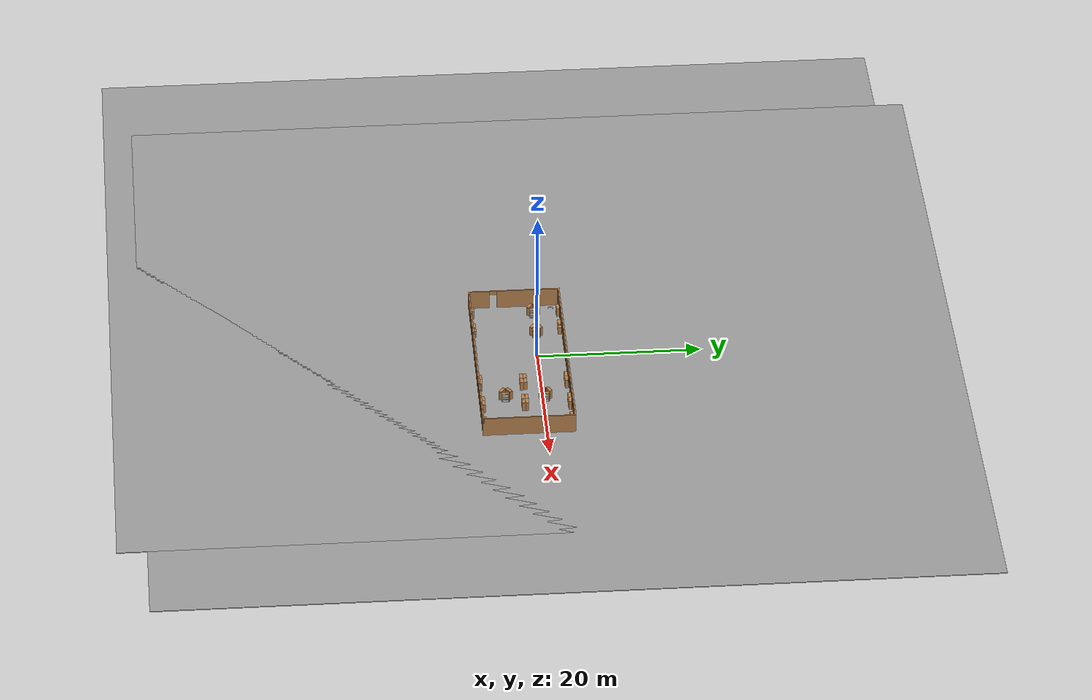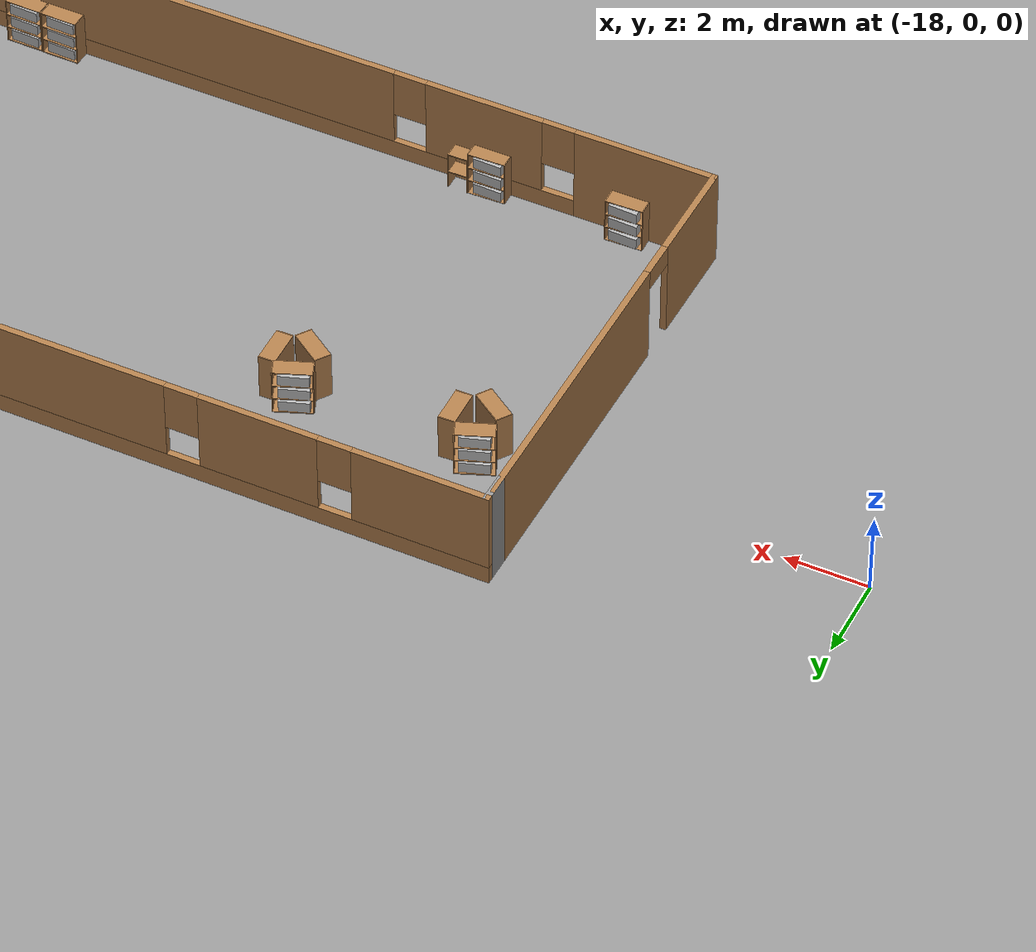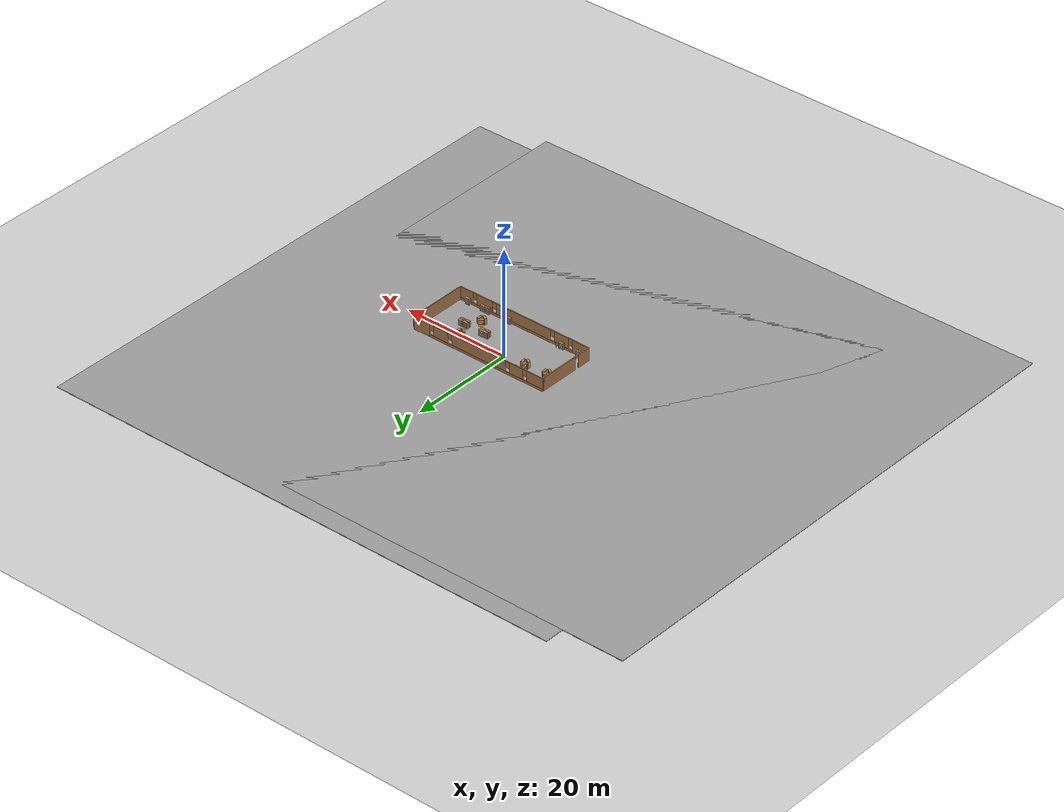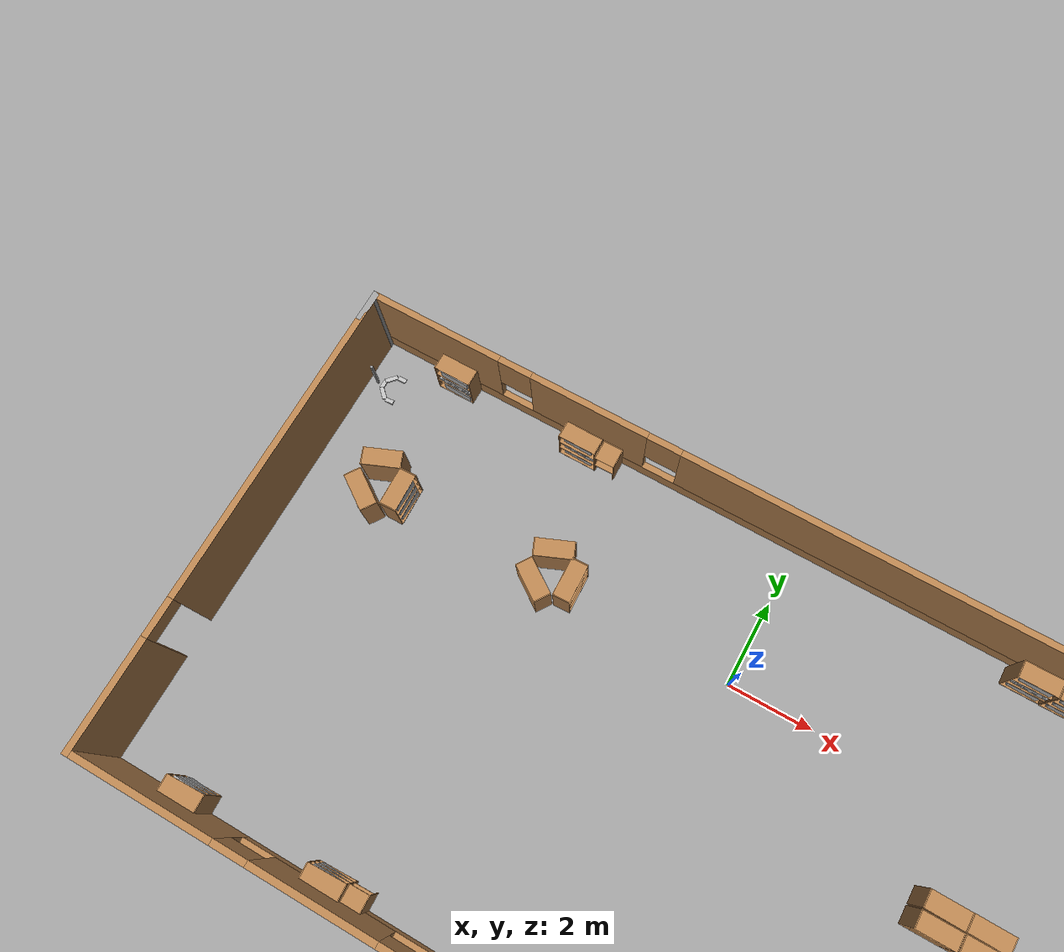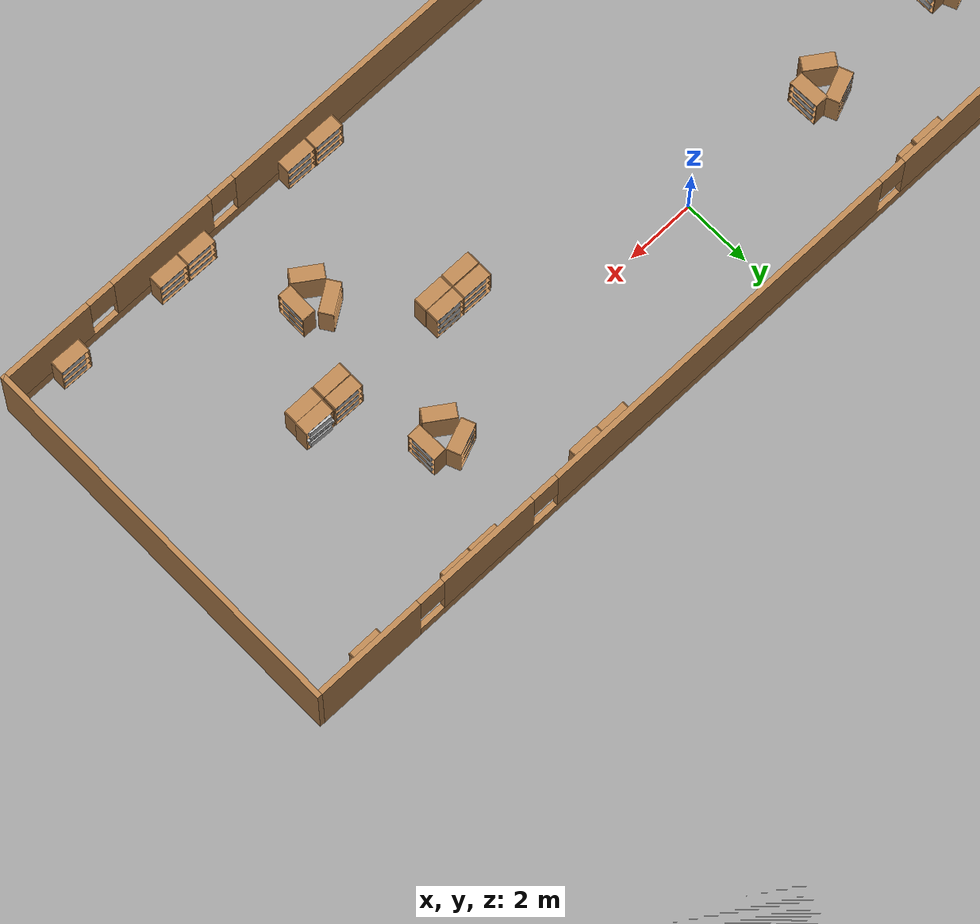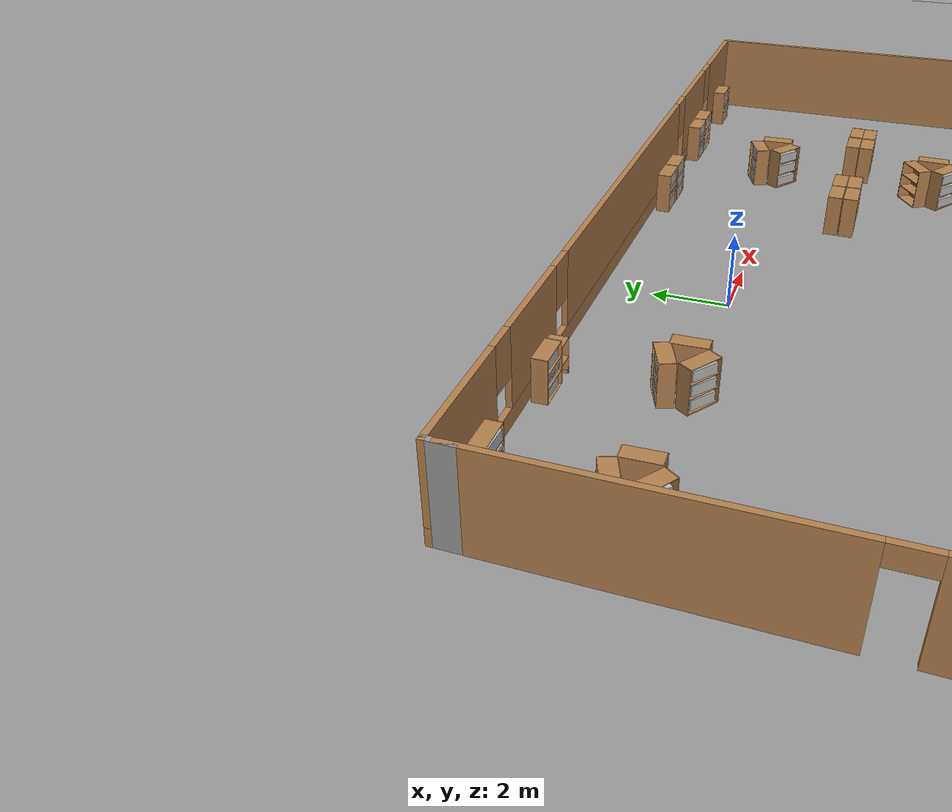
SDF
<sdf version="1.7">
 <world name="default">
  <light name="sun" type="directional">
   <pose>0 0 10 0 -0 0</pose>
   <diffuse>0.8 0.8 0.8 1</diffuse>
   <specular>0.2 0.2 0.2 1</specular>
   <attenuation>
    <range>1000</range>
    <constant>0.9</constant>
    <linear>0.01</linear>
    <quadratic>0.001</quadratic>
   </attenuation>
   <direction>-0.5 0.1 -0.9</direction>
   <spot><inner_angle>0</inner_angle><outer_angle>0</outer_angle><falloff>0</falloff></spot>
  </light>
  <model name="ground_plane">
   <static>1</static>
   <link name="link">
    <collision name="collision">
     <geometry><plane><normal>0 0 1</normal><size>100 100</size></plane></geometry>
     <surface><friction><ode><mu>100</mu><mu2>50</mu2></ode></friction></surface>
    </collision>
    <visual name="visual">
     <cast_shadows>0</cast_shadows>
     <geometry><plane><normal>0 0 1</normal><size>100 100</size></plane></geometry>
     <material>
      <script><uri>file://media/materials/scripts/gazebo.material</uri><name>Gazebo/Grey</name></script>
     </material>
    </visual>
   </link>
  </model>
  <gravity>0 0 -9.8</gravity>
  <magnetic_field>6e-06 2.3e-05 -4.2e-05</magnetic_field>
  <atmosphere type="adiabatic"/>
  <physics type="ode">
   <max_step_size>0.001</max_step_size>
   <real_time_factor>1</real_time_factor>
   <real_time_update_rate>1000</real_time_update_rate>
  </physics>
  <scene><ambient>0.4 0.4 0.4 1</ambient><background>0.7 0.7 0.7 1</background><shadows>1</shadows></scene>
  <spherical_coordinates>
   <surface_model>EARTH_WGS84</surface_model>
   <latitude_deg>0</latitude_deg>
   <longitude_deg>0</longitude_deg>
   <elevation>0</elevation>
   <heading_deg>0</heading_deg>
  </spherical_coordinates>
  <model name="Library">
   <pose>2.5811 -2.1364 0 0 -0 0</pose>
   <link name="Wall_0">
    <pose>-13.3 -0.125 0 0 -0 -1.5708</pose>
    <visual name="Wall_0_Visual_0">
     <pose>-1.74308 0 1.25 0 -0 0</pose>
     <geometry><box><size>7.51384 0.15 2.5</size></box></geometry>
     <material>
      <script><uri>file://media/materials/scripts/gazebo.material</uri><name>Gazebo/Wood</name></script>
      <ambient>1 1 1 1</ambient>
     </material>
     <meta><layer>0</layer></meta>
    </visual>
    <collision name="Wall_0_Collision_0">
     <geometry><box><size>7.51384 0.15 2.5</size></box></geometry>
     <pose>-1.74308 0 1.25 0 -0 0</pose>
    </collision>
    <visual name="Wall_0_Visual_1">
     <pose>4.20692 0 1.25 0 -0 0</pose>
     <geometry><box><size>2.58616 0.15 2.5</size></box></geometry>
     <material>
      <script><uri>file://media/materials/scripts/gazebo.material</uri><name>Gazebo/Wood</name></script>
      <ambient>1 1 1 1</ambient>
     </material>
     <meta><layer>0</layer></meta>
    </visual>
    <collision name="Wall_0_Collision_1">
     <geometry><box><size>2.58616 0.15 2.5</size></box></geometry>
     <pose>4.20692 0 1.25 0 -0 0</pose>
    </collision>
    <visual name="Wall_0_Visual_2">
     <pose>2.46384 0 2.25 0 -0 0</pose>
     <geometry><box><size>0.9 0.15 0.5</size></box></geometry>
     <material>
      <script><uri>file://media/materials/scripts/gazebo.material</uri><name>Gazebo/Wood</name></script>
      <ambient>1 1 1 1</ambient>
     </material>
     <meta><layer>0</layer></meta>
    </visual>
    <collision name="Wall_0_Collision_2">
     <geometry><box><size>0.9 0.15 0.5</size></box></geometry>
     <pose>2.46384 0 2.25 0 -0 0</pose>
    </collision>
   </link>
   <link name="Wall_1">
    <pose>0 -5.55 0 0 -0 0</pose>
    <visual name="Wall_1_Visual_0">
     <pose>-11.6563 0 1.25 0 -0 0</pose>
     <geometry><box><size>3.43737 0.15 2.5</size></box></geometry>
     <material>
      <script><uri>file://media/materials/scripts/gazebo.material</uri><name>Gazebo/Wood</name></script>
      <ambient>1 1 1 1</ambient>
     </material>
     <meta><layer>0</layer></meta>
    </visual>
    <collision name="Wall_1_Collision_0">
     <geometry><box><size>3.43737 0.15 2.5</size></box></geometry>
     <pose>-11.6563 0 1.25 0 -0 0</pose>
    </collision>
    <visual name="Wall_1_Visual_1">
     <pose>1.71868 0 0.25 0 -0 0</pose>
     <geometry><box><size>23.3126 0.15 0.5</size></box></geometry>
     <material>
      <script><uri>file://media/materials/scripts/gazebo.material</uri><name>Gazebo/Wood</name></script>
      <ambient>1 1 1 1</ambient>
     </material>
     <meta><layer>0</layer></meta>
    </visual>
    <collision name="Wall_1_Collision_1">
     <geometry><box><size>23.3126 0.15 0.5</size></box></geometry>
     <pose>1.71868 0 0.25 0 -0 0</pose>
    </collision>
    <visual name="Wall_1_Visual_2">
     <pose>-7.6969 0 1.5 0 -0 0</pose>
     <geometry><box><size>2.88146 0.15 2</size></box></geometry>
     <material>
      <script><uri>file://media/materials/scripts/gazebo.material</uri><name>Gazebo/Wood</name></script>
      <ambient>1 1 1 1</ambient>
     </material>
     <meta><layer>0</layer></meta>
    </visual>
    <collision name="Wall_1_Collision_2">
     <geometry><box><size>2.88146 0.15 2</size></box></geometry>
     <pose>-7.6969 0 1.5 0 -0 0</pose>
    </collision>
    <visual name="Wall_1_Visual_3">
     <pose>0.131252 0 1.5 0 -0 0</pose>
     <geometry><box><size>11.1749 0.15 2</size></box></geometry>
     <material>
      <script><uri>file://media/materials/scripts/gazebo.material</uri><name>Gazebo/Wood</name></script>
      <ambient>1 1 1 1</ambient>
     </material>
     <meta><layer>0</layer></meta>
    </visual>
    <collision name="Wall_1_Collision_3">
     <geometry><box><size>11.1749 0.15 2</size></box></geometry>
     <pose>0.131252 0 1.5 0 -0 0</pose>
    </collision>
    <visual name="Wall_1_Visual_4">
     <pose>8.14146 0 1.5 0 -0 0</pose>
     <geometry><box><size>3.24556 0.15 2</size></box></geometry>
     <material>
      <script><uri>file://media/materials/scripts/gazebo.material</uri><name>Gazebo/Wood</name></script>
      <ambient>1 1 1 1</ambient>
     </material>
     <meta><layer>0</layer></meta>
    </visual>
    <collision name="Wall_1_Collision_4">
     <geometry><box><size>3.24556 0.15 2</size></box></geometry>
     <pose>8.14146 0 1.5 0 -0 0</pose>
    </collision>
    <visual name="Wall_1_Visual_5">
     <pose>11.9696 0 1.5 0 -0 0</pose>
     <geometry><box><size>2.81076 0.15 2</size></box></geometry>
     <material>
      <script><uri>file://media/materials/scripts/gazebo.material</uri><name>Gazebo/Wood</name></script>
      <ambient>1 1 1 1</ambient>
     </material>
     <meta><layer>0</layer></meta>
    </visual>
    <collision name="Wall_1_Collision_5">
     <geometry><box><size>2.81076 0.15 2</size></box></geometry>
     <pose>11.9696 0 1.5 0 -0 0</pose>
    </collision>
    <visual name="Wall_1_Visual_6">
     <pose>-9.53763 0 1.9 0 -0 0</pose>
     <geometry><box><size>0.8 0.15 1.2</size></box></geometry>
     <material>
      <script><uri>file://media/materials/scripts/gazebo.material</uri><name>Gazebo/Wood</name></script>
      <ambient>1 1 1 1</ambient>
     </material>
     <meta><layer>0</layer></meta>
    </visual>
    <collision name="Wall_1_Collision_6">
     <geometry><box><size>0.8 0.15 1.2</size></box></geometry>
     <pose>-9.53763 0 1.9 0 -0 0</pose>
    </collision>
    <visual name="Wall_1_Visual_7">
     <pose>-5.85617 0 1.9 0 -0 0</pose>
     <geometry><box><size>0.8 0.15 1.2</size></box></geometry>
     <material>
      <script><uri>file://media/materials/scripts/gazebo.material</uri><name>Gazebo/Wood</name></script>
      <ambient>1 1 1 1</ambient>
     </material>
     <meta><layer>0</layer></meta>
    </visual>
    <collision name="Wall_1_Collision_7">
     <geometry><box><size>0.8 0.15 1.2</size></box></geometry>
     <pose>-5.85617 0 1.9 0 -0 0</pose>
    </collision>
    <visual name="Wall_1_Visual_8">
     <pose>6.11868 0 1.9 0 -0 0</pose>
     <geometry><box><size>0.8 0.15 1.2</size></box></geometry>
     <material>
      <script><uri>file://media/materials/scripts/gazebo.material</uri><name>Gazebo/Wood</name></script>
      <ambient>1 1 1 1</ambient>
     </material>
     <meta><layer>0</layer></meta>
    </visual>
    <collision name="Wall_1_Collision_8">
     <geometry><box><size>0.8 0.15 1.2</size></box></geometry>
     <pose>6.11868 0 1.9 0 -0 0</pose>
    </collision>
    <visual name="Wall_1_Visual_9">
     <pose>10.1642 0 1.9 0 -0 0</pose>
     <geometry><box><size>0.8 0.15 1.2</size></box></geometry>
     <material>
      <script><uri>file://media/materials/scripts/gazebo.material</uri><name>Gazebo/Wood</name></script>
      <ambient>1 1 1 1</ambient>
     </material>
     <meta><layer>0</layer></meta>
    </visual>
    <collision name="Wall_1_Collision_9">
     <geometry><box><size>0.8 0.15 1.2</size></box></geometry>
     <pose>10.1642 0 1.9 0 -0 0</pose>
    </collision>
   </link>
   <link name="Wall_2">
    <collision name="Wall_2_Collision">
     <geometry><box><size>11.25 0.15 2.5</size></box></geometry>
     <pose>0 0 1.25 0 -0 0</pose>
    </collision>
    <visual name="Wall_2_Visual">
     <pose>0 0 1.25 0 -0 0</pose>
     <geometry><box><size>11.25 0.15 2.5</size></box></geometry>
     <material>
      <script><uri>file://media/materials/scripts/gazebo.material</uri><name>Gazebo/Wood</name></script>
      <ambient>1 1 1 1</ambient>
     </material>
     <meta><layer>0</layer></meta>
    </visual>
    <pose>13.3 -0 0 0 -0 1.5708</pose>
   </link>
   <link name="Wall_3">
    <pose>0 5.55 0 0 -0 3.14159</pose>
    <visual name="Wall_3_Visual_0">
     <pose>-11.6864 0 1.25 0 -0 0</pose>
     <geometry><box><size>3.37714 0.15 2.5</size></box></geometry>
     <material>
      <script><uri>file://media/materials/scripts/gazebo.material</uri><name>Gazebo/Wood</name></script>
      <ambient>1 1 1 1</ambient>
     </material>
     <meta><layer>0</layer></meta>
    </visual>
    <collision name="Wall_3_Collision_0">
     <geometry><box><size>3.37714 0.15 2.5</size></box></geometry>
     <pose>-11.6864 0 1.25 0 -0 0</pose>
    </collision>
    <visual name="Wall_3_Visual_1">
     <pose>1.68857 0 0.25 0 -0 0</pose>
     <geometry><box><size>23.3729 0.15 0.5</size></box></geometry>
     <material>
      <script><uri>file://media/materials/scripts/gazebo.material</uri><name>Gazebo/Wood</name></script>
      <ambient>1 1 1 1</ambient>
     </material>
     <meta><layer>0</layer></meta>
    </visual>
    <collision name="Wall_3_Collision_1">
     <geometry><box><size>23.3729 0.15 0.5</size></box></geometry>
     <pose>1.68857 0 0.25 0 -0 0</pose>
    </collision>
    <visual name="Wall_3_Visual_2">
     <pose>-7.69644 0 1.5 0 -0 0</pose>
     <geometry><box><size>3.00282 0.15 2</size></box></geometry>
     <material>
      <script><uri>file://media/materials/scripts/gazebo.material</uri><name>Gazebo/Wood</name></script>
      <ambient>1 1 1 1</ambient>
     </material>
     <meta><layer>0</layer></meta>
    </visual>
    <collision name="Wall_3_Collision_2">
     <geometry><box><size>3.00282 0.15 2</size></box></geometry>
     <pose>-7.69644 0 1.5 0 -0 0</pose>
    </collision>
    <visual name="Wall_3_Visual_3">
     <pose>0.151937 0 1.5 0 -0 0</pose>
     <geometry><box><size>11.0939 0.15 2</size></box></geometry>
     <material>
      <script><uri>file://media/materials/scripts/gazebo.material</uri><name>Gazebo/Wood</name></script>
      <ambient>1 1 1 1</ambient>
     </material>
     <meta><layer>0</layer></meta>
    </visual>
    <collision name="Wall_3_Collision_3">
     <geometry><box><size>11.0939 0.15 2</size></box></geometry>
     <pose>0.151937 0 1.5 0 -0 0</pose>
    </collision>
    <visual name="Wall_3_Visual_4">
     <pose>7.91941 0 1.5 0 -0 0</pose>
     <geometry><box><size>2.841 0.15 2</size></box></geometry>
     <material>
      <script><uri>file://media/materials/scripts/gazebo.material</uri><name>Gazebo/Wood</name></script>
      <ambient>1 1 1 1</ambient>
     </material>
     <meta><layer>0</layer></meta>
    </visual>
    <collision name="Wall_3_Collision_4">
     <geometry><box><size>2.841 0.15 2</size></box></geometry>
     <pose>7.91941 0 1.5 0 -0 0</pose>
    </collision>
    <visual name="Wall_3_Visual_5">
     <pose>11.7575 0 1.5 0 -0 0</pose>
     <geometry><box><size>3.23509 0.15 2</size></box></geometry>
     <material>
      <script><uri>file://media/materials/scripts/gazebo.material</uri><name>Gazebo/Wood</name></script>
      <ambient>1 1 1 1</ambient>
     </material>
     <meta><layer>0</layer></meta>
    </visual>
    <collision name="Wall_3_Collision_5">
     <geometry><box><size>3.23509 0.15 2</size></box></geometry>
     <pose>11.7575 0 1.5 0 -0 0</pose>
    </collision>
    <visual name="Wall_3_Visual_6">
     <pose>-9.59786 0 1.9 0 -0 0</pose>
     <geometry><box><size>0.8 0.15 1.2</size></box></geometry>
     <material>
      <script><uri>file://media/materials/scripts/gazebo.material</uri><name>Gazebo/Wood</name></script>
      <ambient>1 1 1 1</ambient>
     </material>
     <meta><layer>0</layer></meta>
    </visual>
    <collision name="Wall_3_Collision_6">
     <geometry><box><size>0.8 0.15 1.2</size></box></geometry>
     <pose>-9.59786 0 1.9 0 -0 0</pose>
    </collision>
    <visual name="Wall_3_Visual_7">
     <pose>-5.79503 0 1.9 0 -0 0</pose>
     <geometry><box><size>0.8 0.15 1.2</size></box></geometry>
     <material>
      <script><uri>file://media/materials/scripts/gazebo.material</uri><name>Gazebo/Wood</name></script>
      <ambient>1 1 1 1</ambient>
     </material>
     <meta><layer>0</layer></meta>
    </visual>
    <collision name="Wall_3_Collision_7">
     <geometry><box><size>0.8 0.15 1.2</size></box></geometry>
     <pose>-5.79503 0 1.9 0 -0 0</pose>
    </collision>
    <visual name="Wall_3_Visual_8">
     <pose>6.09891 0 1.9 0 -0 0</pose>
     <geometry><box><size>0.8 0.15 1.2</size></box></geometry>
     <material>
      <script><uri>file://media/materials/scripts/gazebo.material</uri><name>Gazebo/Wood</name></script>
      <ambient>1 1 1 1</ambient>
     </material>
     <meta><layer>0</layer></meta>
    </visual>
    <collision name="Wall_3_Collision_8">
     <geometry><box><size>0.8 0.15 1.2</size></box></geometry>
     <pose>6.09891 0 1.9 0 -0 0</pose>
    </collision>
    <visual name="Wall_3_Visual_9">
     <pose>9.73991 0 1.9 0 -0 0</pose>
     <geometry><box><size>0.8 0.15 1.2</size></box></geometry>
     <material>
      <script><uri>file://media/materials/scripts/gazebo.material</uri><name>Gazebo/Wood</name></script>
      <ambient>1 1 1 1</ambient>
     </material>
     <meta><layer>0</layer></meta>
    </visual>
    <collision name="Wall_3_Collision_9">
     <geometry><box><size>0.8 0.15 1.2</size></box></geometry>
     <pose>9.73991 0 1.9 0 -0 0</pose>
    </collision>
   </link>
   <link name="Wall_4">
    <collision name="Wall_4_Collision">
     <geometry><box><size>0.75 0.15 2.5</size></box></geometry>
     <pose>0 0 1.25 0 -0 0</pose>
    </collision>
    <visual name="Wall_4_Visual">
     <pose>0 0 1.25 0 -0 0</pose>
     <geometry><box><size>0.75 0.15 2.5</size></box></geometry>
     <material>
      <script><uri>file://media/materials/scripts/gazebo.material</uri><name>Gazebo/Grey</name></script>
      <ambient>1 1 1 1</ambient>
     </material>
     <meta><layer>0</layer></meta>
    </visual>
    <pose>-13.3 5.25 0 0 -0 -1.5708</pose>
   </link>
   <static>1</static>
  </model>
  <model name="bookshelf">
   <static>1</static>
   <link name="link">
    <inertial><mass>1</mass></inertial>
    <collision name="back">
     <pose>0 0.005 0.6 0 -0 0</pose>
     <geometry><box><size>0.9 0.01 1.2</size></box></geometry>
    </collision>
    <visual name="visual1">
     <pose>0 0.005 0.6 0 -0 0</pose>
     <geometry><box><size>0.9 0.01 1.2</size></box></geometry>
     <material>
      <script><uri>file://media/materials/scripts/gazebo.material</uri><name>Gazebo/Wood</name></script>
     </material>
    </visual>
    <collision name="left_side">
     <pose>0.45 -0.195 0.6 0 -0 0</pose>
     <geometry><box><size>0.02 0.4 1.2</size></box></geometry>
    </collision>
    <visual name="visual2">
     <pose>0.45 -0.195 0.6 0 -0 0</pose>
     <geometry><box><size>0.02 0.4 1.2</size></box></geometry>
     <material>
      <script><uri>file://media/materials/scripts/gazebo.material</uri><name>Gazebo/Wood</name></script>
     </material>
    </visual>
    <collision name="right_side">
     <pose>-0.45 -0.195 0.6 0 -0 0</pose>
     <geometry><box><size>0.02 0.4 1.2</size></box></geometry>
    </collision>
    <visual name="visual3">
     <pose>-0.45 -0.195 0.6 0 -0 0</pose>
     <geometry><box><size>0.02 0.4 1.2</size></box></geometry>
     <material>
      <script><uri>file://media/materials/scripts/gazebo.material</uri><name>Gazebo/Wood</name></script>
     </material>
    </visual>
    <collision name="bottom">
     <pose>0 -0.195 0.03 0 -0 0</pose>
     <geometry><box><size>0.88 0.4 0.06</size></box></geometry>
    </collision>
    <visual name="visual4">
     <pose>0 -0.195 0.03 0 -0 0</pose>
     <geometry><box><size>0.88 0.4 0.06</size></box></geometry>
     <material>
      <script><uri>file://media/materials/scripts/gazebo.material</uri><name>Gazebo/Wood</name></script>
     </material>
    </visual>
    <collision name="top">
     <pose>0 -0.195 1.19 0 -0 0</pose>
     <geometry><box><size>0.88 0.4 0.02</size></box></geometry>
    </collision>
    <visual name="visual5">
     <pose>0 -0.195 1.19 0 -0 0</pose>
     <geometry><box><size>0.88 0.4 0.02</size></box></geometry>
     <material>
      <script><uri>file://media/materials/scripts/gazebo.material</uri><name>Gazebo/Wood</name></script>
     </material>
    </visual>
    <collision name="low_shelf">
     <pose>0 -0.195 0.43 0 -0 0</pose>
     <geometry><box><size>0.88 0.4 0.02</size></box></geometry>
    </collision>
    <visual name="visual6">
     <pose>0 -0.195 0.43 0 -0 0</pose>
     <geometry><box><size>0.88 0.4 0.02</size></box></geometry>
     <material>
      <script><uri>file://media/materials/scripts/gazebo.material</uri><name>Gazebo/Wood</name></script>
     </material>
    </visual>
    <collision name="high_shelf">
     <pose>0 -0.195 0.8 0 -0 0</pose>
     <geometry><box><size>0.88 0.4 0.02</size></box></geometry>
    </collision>
    <visual name="visual7">
     <pose>0 -0.195 0.8 0 -0 0</pose>
     <geometry><box><size>0.88 0.4 0.02</size></box></geometry>
     <material>
      <script><uri>file://media/materials/scripts/gazebo.material</uri><name>Gazebo/Wood</name></script>
     </material>
    </visual>
   </link>
   <pose>6.50028 3.23644 0.012624 0 -0 0</pose>
  </model>
  <model name="bookshelf_clone">
   <static>1</static>
   <link name="link">
    <inertial><mass>1</mass></inertial>
    <collision name="back">
     <pose>0 0.005 0.6 0 -0 0</pose>
     <geometry><box><size>0.9 0.01 1.2</size></box></geometry>
    </collision>
    <visual name="visual1">
     <pose>0 0.005 0.6 0 -0 0</pose>
     <geometry><box><size>0.9 0.01 1.2</size></box></geometry>
     <material>
      <script><uri>file://media/materials/scripts/gazebo.material</uri><name>Gazebo/Wood</name></script>
     </material>
    </visual>
    <collision name="left_side">
     <pose>0.45 -0.195 0.6 0 -0 0</pose>
     <geometry><box><size>0.02 0.4 1.2</size></box></geometry>
    </collision>
    <visual name="visual2">
     <pose>0.45 -0.195 0.6 0 -0 0</pose>
     <geometry><box><size>0.02 0.4 1.2</size></box></geometry>
     <material>
      <script><uri>file://media/materials/scripts/gazebo.material</uri><name>Gazebo/Wood</name></script>
     </material>
    </visual>
    <collision name="right_side">
     <pose>-0.45 -0.195 0.6 0 -0 0</pose>
     <geometry><box><size>0.02 0.4 1.2</size></box></geometry>
    </collision>
    <visual name="visual3">
     <pose>-0.45 -0.195 0.6 0 -0 0</pose>
     <geometry><box><size>0.02 0.4 1.2</size></box></geometry>
     <material>
      <script><uri>file://media/materials/scripts/gazebo.material</uri><name>Gazebo/Wood</name></script>
     </material>
    </visual>
    <collision name="bottom">
     <pose>0 -0.195 0.03 0 -0 0</pose>
     <geometry><box><size>0.88 0.4 0.06</size></box></geometry>
    </collision>
    <visual name="visual4">
     <pose>0 -0.195 0.03 0 -0 0</pose>
     <geometry><box><size>0.88 0.4 0.06</size></box></geometry>
     <material>
      <script><uri>file://media/materials/scripts/gazebo.material</uri><name>Gazebo/Wood</name></script>
     </material>
    </visual>
    <collision name="top">
     <pose>0 -0.195 1.19 0 -0 0</pose>
     <geometry><box><size>0.88 0.4 0.02</size></box></geometry>
    </collision>
    <visual name="visual5">
     <pose>0 -0.195 1.19 0 -0 0</pose>
     <geometry><box><size>0.88 0.4 0.02</size></box></geometry>
     <material>
      <script><uri>file://media/materials/scripts/gazebo.material</uri><name>Gazebo/Wood</name></script>
     </material>
    </visual>
    <collision name="low_shelf">
     <pose>0 -0.195 0.43 0 -0 0</pose>
     <geometry><box><size>0.88 0.4 0.02</size></box></geometry>
    </collision>
    <visual name="visual6">
     <pose>0 -0.195 0.43 0 -0 0</pose>
     <geometry><box><size>0.88 0.4 0.02</size></box></geometry>
     <material>
      <script><uri>file://media/materials/scripts/gazebo.material</uri><name>Gazebo/Wood</name></script>
     </material>
    </visual>
    <collision name="high_shelf">
     <pose>0 -0.195 0.8 0 -0 0</pose>
     <geometry><box><size>0.88 0.4 0.02</size></box></geometry>
    </collision>
    <visual name="visual7">
     <pose>0 -0.195 0.8 0 -0 0</pose>
     <geometry><box><size>0.88 0.4 0.02</size></box></geometry>
     <material>
      <script><uri>file://media/materials/scripts/gazebo.material</uri><name>Gazebo/Wood</name></script>
     </material>
    </visual>
   </link>
   <pose>5.58313 3.24733 0.012624 0 -0 0</pose>
  </model>
  <model name="ground_plane_0">
   <static>1</static>
   <link name="link">
    <collision name="collision">
     <geometry><plane><normal>0 0 1</normal><size>100 100</size></plane></geometry>
     <surface>
      <contact><collide_bitmask>65535</collide_bitmask></contact>
      <friction><ode><mu>100</mu><mu2>50</mu2></ode></friction>
     </surface>
    </collision>
    <visual name="visual">
     <cast_shadows>0</cast_shadows>
     <geometry><plane><normal>0 0 1</normal><size>100 100</size></plane></geometry>
     <material>
      <script><uri>file://media/materials/scripts/gazebo.material</uri><name>Gazebo/Grey</name></script>
     </material>
    </visual>
   </link>
   <pose>-2.55958 1.44132 0 0 -0 0</pose>
  </model>
  <model name="ground_plane_1">
   <static>1</static>
   <link name="link">
    <collision name="collision">
     <geometry><plane><normal>0 0 1</normal><size>100 100</size></plane></geometry>
     <surface>
      <contact><collide_bitmask>65535</collide_bitmask></contact>
      <friction><ode><mu>100</mu><mu2>50</mu2></ode></friction>
     </surface>
    </collision>
    <visual name="visual">
     <cast_shadows>0</cast_shadows>
     <geometry><plane><normal>0 0 1</normal><size>100 100</size></plane></geometry>
     <material>
      <script><uri>file://media/materials/scripts/gazebo.material</uri><name>Gazebo/Grey</name></script>
     </material>
    </visual>
   </link>
   <pose>-14.0073 -2.16514 0 0 -0 0</pose>
  </model>
  <model name="bookshelf_0">
   <static>1</static>
   <link name="link">
    <inertial><mass>1</mass></inertial>
    <collision name="back">
     <pose>0 0.005 0.6 0 -0 0</pose>
     <geometry><box><size>0.9 0.01 1.2</size></box></geometry>
    </collision>
    <visual name="visual1">
     <pose>0 0.005 0.6 0 -0 0</pose>
     <geometry><box><size>0.9 0.01 1.2</size></box></geometry>
     <material>
      <script><uri>file://media/materials/scripts/gazebo.material</uri><name>Gazebo/Wood</name></script>
     </material>
    </visual>
    <collision name="left_side">
     <pose>0.45 -0.195 0.6 0 -0 0</pose>
     <geometry><box><size>0.02 0.4 1.2</size></box></geometry>
    </collision>
    <visual name="visual2">
     <pose>0.45 -0.195 0.6 0 -0 0</pose>
     <geometry><box><size>0.02 0.4 1.2</size></box></geometry>
     <material>
      <script><uri>file://media/materials/scripts/gazebo.material</uri><name>Gazebo/Wood</name></script>
     </material>
    </visual>
    <collision name="right_side">
     <pose>-0.45 -0.195 0.6 0 -0 0</pose>
     <geometry><box><size>0.02 0.4 1.2</size></box></geometry>
    </collision>
    <visual name="visual3">
     <pose>-0.45 -0.195 0.6 0 -0 0</pose>
     <geometry><box><size>0.02 0.4 1.2</size></box></geometry>
     <material>
      <script><uri>file://media/materials/scripts/gazebo.material</uri><name>Gazebo/Wood</name></script>
     </material>
    </visual>
    <collision name="bottom">
     <pose>0 -0.195 0.03 0 -0 0</pose>
     <geometry><box><size>0.88 0.4 0.06</size></box></geometry>
    </collision>
    <visual name="visual4">
     <pose>0 -0.195 0.03 0 -0 0</pose>
     <geometry><box><size>0.88 0.4 0.06</size></box></geometry>
     <material>
      <script><uri>file://media/materials/scripts/gazebo.material</uri><name>Gazebo/Wood</name></script>
     </material>
    </visual>
    <collision name="top">
     <pose>0 -0.195 1.19 0 -0 0</pose>
     <geometry><box><size>0.88 0.4 0.02</size></box></geometry>
    </collision>
    <visual name="visual5">
     <pose>0 -0.195 1.19 0 -0 0</pose>
     <geometry><box><size>0.88 0.4 0.02</size></box></geometry>
     <material>
      <script><uri>file://media/materials/scripts/gazebo.material</uri><name>Gazebo/Wood</name></script>
     </material>
    </visual>
    <collision name="low_shelf">
     <pose>0 -0.195 0.43 0 -0 0</pose>
     <geometry><box><size>0.88 0.4 0.02</size></box></geometry>
    </collision>
    <visual name="visual6">
     <pose>0 -0.195 0.43 0 -0 0</pose>
     <geometry><box><size>0.88 0.4 0.02</size></box></geometry>
     <material>
      <script><uri>file://media/materials/scripts/gazebo.material</uri><name>Gazebo/Wood</name></script>
     </material>
    </visual>
    <collision name="high_shelf">
     <pose>0 -0.195 0.8 0 -0 0</pose>
     <geometry><box><size>0.88 0.4 0.02</size></box></geometry>
    </collision>
    <visual name="visual7">
     <pose>0 -0.195 0.8 0 -0 0</pose>
     <geometry><box><size>0.88 0.4 0.02</size></box></geometry>
     <material>
      <script><uri>file://media/materials/scripts/gazebo.material</uri><name>Gazebo/Wood</name></script>
     </material>
    </visual>
   </link>
   <pose>-8.64596 3.34342 0 0 -0 0</pose>
  </model>
  <model name="bookshelf_0_clone">
   <static>1</static>
   <link name="link">
    <inertial><mass>1</mass></inertial>
    <collision name="back">
     <pose>0 0.005 0.6 0 -0 0</pose>
     <geometry><box><size>0.9 0.01 1.2</size></box></geometry>
    </collision>
    <visual name="visual1">
     <pose>0 0.005 0.6 0 -0 0</pose>
     <geometry><box><size>0.9 0.01 1.2</size></box></geometry>
     <material>
      <script><uri>file://media/materials/scripts/gazebo.material</uri><name>Gazebo/Wood</name></script>
     </material>
    </visual>
    <collision name="left_side">
     <pose>0.45 -0.195 0.6 0 -0 0</pose>
     <geometry><box><size>0.02 0.4 1.2</size></box></geometry>
    </collision>
    <visual name="visual2">
     <pose>0.45 -0.195 0.6 0 -0 0</pose>
     <geometry><box><size>0.02 0.4 1.2</size></box></geometry>
     <material>
      <script><uri>file://media/materials/scripts/gazebo.material</uri><name>Gazebo/Wood</name></script>
     </material>
    </visual>
    <collision name="right_side">
     <pose>-0.45 -0.195 0.6 0 -0 0</pose>
     <geometry><box><size>0.02 0.4 1.2</size></box></geometry>
    </collision>
    <visual name="visual3">
     <pose>-0.45 -0.195 0.6 0 -0 0</pose>
     <geometry><box><size>0.02 0.4 1.2</size></box></geometry>
     <material>
      <script><uri>file://media/materials/scripts/gazebo.material</uri><name>Gazebo/Wood</name></script>
     </material>
    </visual>
    <collision name="bottom">
     <pose>0 -0.195 0.03 0 -0 0</pose>
     <geometry><box><size>0.88 0.4 0.06</size></box></geometry>
    </collision>
    <visual name="visual4">
     <pose>0 -0.195 0.03 0 -0 0</pose>
     <geometry><box><size>0.88 0.4 0.06</size></box></geometry>
     <material>
      <script><uri>file://media/materials/scripts/gazebo.material</uri><name>Gazebo/Wood</name></script>
     </material>
    </visual>
    <collision name="top">
     <pose>0 -0.195 1.19 0 -0 0</pose>
     <geometry><box><size>0.88 0.4 0.02</size></box></geometry>
    </collision>
    <visual name="visual5">
     <pose>0 -0.195 1.19 0 -0 0</pose>
     <geometry><box><size>0.88 0.4 0.02</size></box></geometry>
     <material>
      <script><uri>file://media/materials/scripts/gazebo.material</uri><name>Gazebo/Wood</name></script>
     </material>
    </visual>
    <collision name="low_shelf">
     <pose>0 -0.195 0.43 0 -0 0</pose>
     <geometry><box><size>0.88 0.4 0.02</size></box></geometry>
    </collision>
    <visual name="visual6">
     <pose>0 -0.195 0.43 0 -0 0</pose>
     <geometry><box><size>0.88 0.4 0.02</size></box></geometry>
     <material>
      <script><uri>file://media/materials/scripts/gazebo.material</uri><name>Gazebo/Wood</name></script>
     </material>
    </visual>
    <collision name="high_shelf">
     <pose>0 -0.195 0.8 0 -0 0</pose>
     <geometry><box><size>0.88 0.4 0.02</size></box></geometry>
    </collision>
    <visual name="visual7">
     <pose>0 -0.195 0.8 0 -0 0</pose>
     <geometry><box><size>0.88 0.4 0.02</size></box></geometry>
     <material>
      <script><uri>file://media/materials/scripts/gazebo.material</uri><name>Gazebo/Wood</name></script>
     </material>
    </visual>
   </link>
   <pose>-5.35741 3.26655 0 0 -0 0</pose>
  </model>
  <model name="cabinet">
   <static>1</static>
   <link name="cabinet_bottom_plate">
    <inertial>
     <pose>0 0 -1 0 -0 0</pose>
     <inertia><ixx>2.05</ixx><ixy>0</ixy><ixz>0</ixz><iyy>2.05</iyy><iyz>0</iyz><izz>2.05</izz></inertia>
     <mass>25</mass>
    </inertial>
    <collision name="cabinet_bottom_plate_geom">
     <pose>0 0 0.01 0 -0 0</pose>
     <geometry><box><size>0.45 0.45 0.02</size></box></geometry>
    </collision>
    <visual name="cabinet_bottom_plate_geom_visual">
     <pose>0 0 0.01 0 -0 0</pose>
     <geometry><box><size>0.45 0.45 0.02</size></box></geometry>
     <material>
      <script><uri>file://media/materials/scripts/gazebo.material</uri><name>Gazebo/Wood</name></script>
     </material>
    </visual>
    <collision name="cabinet_bottom_plate_geom_cabinet_back_plate">
     <pose>0.235 0 0.51 0 -0 0</pose>
     <geometry><box><size>0.02 0.45 1.02</size></box></geometry>
    </collision>
    <visual name="cabinet_bottom_plate_geom_cabinet_back_plate_visual">
     <pose>0.235 0 0.51 0 -0 0</pose>
     <geometry><box><size>0.02 0.45 1.02</size></box></geometry>
     <material>
      <script><uri>file://media/materials/scripts/gazebo.material</uri><name>Gazebo/Wood</name></script>
     </material>
    </visual>
    <collision name="cabinet_bottom_plate_geom_cabinet_left_plate">
     <pose>0 0.235 0.51 0 -0 0</pose>
     <geometry><box><size>0.45 0.02 1.02</size></box></geometry>
    </collision>
    <visual name="cabinet_bottom_plate_geom_cabinet_left_plate_visual">
     <pose>0 0.235 0.51 0 -0 0</pose>
     <geometry><box><size>0.45 0.02 1.02</size></box></geometry>
     <material>
      <script><uri>file://media/materials/scripts/gazebo.material</uri><name>Gazebo/Wood</name></script>
     </material>
    </visual>
    <collision name="cabinet_bottom_plate_geom_cabinet_middle_plate">
     <pose>0 0 0.51 0 -0 0</pose>
     <geometry><box><size>0.45 0.45 0.02</size></box></geometry>
    </collision>
    <visual name="cabinet_bottom_plate_geom_cabinet_middle_plate_visual">
     <pose>0 0 0.51 0 -0 0</pose>
     <geometry><box><size>0.45 0.45 0.02</size></box></geometry>
     <material>
      <script><uri>file://media/materials/scripts/gazebo.material</uri><name>Gazebo/Wood</name></script>
     </material>
    </visual>
    <collision name="cabinet_bottom_plate_geom_cabinet_right_plate">
     <pose>0 -0.235 0.51 0 -0 0</pose>
     <geometry><box><size>0.45 0.02 1.02</size></box></geometry>
    </collision>
    <visual name="cabinet_bottom_plate_geom_cabinet_right_plate_visual">
     <pose>0 -0.235 0.51 0 -0 0</pose>
     <geometry><box><size>0.45 0.02 1.02</size></box></geometry>
     <material>
      <script><uri>file://media/materials/scripts/gazebo.material</uri><name>Gazebo/Wood</name></script>
     </material>
    </visual>
    <collision name="cabinet_bottom_plate_geom_cabinet_top_plate">
     <pose>0 0 1.01 0 -0 0</pose>
     <geometry><box><size>0.45 0.45 0.02</size></box></geometry>
    </collision>
    <visual name="cabinet_bottom_plate_geom_cabinet_top_plate_visual">
     <pose>0 0 1.01 0 -0 0</pose>
     <geometry><box><size>0.45 0.45 0.02</size></box></geometry>
     <material>
      <script><uri>file://media/materials/scripts/gazebo.material</uri><name>Gazebo/Wood</name></script>
     </material>
    </visual>
   </link>
   <pose>-4.65296 3.08486 0 0 -0 1.58529</pose>
  </model>
  <model name="bookshelf_0_clone_0">
   <static>1</static>
   <link name="link">
    <inertial><mass>1</mass></inertial>
    <collision name="back">
     <pose>0 0.005 0.6 0 -0 0</pose>
     <geometry><box><size>0.9 0.01 1.2</size></box></geometry>
    </collision>
    <visual name="visual1">
     <pose>0 0.005 0.6 0 -0 0</pose>
     <geometry><box><size>0.9 0.01 1.2</size></box></geometry>
     <material>
      <script><uri>file://media/materials/scripts/gazebo.material</uri><name>Gazebo/Wood</name></script>
     </material>
    </visual>
    <collision name="left_side">
     <pose>0.45 -0.195 0.6 0 -0 0</pose>
     <geometry><box><size>0.02 0.4 1.2</size></box></geometry>
    </collision>
    <visual name="visual2">
     <pose>0.45 -0.195 0.6 0 -0 0</pose>
     <geometry><box><size>0.02 0.4 1.2</size></box></geometry>
     <material>
      <script><uri>file://media/materials/scripts/gazebo.material</uri><name>Gazebo/Wood</name></script>
     </material>
    </visual>
    <collision name="right_side">
     <pose>-0.45 -0.195 0.6 0 -0 0</pose>
     <geometry><box><size>0.02 0.4 1.2</size></box></geometry>
    </collision>
    <visual name="visual3">
     <pose>-0.45 -0.195 0.6 0 -0 0</pose>
     <geometry><box><size>0.02 0.4 1.2</size></box></geometry>
     <material>
      <script><uri>file://media/materials/scripts/gazebo.material</uri><name>Gazebo/Wood</name></script>
     </material>
    </visual>
    <collision name="bottom">
     <pose>0 -0.195 0.03 0 -0 0</pose>
     <geometry><box><size>0.88 0.4 0.06</size></box></geometry>
    </collision>
    <visual name="visual4">
     <pose>0 -0.195 0.03 0 -0 0</pose>
     <geometry><box><size>0.88 0.4 0.06</size></box></geometry>
     <material>
      <script><uri>file://media/materials/scripts/gazebo.material</uri><name>Gazebo/Wood</name></script>
     </material>
    </visual>
    <collision name="top">
     <pose>0 -0.195 1.19 0 -0 0</pose>
     <geometry><box><size>0.88 0.4 0.02</size></box></geometry>
    </collision>
    <visual name="visual5">
     <pose>0 -0.195 1.19 0 -0 0</pose>
     <geometry><box><size>0.88 0.4 0.02</size></box></geometry>
     <material>
      <script><uri>file://media/materials/scripts/gazebo.material</uri><name>Gazebo/Wood</name></script>
     </material>
    </visual>
    <collision name="low_shelf">
     <pose>0 -0.195 0.43 0 -0 0</pose>
     <geometry><box><size>0.88 0.4 0.02</size></box></geometry>
    </collision>
    <visual name="visual6">
     <pose>0 -0.195 0.43 0 -0 0</pose>
     <geometry><box><size>0.88 0.4 0.02</size></box></geometry>
     <material>
      <script><uri>file://media/materials/scripts/gazebo.material</uri><name>Gazebo/Wood</name></script>
     </material>
    </visual>
    <collision name="high_shelf">
     <pose>0 -0.195 0.8 0 -0 0</pose>
     <geometry><box><size>0.88 0.4 0.02</size></box></geometry>
    </collision>
    <visual name="visual7">
     <pose>0 -0.195 0.8 0 -0 0</pose>
     <geometry><box><size>0.88 0.4 0.02</size></box></geometry>
     <material>
      <script><uri>file://media/materials/scripts/gazebo.material</uri><name>Gazebo/Wood</name></script>
     </material>
    </visual>
   </link>
   <pose>-8.75541 -7.62626 0 0 0 -3.10983</pose>
  </model>
  <model name="bookshelf_0_clone_0_clone">
   <static>1</static>
   <link name="link">
    <inertial><mass>1</mass></inertial>
    <collision name="back">
     <pose>0 0.005 0.6 0 -0 0</pose>
     <geometry><box><size>0.9 0.01 1.2</size></box></geometry>
    </collision>
    <visual name="visual1">
     <pose>0 0.005 0.6 0 -0 0</pose>
     <geometry><box><size>0.9 0.01 1.2</size></box></geometry>
     <material>
      <script><uri>file://media/materials/scripts/gazebo.material</uri><name>Gazebo/Wood</name></script>
     </material>
    </visual>
    <collision name="left_side">
     <pose>0.45 -0.195 0.6 0 -0 0</pose>
     <geometry><box><size>0.02 0.4 1.2</size></box></geometry>
    </collision>
    <visual name="visual2">
     <pose>0.45 -0.195 0.6 0 -0 0</pose>
     <geometry><box><size>0.02 0.4 1.2</size></box></geometry>
     <material>
      <script><uri>file://media/materials/scripts/gazebo.material</uri><name>Gazebo/Wood</name></script>
     </material>
    </visual>
    <collision name="right_side">
     <pose>-0.45 -0.195 0.6 0 -0 0</pose>
     <geometry><box><size>0.02 0.4 1.2</size></box></geometry>
    </collision>
    <visual name="visual3">
     <pose>-0.45 -0.195 0.6 0 -0 0</pose>
     <geometry><box><size>0.02 0.4 1.2</size></box></geometry>
     <material>
      <script><uri>file://media/materials/scripts/gazebo.material</uri><name>Gazebo/Wood</name></script>
     </material>
    </visual>
    <collision name="bottom">
     <pose>0 -0.195 0.03 0 -0 0</pose>
     <geometry><box><size>0.88 0.4 0.06</size></box></geometry>
    </collision>
    <visual name="visual4">
     <pose>0 -0.195 0.03 0 -0 0</pose>
     <geometry><box><size>0.88 0.4 0.06</size></box></geometry>
     <material>
      <script><uri>file://media/materials/scripts/gazebo.material</uri><name>Gazebo/Wood</name></script>
     </material>
    </visual>
    <collision name="top">
     <pose>0 -0.195 1.19 0 -0 0</pose>
     <geometry><box><size>0.88 0.4 0.02</size></box></geometry>
    </collision>
    <visual name="visual5">
     <pose>0 -0.195 1.19 0 -0 0</pose>
     <geometry><box><size>0.88 0.4 0.02</size></box></geometry>
     <material>
      <script><uri>file://media/materials/scripts/gazebo.material</uri><name>Gazebo/Wood</name></script>
     </material>
    </visual>
    <collision name="low_shelf">
     <pose>0 -0.195 0.43 0 -0 0</pose>
     <geometry><box><size>0.88 0.4 0.02</size></box></geometry>
    </collision>
    <visual name="visual6">
     <pose>0 -0.195 0.43 0 -0 0</pose>
     <geometry><box><size>0.88 0.4 0.02</size></box></geometry>
     <material>
      <script><uri>file://media/materials/scripts/gazebo.material</uri><name>Gazebo/Wood</name></script>
     </material>
    </visual>
    <collision name="high_shelf">
     <pose>0 -0.195 0.8 0 -0 0</pose>
     <geometry><box><size>0.88 0.4 0.02</size></box></geometry>
    </collision>
    <visual name="visual7">
     <pose>0 -0.195 0.8 0 -0 0</pose>
     <geometry><box><size>0.88 0.4 0.02</size></box></geometry>
     <material>
      <script><uri>file://media/materials/scripts/gazebo.material</uri><name>Gazebo/Wood</name></script>
     </material>
    </visual>
   </link>
   <pose>-5.34307 -7.65405 0 0 0 -3.10983</pose>
  </model>
  <model name="cabinet_clone">
   <static>1</static>
   <link name="cabinet_bottom_plate">
    <inertial>
     <pose>0 0 -1 0 -0 0</pose>
     <inertia><ixx>2.05</ixx><ixy>0</ixy><ixz>0</ixz><iyy>2.05</iyy><iyz>0</iyz><izz>2.05</izz></inertia>
     <mass>25</mass>
    </inertial>
    <collision name="cabinet_bottom_plate_geom">
     <pose>0 0 0.01 0 -0 0</pose>
     <geometry><box><size>0.45 0.45 0.02</size></box></geometry>
    </collision>
    <visual name="cabinet_bottom_plate_geom_visual">
     <pose>0 0 0.01 0 -0 0</pose>
     <geometry><box><size>0.45 0.45 0.02</size></box></geometry>
     <material>
      <script><uri>file://media/materials/scripts/gazebo.material</uri><name>Gazebo/Wood</name></script>
     </material>
    </visual>
    <collision name="cabinet_bottom_plate_geom_cabinet_back_plate">
     <pose>0.235 0 0.51 0 -0 0</pose>
     <geometry><box><size>0.02 0.45 1.02</size></box></geometry>
    </collision>
    <visual name="cabinet_bottom_plate_geom_cabinet_back_plate_visual">
     <pose>0.235 0 0.51 0 -0 0</pose>
     <geometry><box><size>0.02 0.45 1.02</size></box></geometry>
     <material>
      <script><uri>file://media/materials/scripts/gazebo.material</uri><name>Gazebo/Wood</name></script>
     </material>
    </visual>
    <collision name="cabinet_bottom_plate_geom_cabinet_left_plate">
     <pose>0 0.235 0.51 0 -0 0</pose>
     <geometry><box><size>0.45 0.02 1.02</size></box></geometry>
    </collision>
    <visual name="cabinet_bottom_plate_geom_cabinet_left_plate_visual">
     <pose>0 0.235 0.51 0 -0 0</pose>
     <geometry><box><size>0.45 0.02 1.02</size></box></geometry>
     <material>
      <script><uri>file://media/materials/scripts/gazebo.material</uri><name>Gazebo/Wood</name></script>
     </material>
    </visual>
    <collision name="cabinet_bottom_plate_geom_cabinet_middle_plate">
     <pose>0 0 0.51 0 -0 0</pose>
     <geometry><box><size>0.45 0.45 0.02</size></box></geometry>
    </collision>
    <visual name="cabinet_bottom_plate_geom_cabinet_middle_plate_visual">
     <pose>0 0 0.51 0 -0 0</pose>
     <geometry><box><size>0.45 0.45 0.02</size></box></geometry>
     <material>
      <script><uri>file://media/materials/scripts/gazebo.material</uri><name>Gazebo/Wood</name></script>
     </material>
    </visual>
    <collision name="cabinet_bottom_plate_geom_cabinet_right_plate">
     <pose>0 -0.235 0.51 0 -0 0</pose>
     <geometry><box><size>0.45 0.02 1.02</size></box></geometry>
    </collision>
    <visual name="cabinet_bottom_plate_geom_cabinet_right_plate_visual">
     <pose>0 -0.235 0.51 0 -0 0</pose>
     <geometry><box><size>0.45 0.02 1.02</size></box></geometry>
     <material>
      <script><uri>file://media/materials/scripts/gazebo.material</uri><name>Gazebo/Wood</name></script>
     </material>
    </visual>
    <collision name="cabinet_bottom_plate_geom_cabinet_top_plate">
     <pose>0 0 1.01 0 -0 0</pose>
     <geometry><box><size>0.45 0.45 0.02</size></box></geometry>
    </collision>
    <visual name="cabinet_bottom_plate_geom_cabinet_top_plate_visual">
     <pose>0 0 1.01 0 -0 0</pose>
     <geometry><box><size>0.45 0.45 0.02</size></box></geometry>
     <material>
      <script><uri>file://media/materials/scripts/gazebo.material</uri><name>Gazebo/Wood</name></script>
     </material>
    </visual>
   </link>
   <pose>-4.65153 -7.45705 0 0 0 -1.55167</pose>
  </model>
  <model name="bookshelf_clone_clone">
   <static>1</static>
   <link name="link">
    <inertial><mass>1</mass></inertial>
    <collision name="back">
     <pose>0 0.005 0.6 0 -0 0</pose>
     <geometry><box><size>0.9 0.01 1.2</size></box></geometry>
    </collision>
    <visual name="visual1">
     <pose>0 0.005 0.6 0 -0 0</pose>
     <geometry><box><size>0.9 0.01 1.2</size></box></geometry>
     <material>
      <script><uri>file://media/materials/scripts/gazebo.material</uri><name>Gazebo/Wood</name></script>
     </material>
    </visual>
    <collision name="left_side">
     <pose>0.45 -0.195 0.6 0 -0 0</pose>
     <geometry><box><size>0.02 0.4 1.2</size></box></geometry>
    </collision>
    <visual name="visual2">
     <pose>0.45 -0.195 0.6 0 -0 0</pose>
     <geometry><box><size>0.02 0.4 1.2</size></box></geometry>
     <material>
      <script><uri>file://media/materials/scripts/gazebo.material</uri><name>Gazebo/Wood</name></script>
     </material>
    </visual>
    <collision name="right_side">
     <pose>-0.45 -0.195 0.6 0 -0 0</pose>
     <geometry><box><size>0.02 0.4 1.2</size></box></geometry>
    </collision>
    <visual name="visual3">
     <pose>-0.45 -0.195 0.6 0 -0 0</pose>
     <geometry><box><size>0.02 0.4 1.2</size></box></geometry>
     <material>
      <script><uri>file://media/materials/scripts/gazebo.material</uri><name>Gazebo/Wood</name></script>
     </material>
    </visual>
    <collision name="bottom">
     <pose>0 -0.195 0.03 0 -0 0</pose>
     <geometry><box><size>0.88 0.4 0.06</size></box></geometry>
    </collision>
    <visual name="visual4">
     <pose>0 -0.195 0.03 0 -0 0</pose>
     <geometry><box><size>0.88 0.4 0.06</size></box></geometry>
     <material>
      <script><uri>file://media/materials/scripts/gazebo.material</uri><name>Gazebo/Wood</name></script>
     </material>
    </visual>
    <collision name="top">
     <pose>0 -0.195 1.19 0 -0 0</pose>
     <geometry><box><size>0.88 0.4 0.02</size></box></geometry>
    </collision>
    <visual name="visual5">
     <pose>0 -0.195 1.19 0 -0 0</pose>
     <geometry><box><size>0.88 0.4 0.02</size></box></geometry>
     <material>
      <script><uri>file://media/materials/scripts/gazebo.material</uri><name>Gazebo/Wood</name></script>
     </material>
    </visual>
    <collision name="low_shelf">
     <pose>0 -0.195 0.43 0 -0 0</pose>
     <geometry><box><size>0.88 0.4 0.02</size></box></geometry>
    </collision>
    <visual name="visual6">
     <pose>0 -0.195 0.43 0 -0 0</pose>
     <geometry><box><size>0.88 0.4 0.02</size></box></geometry>
     <material>
      <script><uri>file://media/materials/scripts/gazebo.material</uri><name>Gazebo/Wood</name></script>
     </material>
    </visual>
    <collision name="high_shelf">
     <pose>0 -0.195 0.8 0 -0 0</pose>
     <geometry><box><size>0.88 0.4 0.02</size></box></geometry>
    </collision>
    <visual name="visual7">
     <pose>0 -0.195 0.8 0 -0 0</pose>
     <geometry><box><size>0.88 0.4 0.02</size></box></geometry>
     <material>
      <script><uri>file://media/materials/scripts/gazebo.material</uri><name>Gazebo/Wood</name></script>
     </material>
    </visual>
   </link>
   <pose>5.52396 -7.61033 0.012624 0 -0 3.13078</pose>
  </model>
  <model name="bookshelf_clone_clone_clone">
   <static>1</static>
   <link name="link">
    <inertial><mass>1</mass></inertial>
    <collision name="back">
     <pose>0 0.005 0.6 0 -0 0</pose>
     <geometry><box><size>0.9 0.01 1.2</size></box></geometry>
    </collision>
    <visual name="visual1">
     <pose>0 0.005 0.6 0 -0 0</pose>
     <geometry><box><size>0.9 0.01 1.2</size></box></geometry>
     <material>
      <script><uri>file://media/materials/scripts/gazebo.material</uri><name>Gazebo/Wood</name></script>
     </material>
    </visual>
    <collision name="left_side">
     <pose>0.45 -0.195 0.6 0 -0 0</pose>
     <geometry><box><size>0.02 0.4 1.2</size></box></geometry>
    </collision>
    <visual name="visual2">
     <pose>0.45 -0.195 0.6 0 -0 0</pose>
     <geometry><box><size>0.02 0.4 1.2</size></box></geometry>
     <material>
      <script><uri>file://media/materials/scripts/gazebo.material</uri><name>Gazebo/Wood</name></script>
     </material>
    </visual>
    <collision name="right_side">
     <pose>-0.45 -0.195 0.6 0 -0 0</pose>
     <geometry><box><size>0.02 0.4 1.2</size></box></geometry>
    </collision>
    <visual name="visual3">
     <pose>-0.45 -0.195 0.6 0 -0 0</pose>
     <geometry><box><size>0.02 0.4 1.2</size></box></geometry>
     <material>
      <script><uri>file://media/materials/scripts/gazebo.material</uri><name>Gazebo/Wood</name></script>
     </material>
    </visual>
    <collision name="bottom">
     <pose>0 -0.195 0.03 0 -0 0</pose>
     <geometry><box><size>0.88 0.4 0.06</size></box></geometry>
    </collision>
    <visual name="visual4">
     <pose>0 -0.195 0.03 0 -0 0</pose>
     <geometry><box><size>0.88 0.4 0.06</size></box></geometry>
     <material>
      <script><uri>file://media/materials/scripts/gazebo.material</uri><name>Gazebo/Wood</name></script>
     </material>
    </visual>
    <collision name="top">
     <pose>0 -0.195 1.19 0 -0 0</pose>
     <geometry><box><size>0.88 0.4 0.02</size></box></geometry>
    </collision>
    <visual name="visual5">
     <pose>0 -0.195 1.19 0 -0 0</pose>
     <geometry><box><size>0.88 0.4 0.02</size></box></geometry>
     <material>
      <script><uri>file://media/materials/scripts/gazebo.material</uri><name>Gazebo/Wood</name></script>
     </material>
    </visual>
    <collision name="low_shelf">
     <pose>0 -0.195 0.43 0 -0 0</pose>
     <geometry><box><size>0.88 0.4 0.02</size></box></geometry>
    </collision>
    <visual name="visual6">
     <pose>0 -0.195 0.43 0 -0 0</pose>
     <geometry><box><size>0.88 0.4 0.02</size></box></geometry>
     <material>
      <script><uri>file://media/materials/scripts/gazebo.material</uri><name>Gazebo/Wood</name></script>
     </material>
    </visual>
    <collision name="high_shelf">
     <pose>0 -0.195 0.8 0 -0 0</pose>
     <geometry><box><size>0.88 0.4 0.02</size></box></geometry>
    </collision>
    <visual name="visual7">
     <pose>0 -0.195 0.8 0 -0 0</pose>
     <geometry><box><size>0.88 0.4 0.02</size></box></geometry>
     <material>
      <script><uri>file://media/materials/scripts/gazebo.material</uri><name>Gazebo/Wood</name></script>
     </material>
    </visual>
   </link>
   <pose>6.45684 -7.62988 0.012624 0 -0 3.13078</pose>
  </model>
  <model name="wood_cube_5cm">
   <link name="link">
    <pose>0 0 0.025 0 -0 0</pose>
    <inertial>
     <mass>0.0565</mass>
     <inertia>
      <ixx>2.35417e-05</ixx>
      <ixy>0</ixy>
      <ixz>0</ixz>
      <iyy>2.35417e-05</iyy>
      <iyz>0</iyz>
      <izz>2.35417e-05</izz>
     </inertia>
    </inertial>
    <collision name="collision">
     <geometry><box><size>0.05 0.05 0.05</size></box></geometry>
     <surface>
      <contact>
       <poissons_ratio>0.347</poissons_ratio>
       <elastic_modulus>8.8e+09</elastic_modulus>
       <ode><kp>100000</kp><kd>1</kd><max_vel>1</max_vel><min_depth>0.001</min_depth></ode>
      </contact>
      <friction>
       <torsional>
        <coefficient>1</coefficient>
        <use_patch_radius>0</use_patch_radius>
        <surface_radius>0.05</surface_radius>
       </torsional>
      </friction>
     </surface>
    </collision>
    <visual name="visual">
     <geometry><box><size>0.05 0.05 0.05</size></box></geometry>
     <material>
      <script><uri>file://media/materials/scripts/gazebo.material</uri><name>Gazebo/Wood</name></script>
     </material>
    </visual>
   </link>
   <pose>-4.57316 3.08026 0.518999 0 -0 0</pose>
  </model>
  <model name="wooden_board">
   <link name="base">
    <pose>0 0 0.00523 0 -0 0</pose>
    <inertial>
     <mass>0.2765</mass>
     <inertia>
      <ixx>0.0025148</ixx>
      <ixy>0</ixy>
      <ixz>0</ixz>
      <iyy>0.00024037</iyy>
      <iyz>0</iyz>
      <izz>0.00275013</izz>
     </inertia>
    </inertial>
    <collision name="collision">
     <geometry><box><size>0.1016 0.3302 0.01046</size></box></geometry>
     <surface>
      <contact>
       <poissons_ratio>0.347</poissons_ratio>
       <elastic_modulus>8.8e+09</elastic_modulus>
       <ode><kp>100000</kp><kd>100</kd><max_vel>100</max_vel><min_depth>0.001</min_depth></ode>
      </contact>
      <friction>
       <torsional>
        <coefficient>1</coefficient>
        <use_patch_radius>0</use_patch_radius>
        <surface_radius>0.01</surface_radius>
       </torsional>
      </friction>
     </surface>
    </collision>
    <visual name="visual">
     <geometry><box><size>0.1016 0.3302 0.01046</size></box></geometry>
     <material>
      <script><uri>file://media/materials/scripts/gazebo.material</uri><name>Gazebo/Wood</name></script>
     </material>
    </visual>
    <visual name="tee_nut_1">
     <pose>0 -0.116 0 0 -0 0</pose>
     <geometry><cylinder><radius>0.00635</radius><length>0.0105646</length></cylinder></geometry>
     <material>
      <script><uri>file://media/materials/scripts/gazebo.material</uri><name>Gazebo/Grey</name></script>
     </material>
    </visual>
    <visual name="tee_nut_2">
     <pose>0 -0.038 0 0 -0 0</pose>
     <geometry><cylinder><radius>0.00635</radius><length>0.0105646</length></cylinder></geometry>
     <material>
      <script><uri>file://media/materials/scripts/gazebo.material</uri><name>Gazebo/Grey</name></script>
     </material>
    </visual>
    <visual name="tee_nut_3">
     <pose>0 0.038 0 0 -0 0</pose>
     <geometry><cylinder><radius>0.00635</radius><length>0.0105646</length></cylinder></geometry>
     <material>
      <script><uri>file://media/materials/scripts/gazebo.material</uri><name>Gazebo/Grey</name></script>
     </material>
    </visual>
    <visual name="tee_nut_4">
     <pose>0 0.116 0 0 -0 0</pose>
     <geometry><cylinder><radius>0.00635</radius><length>0.0105646</length></cylinder></geometry>
     <material>
      <script><uri>file://media/materials/scripts/gazebo.material</uri><name>Gazebo/Grey</name></script>
     </material>
    </visual>
   </link>
   <pose>-4.63944 3.06096 0.034725 0.026265 -0.038457 -0.315178</pose>
  </model>
  <model name="wooden_board_clone">
   <link name="base">
    <pose>0 0 0.00523 0 -0 0</pose>
    <inertial>
     <mass>0.2765</mass>
     <inertia>
      <ixx>0.0025148</ixx>
      <ixy>0</ixy>
      <ixz>0</ixz>
      <iyy>0.00024037</iyy>
      <iyz>0</iyz>
      <izz>0.00275013</izz>
     </inertia>
    </inertial>
    <collision name="collision">
     <geometry><box><size>0.1016 0.3302 0.01046</size></box></geometry>
     <surface>
      <contact>
       <poissons_ratio>0.347</poissons_ratio>
       <elastic_modulus>8.8e+09</elastic_modulus>
       <ode><kp>100000</kp><kd>100</kd><max_vel>100</max_vel><min_depth>0.001</min_depth></ode>
      </contact>
      <friction>
       <torsional>
        <coefficient>1</coefficient>
        <use_patch_radius>0</use_patch_radius>
        <surface_radius>0.01</surface_radius>
       </torsional>
      </friction>
     </surface>
    </collision>
    <visual name="visual">
     <geometry><box><size>0.1016 0.3302 0.01046</size></box></geometry>
     <material>
      <script><uri>file://media/materials/scripts/gazebo.material</uri><name>Gazebo/Wood</name></script>
     </material>
    </visual>
    <visual name="tee_nut_1">
     <pose>0 -0.116 0 0 -0 0</pose>
     <geometry><cylinder><radius>0.00635</radius><length>0.0105646</length></cylinder></geometry>
     <material>
      <script><uri>file://media/materials/scripts/gazebo.material</uri><name>Gazebo/Grey</name></script>
     </material>
    </visual>
    <visual name="tee_nut_2">
     <pose>0 -0.038 0 0 -0 0</pose>
     <geometry><cylinder><radius>0.00635</radius><length>0.0105646</length></cylinder></geometry>
     <material>
      <script><uri>file://media/materials/scripts/gazebo.material</uri><name>Gazebo/Grey</name></script>
     </material>
    </visual>
    <visual name="tee_nut_3">
     <pose>0 0.038 0 0 -0 0</pose>
     <geometry><cylinder><radius>0.00635</radius><length>0.0105646</length></cylinder></geometry>
     <material>
      <script><uri>file://media/materials/scripts/gazebo.material</uri><name>Gazebo/Grey</name></script>
     </material>
    </visual>
    <visual name="tee_nut_4">
     <pose>0 0.116 0 0 -0 0</pose>
     <geometry><cylinder><radius>0.00635</radius><length>0.0105646</length></cylinder></geometry>
     <material>
      <script><uri>file://media/materials/scripts/gazebo.material</uri><name>Gazebo/Grey</name></script>
     </material>
    </visual>
   </link>
   <pose>-4.49198 3.09579 0.025318 0.009432 0.094388 0.081792</pose>
  </model>
  <model name="wooden_board_clone_0">
   <link name="base">
    <pose>0 0 0.00523 0 -0 0</pose>
    <inertial>
     <mass>0.2765</mass>
     <inertia>
      <ixx>0.0025148</ixx>
      <ixy>0</ixy>
      <ixz>0</ixz>
      <iyy>0.00024037</iyy>
      <iyz>0</iyz>
      <izz>0.00275013</izz>
     </inertia>
    </inertial>
    <collision name="collision">
     <geometry><box><size>0.1016 0.3302 0.01046</size></box></geometry>
     <surface>
      <contact>
       <poissons_ratio>0.347</poissons_ratio>
       <elastic_modulus>8.8e+09</elastic_modulus>
       <ode><kp>100000</kp><kd>100</kd><max_vel>100</max_vel><min_depth>0.001</min_depth></ode>
      </contact>
      <friction>
       <torsional>
        <coefficient>1</coefficient>
        <use_patch_radius>0</use_patch_radius>
        <surface_radius>0.01</surface_radius>
       </torsional>
      </friction>
     </surface>
    </collision>
    <visual name="visual">
     <geometry><box><size>0.1016 0.3302 0.01046</size></box></geometry>
     <material>
      <script><uri>file://media/materials/scripts/gazebo.material</uri><name>Gazebo/Wood</name></script>
     </material>
    </visual>
    <visual name="tee_nut_1">
     <pose>0 -0.116 0 0 -0 0</pose>
     <geometry><cylinder><radius>0.00635</radius><length>0.0105646</length></cylinder></geometry>
     <material>
      <script><uri>file://media/materials/scripts/gazebo.material</uri><name>Gazebo/Grey</name></script>
     </material>
    </visual>
    <visual name="tee_nut_2">
     <pose>0 -0.038 0 0 -0 0</pose>
     <geometry><cylinder><radius>0.00635</radius><length>0.0105646</length></cylinder></geometry>
     <material>
      <script><uri>file://media/materials/scripts/gazebo.material</uri><name>Gazebo/Grey</name></script>
     </material>
    </visual>
    <visual name="tee_nut_3">
     <pose>0 0.038 0 0 -0 0</pose>
     <geometry><cylinder><radius>0.00635</radius><length>0.0105646</length></cylinder></geometry>
     <material>
      <script><uri>file://media/materials/scripts/gazebo.material</uri><name>Gazebo/Grey</name></script>
     </material>
    </visual>
    <visual name="tee_nut_4">
     <pose>0 0.116 0 0 -0 0</pose>
     <geometry><cylinder><radius>0.00635</radius><length>0.0105646</length></cylinder></geometry>
     <material>
      <script><uri>file://media/materials/scripts/gazebo.material</uri><name>Gazebo/Grey</name></script>
     </material>
    </visual>
   </link>
   <pose>-4.7798 3.0808 0.01899 1.9e-05 5.2e-05 0.001004</pose>
  </model>
  <model name="wooden_board_clone_1">
   <link name="base">
    <pose>0 0 0.00523 0 -0 0</pose>
    <inertial>
     <mass>0.2765</mass>
     <inertia>
      <ixx>0.0025148</ixx>
      <ixy>0</ixy>
      <ixz>0</ixz>
      <iyy>0.00024037</iyy>
      <iyz>0</iyz>
      <izz>0.00275013</izz>
     </inertia>
    </inertial>
    <collision name="collision">
     <geometry><box><size>0.1016 0.3302 0.01046</size></box></geometry>
     <surface>
      <contact>
       <poissons_ratio>0.347</poissons_ratio>
       <elastic_modulus>8.8e+09</elastic_modulus>
       <ode><kp>100000</kp><kd>100</kd><max_vel>100</max_vel><min_depth>0.001</min_depth></ode>
      </contact>
      <friction>
       <torsional>
        <coefficient>1</coefficient>
        <use_patch_radius>0</use_patch_radius>
        <surface_radius>0.01</surface_radius>
       </torsional>
      </friction>
     </surface>
    </collision>
    <visual name="visual">
     <geometry><box><size>0.1016 0.3302 0.01046</size></box></geometry>
     <material>
      <script><uri>file://media/materials/scripts/gazebo.material</uri><name>Gazebo/Wood</name></script>
     </material>
    </visual>
    <visual name="tee_nut_1">
     <pose>0 -0.116 0 0 -0 0</pose>
     <geometry><cylinder><radius>0.00635</radius><length>0.0105646</length></cylinder></geometry>
     <material>
      <script><uri>file://media/materials/scripts/gazebo.material</uri><name>Gazebo/Grey</name></script>
     </material>
    </visual>
    <visual name="tee_nut_2">
     <pose>0 -0.038 0 0 -0 0</pose>
     <geometry><cylinder><radius>0.00635</radius><length>0.0105646</length></cylinder></geometry>
     <material>
      <script><uri>file://media/materials/scripts/gazebo.material</uri><name>Gazebo/Grey</name></script>
     </material>
    </visual>
    <visual name="tee_nut_3">
     <pose>0 0.038 0 0 -0 0</pose>
     <geometry><cylinder><radius>0.00635</radius><length>0.0105646</length></cylinder></geometry>
     <material>
      <script><uri>file://media/materials/scripts/gazebo.material</uri><name>Gazebo/Grey</name></script>
     </material>
    </visual>
    <visual name="tee_nut_4">
     <pose>0 0.116 0 0 -0 0</pose>
     <geometry><cylinder><radius>0.00635</radius><length>0.0105646</length></cylinder></geometry>
     <material>
      <script><uri>file://media/materials/scripts/gazebo.material</uri><name>Gazebo/Grey</name></script>
     </material>
    </visual>
   </link>
   <pose>-4.57509 3.1119 0.018982 -2.9e-05 0.000223 -0.018421</pose>
  </model>
  <model name="wooden_board_clone_2">
   <link name="base">
    <pose>0 0 0.00523 0 -0 0</pose>
    <inertial>
     <mass>0.2765</mass>
     <inertia>
      <ixx>0.0025148</ixx>
      <ixy>0</ixy>
      <ixz>0</ixz>
      <iyy>0.00024037</iyy>
      <iyz>0</iyz>
      <izz>0.00275013</izz>
     </inertia>
    </inertial>
    <collision name="collision">
     <geometry><box><size>0.1016 0.3302 0.01046</size></box></geometry>
     <surface>
      <contact>
       <poissons_ratio>0.347</poissons_ratio>
       <elastic_modulus>8.8e+09</elastic_modulus>
       <ode><kp>100000</kp><kd>100</kd><max_vel>100</max_vel><min_depth>0.001</min_depth></ode>
      </contact>
      <friction>
       <torsional>
        <coefficient>1</coefficient>
        <use_patch_radius>0</use_patch_radius>
        <surface_radius>0.01</surface_radius>
       </torsional>
      </friction>
     </surface>
    </collision>
    <visual name="visual">
     <geometry><box><size>0.1016 0.3302 0.01046</size></box></geometry>
     <material>
      <script><uri>file://media/materials/scripts/gazebo.material</uri><name>Gazebo/Wood</name></script>
     </material>
    </visual>
    <visual name="tee_nut_1">
     <pose>0 -0.116 0 0 -0 0</pose>
     <geometry><cylinder><radius>0.00635</radius><length>0.0105646</length></cylinder></geometry>
     <material>
      <script><uri>file://media/materials/scripts/gazebo.material</uri><name>Gazebo/Grey</name></script>
     </material>
    </visual>
    <visual name="tee_nut_2">
     <pose>0 -0.038 0 0 -0 0</pose>
     <geometry><cylinder><radius>0.00635</radius><length>0.0105646</length></cylinder></geometry>
     <material>
      <script><uri>file://media/materials/scripts/gazebo.material</uri><name>Gazebo/Grey</name></script>
     </material>
    </visual>
    <visual name="tee_nut_3">
     <pose>0 0.038 0 0 -0 0</pose>
     <geometry><cylinder><radius>0.00635</radius><length>0.0105646</length></cylinder></geometry>
     <material>
      <script><uri>file://media/materials/scripts/gazebo.material</uri><name>Gazebo/Grey</name></script>
     </material>
    </visual>
    <visual name="tee_nut_4">
     <pose>0 0.116 0 0 -0 0</pose>
     <geometry><cylinder><radius>0.00635</radius><length>0.0105646</length></cylinder></geometry>
     <material>
      <script><uri>file://media/materials/scripts/gazebo.material</uri><name>Gazebo/Grey</name></script>
     </material>
    </visual>
   </link>
   <pose>-4.45863 3.0454 0.082565 2.93432 1.50402 3.06166</pose>
  </model>
  <model name="bookshelf_clone_clone_clone_0">
   <static>1</static>
   <link name="link">
    <inertial><mass>1</mass></inertial>
    <collision name="back">
     <pose>0 0.005 0.6 0 -0 0</pose>
     <geometry><box><size>0.9 0.01 1.2</size></box></geometry>
    </collision>
    <visual name="visual1">
     <pose>0 0.005 0.6 0 -0 0</pose>
     <geometry><box><size>0.9 0.01 1.2</size></box></geometry>
     <material>
      <script><uri>file://media/materials/scripts/gazebo.material</uri><name>Gazebo/Wood</name></script>
     </material>
    </visual>
    <collision name="left_side">
     <pose>0.45 -0.195 0.6 0 -0 0</pose>
     <geometry><box><size>0.02 0.4 1.2</size></box></geometry>
    </collision>
    <visual name="visual2">
     <pose>0.45 -0.195 0.6 0 -0 0</pose>
     <geometry><box><size>0.02 0.4 1.2</size></box></geometry>
     <material>
      <script><uri>file://media/materials/scripts/gazebo.material</uri><name>Gazebo/Wood</name></script>
     </material>
    </visual>
    <collision name="right_side">
     <pose>-0.45 -0.195 0.6 0 -0 0</pose>
     <geometry><box><size>0.02 0.4 1.2</size></box></geometry>
    </collision>
    <visual name="visual3">
     <pose>-0.45 -0.195 0.6 0 -0 0</pose>
     <geometry><box><size>0.02 0.4 1.2</size></box></geometry>
     <material>
      <script><uri>file://media/materials/scripts/gazebo.material</uri><name>Gazebo/Wood</name></script>
     </material>
    </visual>
    <collision name="bottom">
     <pose>0 -0.195 0.03 0 -0 0</pose>
     <geometry><box><size>0.88 0.4 0.06</size></box></geometry>
    </collision>
    <visual name="visual4">
     <pose>0 -0.195 0.03 0 -0 0</pose>
     <geometry><box><size>0.88 0.4 0.06</size></box></geometry>
     <material>
      <script><uri>file://media/materials/scripts/gazebo.material</uri><name>Gazebo/Wood</name></script>
     </material>
    </visual>
    <collision name="top">
     <pose>0 -0.195 1.19 0 -0 0</pose>
     <geometry><box><size>0.88 0.4 0.02</size></box></geometry>
    </collision>
    <visual name="visual5">
     <pose>0 -0.195 1.19 0 -0 0</pose>
     <geometry><box><size>0.88 0.4 0.02</size></box></geometry>
     <material>
      <script><uri>file://media/materials/scripts/gazebo.material</uri><name>Gazebo/Wood</name></script>
     </material>
    </visual>
    <collision name="low_shelf">
     <pose>0 -0.195 0.43 0 -0 0</pose>
     <geometry><box><size>0.88 0.4 0.02</size></box></geometry>
    </collision>
    <visual name="visual6">
     <pose>0 -0.195 0.43 0 -0 0</pose>
     <geometry><box><size>0.88 0.4 0.02</size></box></geometry>
     <material>
      <script><uri>file://media/materials/scripts/gazebo.material</uri><name>Gazebo/Wood</name></script>
     </material>
    </visual>
    <collision name="high_shelf">
     <pose>0 -0.195 0.8 0 -0 0</pose>
     <geometry><box><size>0.88 0.4 0.02</size></box></geometry>
    </collision>
    <visual name="visual7">
     <pose>0 -0.195 0.8 0 -0 0</pose>
     <geometry><box><size>0.88 0.4 0.02</size></box></geometry>
     <material>
      <script><uri>file://media/materials/scripts/gazebo.material</uri><name>Gazebo/Wood</name></script>
     </material>
    </visual>
   </link>
   <pose>9.92381 -7.54197 0.012624 0 -0 3.13078</pose>
  </model>
  <model name="bookshelf_clone_clone_clone_1">
   <static>1</static>
   <link name="link">
    <inertial><mass>1</mass></inertial>
    <collision name="back">
     <pose>0 0.005 0.6 0 -0 0</pose>
     <geometry><box><size>0.9 0.01 1.2</size></box></geometry>
    </collision>
    <visual name="visual1">
     <pose>0 0.005 0.6 0 -0 0</pose>
     <geometry><box><size>0.9 0.01 1.2</size></box></geometry>
     <material>
      <script><uri>file://media/materials/scripts/gazebo.material</uri><name>Gazebo/Wood</name></script>
     </material>
    </visual>
    <collision name="left_side">
     <pose>0.45 -0.195 0.6 0 -0 0</pose>
     <geometry><box><size>0.02 0.4 1.2</size></box></geometry>
    </collision>
    <visual name="visual2">
     <pose>0.45 -0.195 0.6 0 -0 0</pose>
     <geometry><box><size>0.02 0.4 1.2</size></box></geometry>
     <material>
      <script><uri>file://media/materials/scripts/gazebo.material</uri><name>Gazebo/Wood</name></script>
     </material>
    </visual>
    <collision name="right_side">
     <pose>-0.45 -0.195 0.6 0 -0 0</pose>
     <geometry><box><size>0.02 0.4 1.2</size></box></geometry>
    </collision>
    <visual name="visual3">
     <pose>-0.45 -0.195 0.6 0 -0 0</pose>
     <geometry><box><size>0.02 0.4 1.2</size></box></geometry>
     <material>
      <script><uri>file://media/materials/scripts/gazebo.material</uri><name>Gazebo/Wood</name></script>
     </material>
    </visual>
    <collision name="bottom">
     <pose>0 -0.195 0.03 0 -0 0</pose>
     <geometry><box><size>0.88 0.4 0.06</size></box></geometry>
    </collision>
    <visual name="visual4">
     <pose>0 -0.195 0.03 0 -0 0</pose>
     <geometry><box><size>0.88 0.4 0.06</size></box></geometry>
     <material>
      <script><uri>file://media/materials/scripts/gazebo.material</uri><name>Gazebo/Wood</name></script>
     </material>
    </visual>
    <collision name="top">
     <pose>0 -0.195 1.19 0 -0 0</pose>
     <geometry><box><size>0.88 0.4 0.02</size></box></geometry>
    </collision>
    <visual name="visual5">
     <pose>0 -0.195 1.19 0 -0 0</pose>
     <geometry><box><size>0.88 0.4 0.02</size></box></geometry>
     <material>
      <script><uri>file://media/materials/scripts/gazebo.material</uri><name>Gazebo/Wood</name></script>
     </material>
    </visual>
    <collision name="low_shelf">
     <pose>0 -0.195 0.43 0 -0 0</pose>
     <geometry><box><size>0.88 0.4 0.02</size></box></geometry>
    </collision>
    <visual name="visual6">
     <pose>0 -0.195 0.43 0 -0 0</pose>
     <geometry><box><size>0.88 0.4 0.02</size></box></geometry>
     <material>
      <script><uri>file://media/materials/scripts/gazebo.material</uri><name>Gazebo/Wood</name></script>
     </material>
    </visual>
    <collision name="high_shelf">
     <pose>0 -0.195 0.8 0 -0 0</pose>
     <geometry><box><size>0.88 0.4 0.02</size></box></geometry>
    </collision>
    <visual name="visual7">
     <pose>0 -0.195 0.8 0 -0 0</pose>
     <geometry><box><size>0.88 0.4 0.02</size></box></geometry>
     <material>
      <script><uri>file://media/materials/scripts/gazebo.material</uri><name>Gazebo/Wood</name></script>
     </material>
    </visual>
   </link>
   <pose>10.8453 -7.5483 0.012624 0 -0 3.13078</pose>
  </model>
  <model name="bookshelf_clone_clone_clone_2">
   <static>1</static>
   <link name="link">
    <inertial><mass>1</mass></inertial>
    <collision name="back">
     <pose>0 0.005 0.6 0 -0 0</pose>
     <geometry><box><size>0.9 0.01 1.2</size></box></geometry>
    </collision>
    <visual name="visual1">
     <pose>0 0.005 0.6 0 -0 0</pose>
     <geometry><box><size>0.9 0.01 1.2</size></box></geometry>
     <material>
      <script><uri>file://media/materials/scripts/gazebo.material</uri><name>Gazebo/Wood</name></script>
     </material>
    </visual>
    <collision name="left_side">
     <pose>0.45 -0.195 0.6 0 -0 0</pose>
     <geometry><box><size>0.02 0.4 1.2</size></box></geometry>
    </collision>
    <visual name="visual2">
     <pose>0.45 -0.195 0.6 0 -0 0</pose>
     <geometry><box><size>0.02 0.4 1.2</size></box></geometry>
     <material>
      <script><uri>file://media/materials/scripts/gazebo.material</uri><name>Gazebo/Wood</name></script>
     </material>
    </visual>
    <collision name="right_side">
     <pose>-0.45 -0.195 0.6 0 -0 0</pose>
     <geometry><box><size>0.02 0.4 1.2</size></box></geometry>
    </collision>
    <visual name="visual3">
     <pose>-0.45 -0.195 0.6 0 -0 0</pose>
     <geometry><box><size>0.02 0.4 1.2</size></box></geometry>
     <material>
      <script><uri>file://media/materials/scripts/gazebo.material</uri><name>Gazebo/Wood</name></script>
     </material>
    </visual>
    <collision name="bottom">
     <pose>0 -0.195 0.03 0 -0 0</pose>
     <geometry><box><size>0.88 0.4 0.06</size></box></geometry>
    </collision>
    <visual name="visual4">
     <pose>0 -0.195 0.03 0 -0 0</pose>
     <geometry><box><size>0.88 0.4 0.06</size></box></geometry>
     <material>
      <script><uri>file://media/materials/scripts/gazebo.material</uri><name>Gazebo/Wood</name></script>
     </material>
    </visual>
    <collision name="top">
     <pose>0 -0.195 1.19 0 -0 0</pose>
     <geometry><box><size>0.88 0.4 0.02</size></box></geometry>
    </collision>
    <visual name="visual5">
     <pose>0 -0.195 1.19 0 -0 0</pose>
     <geometry><box><size>0.88 0.4 0.02</size></box></geometry>
     <material>
      <script><uri>file://media/materials/scripts/gazebo.material</uri><name>Gazebo/Wood</name></script>
     </material>
    </visual>
    <collision name="low_shelf">
     <pose>0 -0.195 0.43 0 -0 0</pose>
     <geometry><box><size>0.88 0.4 0.02</size></box></geometry>
    </collision>
    <visual name="visual6">
     <pose>0 -0.195 0.43 0 -0 0</pose>
     <geometry><box><size>0.88 0.4 0.02</size></box></geometry>
     <material>
      <script><uri>file://media/materials/scripts/gazebo.material</uri><name>Gazebo/Wood</name></script>
     </material>
    </visual>
    <collision name="high_shelf">
     <pose>0 -0.195 0.8 0 -0 0</pose>
     <geometry><box><size>0.88 0.4 0.02</size></box></geometry>
    </collision>
    <visual name="visual7">
     <pose>0 -0.195 0.8 0 -0 0</pose>
     <geometry><box><size>0.88 0.4 0.02</size></box></geometry>
     <material>
      <script><uri>file://media/materials/scripts/gazebo.material</uri><name>Gazebo/Wood</name></script>
     </material>
    </visual>
   </link>
   <pose>14.1071 -7.58237 0.012624 0 -0 3.13078</pose>
  </model>
  <model name="bookshelf_clone_0">
   <static>1</static>
   <link name="link">
    <inertial><mass>1</mass></inertial>
    <collision name="back">
     <pose>0 0.005 0.6 0 -0 0</pose>
     <geometry><box><size>0.9 0.01 1.2</size></box></geometry>
    </collision>
    <visual name="visual1">
     <pose>0 0.005 0.6 0 -0 0</pose>
     <geometry><box><size>0.9 0.01 1.2</size></box></geometry>
     <material>
      <script><uri>file://media/materials/scripts/gazebo.material</uri><name>Gazebo/Wood</name></script>
     </material>
    </visual>
    <collision name="left_side">
     <pose>0.45 -0.195 0.6 0 -0 0</pose>
     <geometry><box><size>0.02 0.4 1.2</size></box></geometry>
    </collision>
    <visual name="visual2">
     <pose>0.45 -0.195 0.6 0 -0 0</pose>
     <geometry><box><size>0.02 0.4 1.2</size></box></geometry>
     <material>
      <script><uri>file://media/materials/scripts/gazebo.material</uri><name>Gazebo/Wood</name></script>
     </material>
    </visual>
    <collision name="right_side">
     <pose>-0.45 -0.195 0.6 0 -0 0</pose>
     <geometry><box><size>0.02 0.4 1.2</size></box></geometry>
    </collision>
    <visual name="visual3">
     <pose>-0.45 -0.195 0.6 0 -0 0</pose>
     <geometry><box><size>0.02 0.4 1.2</size></box></geometry>
     <material>
      <script><uri>file://media/materials/scripts/gazebo.material</uri><name>Gazebo/Wood</name></script>
     </material>
    </visual>
    <collision name="bottom">
     <pose>0 -0.195 0.03 0 -0 0</pose>
     <geometry><box><size>0.88 0.4 0.06</size></box></geometry>
    </collision>
    <visual name="visual4">
     <pose>0 -0.195 0.03 0 -0 0</pose>
     <geometry><box><size>0.88 0.4 0.06</size></box></geometry>
     <material>
      <script><uri>file://media/materials/scripts/gazebo.material</uri><name>Gazebo/Wood</name></script>
     </material>
    </visual>
    <collision name="top">
     <pose>0 -0.195 1.19 0 -0 0</pose>
     <geometry><box><size>0.88 0.4 0.02</size></box></geometry>
    </collision>
    <visual name="visual5">
     <pose>0 -0.195 1.19 0 -0 0</pose>
     <geometry><box><size>0.88 0.4 0.02</size></box></geometry>
     <material>
      <script><uri>file://media/materials/scripts/gazebo.material</uri><name>Gazebo/Wood</name></script>
     </material>
    </visual>
    <collision name="low_shelf">
     <pose>0 -0.195 0.43 0 -0 0</pose>
     <geometry><box><size>0.88 0.4 0.02</size></box></geometry>
    </collision>
    <visual name="visual6">
     <pose>0 -0.195 0.43 0 -0 0</pose>
     <geometry><box><size>0.88 0.4 0.02</size></box></geometry>
     <material>
      <script><uri>file://media/materials/scripts/gazebo.material</uri><name>Gazebo/Wood</name></script>
     </material>
    </visual>
    <collision name="high_shelf">
     <pose>0 -0.195 0.8 0 -0 0</pose>
     <geometry><box><size>0.88 0.4 0.02</size></box></geometry>
    </collision>
    <visual name="visual7">
     <pose>0 -0.195 0.8 0 -0 0</pose>
     <geometry><box><size>0.88 0.4 0.02</size></box></geometry>
     <material>
      <script><uri>file://media/materials/scripts/gazebo.material</uri><name>Gazebo/Wood</name></script>
     </material>
    </visual>
   </link>
   <pose>10.0302 3.32854 0.012624 0 -0 0</pose>
  </model>
  <model name="bookshelf_clone_0_clone">
   <static>1</static>
   <link name="link">
    <inertial><mass>1</mass></inertial>
    <collision name="back">
     <pose>0 0.005 0.6 0 -0 0</pose>
     <geometry><box><size>0.9 0.01 1.2</size></box></geometry>
    </collision>
    <visual name="visual1">
     <pose>0 0.005 0.6 0 -0 0</pose>
     <geometry><box><size>0.9 0.01 1.2</size></box></geometry>
     <material>
      <script><uri>file://media/materials/scripts/gazebo.material</uri><name>Gazebo/Wood</name></script>
     </material>
    </visual>
    <collision name="left_side">
     <pose>0.45 -0.195 0.6 0 -0 0</pose>
     <geometry><box><size>0.02 0.4 1.2</size></box></geometry>
    </collision>
    <visual name="visual2">
     <pose>0.45 -0.195 0.6 0 -0 0</pose>
     <geometry><box><size>0.02 0.4 1.2</size></box></geometry>
     <material>
      <script><uri>file://media/materials/scripts/gazebo.material</uri><name>Gazebo/Wood</name></script>
     </material>
    </visual>
    <collision name="right_side">
     <pose>-0.45 -0.195 0.6 0 -0 0</pose>
     <geometry><box><size>0.02 0.4 1.2</size></box></geometry>
    </collision>
    <visual name="visual3">
     <pose>-0.45 -0.195 0.6 0 -0 0</pose>
     <geometry><box><size>0.02 0.4 1.2</size></box></geometry>
     <material>
      <script><uri>file://media/materials/scripts/gazebo.material</uri><name>Gazebo/Wood</name></script>
     </material>
    </visual>
    <collision name="bottom">
     <pose>0 -0.195 0.03 0 -0 0</pose>
     <geometry><box><size>0.88 0.4 0.06</size></box></geometry>
    </collision>
    <visual name="visual4">
     <pose>0 -0.195 0.03 0 -0 0</pose>
     <geometry><box><size>0.88 0.4 0.06</size></box></geometry>
     <material>
      <script><uri>file://media/materials/scripts/gazebo.material</uri><name>Gazebo/Wood</name></script>
     </material>
    </visual>
    <collision name="top">
     <pose>0 -0.195 1.19 0 -0 0</pose>
     <geometry><box><size>0.88 0.4 0.02</size></box></geometry>
    </collision>
    <visual name="visual5">
     <pose>0 -0.195 1.19 0 -0 0</pose>
     <geometry><box><size>0.88 0.4 0.02</size></box></geometry>
     <material>
      <script><uri>file://media/materials/scripts/gazebo.material</uri><name>Gazebo/Wood</name></script>
     </material>
    </visual>
    <collision name="low_shelf">
     <pose>0 -0.195 0.43 0 -0 0</pose>
     <geometry><box><size>0.88 0.4 0.02</size></box></geometry>
    </collision>
    <visual name="visual6">
     <pose>0 -0.195 0.43 0 -0 0</pose>
     <geometry><box><size>0.88 0.4 0.02</size></box></geometry>
     <material>
      <script><uri>file://media/materials/scripts/gazebo.material</uri><name>Gazebo/Wood</name></script>
     </material>
    </visual>
    <collision name="high_shelf">
     <pose>0 -0.195 0.8 0 -0 0</pose>
     <geometry><box><size>0.88 0.4 0.02</size></box></geometry>
    </collision>
    <visual name="visual7">
     <pose>0 -0.195 0.8 0 -0 0</pose>
     <geometry><box><size>0.88 0.4 0.02</size></box></geometry>
     <material>
      <script><uri>file://media/materials/scripts/gazebo.material</uri><name>Gazebo/Wood</name></script>
     </material>
    </visual>
   </link>
   <pose>10.9525 3.33337 0.012624 0 -0 0</pose>
  </model>
  <model name="bookshelf_clone_0_clone_0">
   <static>1</static>
   <link name="link">
    <inertial><mass>1</mass></inertial>
    <collision name="back">
     <pose>0 0.005 0.6 0 -0 0</pose>
     <geometry><box><size>0.9 0.01 1.2</size></box></geometry>
    </collision>
    <visual name="visual1">
     <pose>0 0.005 0.6 0 -0 0</pose>
     <geometry><box><size>0.9 0.01 1.2</size></box></geometry>
     <material>
      <script><uri>file://media/materials/scripts/gazebo.material</uri><name>Gazebo/Wood</name></script>
     </material>
    </visual>
    <collision name="left_side">
     <pose>0.45 -0.195 0.6 0 -0 0</pose>
     <geometry><box><size>0.02 0.4 1.2</size></box></geometry>
    </collision>
    <visual name="visual2">
     <pose>0.45 -0.195 0.6 0 -0 0</pose>
     <geometry><box><size>0.02 0.4 1.2</size></box></geometry>
     <material>
      <script><uri>file://media/materials/scripts/gazebo.material</uri><name>Gazebo/Wood</name></script>
     </material>
    </visual>
    <collision name="right_side">
     <pose>-0.45 -0.195 0.6 0 -0 0</pose>
     <geometry><box><size>0.02 0.4 1.2</size></box></geometry>
    </collision>
    <visual name="visual3">
     <pose>-0.45 -0.195 0.6 0 -0 0</pose>
     <geometry><box><size>0.02 0.4 1.2</size></box></geometry>
     <material>
      <script><uri>file://media/materials/scripts/gazebo.material</uri><name>Gazebo/Wood</name></script>
     </material>
    </visual>
    <collision name="bottom">
     <pose>0 -0.195 0.03 0 -0 0</pose>
     <geometry><box><size>0.88 0.4 0.06</size></box></geometry>
    </collision>
    <visual name="visual4">
     <pose>0 -0.195 0.03 0 -0 0</pose>
     <geometry><box><size>0.88 0.4 0.06</size></box></geometry>
     <material>
      <script><uri>file://media/materials/scripts/gazebo.material</uri><name>Gazebo/Wood</name></script>
     </material>
    </visual>
    <collision name="top">
     <pose>0 -0.195 1.19 0 -0 0</pose>
     <geometry><box><size>0.88 0.4 0.02</size></box></geometry>
    </collision>
    <visual name="visual5">
     <pose>0 -0.195 1.19 0 -0 0</pose>
     <geometry><box><size>0.88 0.4 0.02</size></box></geometry>
     <material>
      <script><uri>file://media/materials/scripts/gazebo.material</uri><name>Gazebo/Wood</name></script>
     </material>
    </visual>
    <collision name="low_shelf">
     <pose>0 -0.195 0.43 0 -0 0</pose>
     <geometry><box><size>0.88 0.4 0.02</size></box></geometry>
    </collision>
    <visual name="visual6">
     <pose>0 -0.195 0.43 0 -0 0</pose>
     <geometry><box><size>0.88 0.4 0.02</size></box></geometry>
     <material>
      <script><uri>file://media/materials/scripts/gazebo.material</uri><name>Gazebo/Wood</name></script>
     </material>
    </visual>
    <collision name="high_shelf">
     <pose>0 -0.195 0.8 0 -0 0</pose>
     <geometry><box><size>0.88 0.4 0.02</size></box></geometry>
    </collision>
    <visual name="visual7">
     <pose>0 -0.195 0.8 0 -0 0</pose>
     <geometry><box><size>0.88 0.4 0.02</size></box></geometry>
     <material>
      <script><uri>file://media/materials/scripts/gazebo.material</uri><name>Gazebo/Wood</name></script>
     </material>
    </visual>
   </link>
   <pose>13.9438 3.28168 0.012624 0 -0 0</pose>
  </model>
  <model name="bookshelf_clone_0_clone_1">
   <static>1</static>
   <link name="link">
    <inertial><mass>1</mass></inertial>
    <collision name="back">
     <pose>0 0.005 0.6 0 -0 0</pose>
     <geometry><box><size>0.9 0.01 1.2</size></box></geometry>
    </collision>
    <visual name="visual1">
     <pose>0 0.005 0.6 0 -0 0</pose>
     <geometry><box><size>0.9 0.01 1.2</size></box></geometry>
     <material>
      <script><uri>file://media/materials/scripts/gazebo.material</uri><name>Gazebo/Wood</name></script>
     </material>
    </visual>
    <collision name="left_side">
     <pose>0.45 -0.195 0.6 0 -0 0</pose>
     <geometry><box><size>0.02 0.4 1.2</size></box></geometry>
    </collision>
    <visual name="visual2">
     <pose>0.45 -0.195 0.6 0 -0 0</pose>
     <geometry><box><size>0.02 0.4 1.2</size></box></geometry>
     <material>
      <script><uri>file://media/materials/scripts/gazebo.material</uri><name>Gazebo/Wood</name></script>
     </material>
    </visual>
    <collision name="right_side">
     <pose>-0.45 -0.195 0.6 0 -0 0</pose>
     <geometry><box><size>0.02 0.4 1.2</size></box></geometry>
    </collision>
    <visual name="visual3">
     <pose>-0.45 -0.195 0.6 0 -0 0</pose>
     <geometry><box><size>0.02 0.4 1.2</size></box></geometry>
     <material>
      <script><uri>file://media/materials/scripts/gazebo.material</uri><name>Gazebo/Wood</name></script>
     </material>
    </visual>
    <collision name="bottom">
     <pose>0 -0.195 0.03 0 -0 0</pose>
     <geometry><box><size>0.88 0.4 0.06</size></box></geometry>
    </collision>
    <visual name="visual4">
     <pose>0 -0.195 0.03 0 -0 0</pose>
     <geometry><box><size>0.88 0.4 0.06</size></box></geometry>
     <material>
      <script><uri>file://media/materials/scripts/gazebo.material</uri><name>Gazebo/Wood</name></script>
     </material>
    </visual>
    <collision name="top">
     <pose>0 -0.195 1.19 0 -0 0</pose>
     <geometry><box><size>0.88 0.4 0.02</size></box></geometry>
    </collision>
    <visual name="visual5">
     <pose>0 -0.195 1.19 0 -0 0</pose>
     <geometry><box><size>0.88 0.4 0.02</size></box></geometry>
     <material>
      <script><uri>file://media/materials/scripts/gazebo.material</uri><name>Gazebo/Wood</name></script>
     </material>
    </visual>
    <collision name="low_shelf">
     <pose>0 -0.195 0.43 0 -0 0</pose>
     <geometry><box><size>0.88 0.4 0.02</size></box></geometry>
    </collision>
    <visual name="visual6">
     <pose>0 -0.195 0.43 0 -0 0</pose>
     <geometry><box><size>0.88 0.4 0.02</size></box></geometry>
     <material>
      <script><uri>file://media/materials/scripts/gazebo.material</uri><name>Gazebo/Wood</name></script>
     </material>
    </visual>
    <collision name="high_shelf">
     <pose>0 -0.195 0.8 0 -0 0</pose>
     <geometry><box><size>0.88 0.4 0.02</size></box></geometry>
    </collision>
    <visual name="visual7">
     <pose>0 -0.195 0.8 0 -0 0</pose>
     <geometry><box><size>0.88 0.4 0.02</size></box></geometry>
     <material>
      <script><uri>file://media/materials/scripts/gazebo.material</uri><name>Gazebo/Wood</name></script>
     </material>
    </visual>
   </link>
   <pose>9.90189 -2.29292 0.012624 0 -0 0</pose>
  </model>
  <model name="bookshelf_clone_0_clone_2">
   <static>1</static>
   <link name="link">
    <inertial><mass>1</mass></inertial>
    <collision name="back">
     <pose>0 0.005 0.6 0 -0 0</pose>
     <geometry><box><size>0.9 0.01 1.2</size></box></geometry>
    </collision>
    <visual name="visual1">
     <pose>0 0.005 0.6 0 -0 0</pose>
     <geometry><box><size>0.9 0.01 1.2</size></box></geometry>
     <material>
      <script><uri>file://media/materials/scripts/gazebo.material</uri><name>Gazebo/Wood</name></script>
     </material>
    </visual>
    <collision name="left_side">
     <pose>0.45 -0.195 0.6 0 -0 0</pose>
     <geometry><box><size>0.02 0.4 1.2</size></box></geometry>
    </collision>
    <visual name="visual2">
     <pose>0.45 -0.195 0.6 0 -0 0</pose>
     <geometry><box><size>0.02 0.4 1.2</size></box></geometry>
     <material>
      <script><uri>file://media/materials/scripts/gazebo.material</uri><name>Gazebo/Wood</name></script>
     </material>
    </visual>
    <collision name="right_side">
     <pose>-0.45 -0.195 0.6 0 -0 0</pose>
     <geometry><box><size>0.02 0.4 1.2</size></box></geometry>
    </collision>
    <visual name="visual3">
     <pose>-0.45 -0.195 0.6 0 -0 0</pose>
     <geometry><box><size>0.02 0.4 1.2</size></box></geometry>
     <material>
      <script><uri>file://media/materials/scripts/gazebo.material</uri><name>Gazebo/Wood</name></script>
     </material>
    </visual>
    <collision name="bottom">
     <pose>0 -0.195 0.03 0 -0 0</pose>
     <geometry><box><size>0.88 0.4 0.06</size></box></geometry>
    </collision>
    <visual name="visual4">
     <pose>0 -0.195 0.03 0 -0 0</pose>
     <geometry><box><size>0.88 0.4 0.06</size></box></geometry>
     <material>
      <script><uri>file://media/materials/scripts/gazebo.material</uri><name>Gazebo/Wood</name></script>
     </material>
    </visual>
    <collision name="top">
     <pose>0 -0.195 1.19 0 -0 0</pose>
     <geometry><box><size>0.88 0.4 0.02</size></box></geometry>
    </collision>
    <visual name="visual5">
     <pose>0 -0.195 1.19 0 -0 0</pose>
     <geometry><box><size>0.88 0.4 0.02</size></box></geometry>
     <material>
      <script><uri>file://media/materials/scripts/gazebo.material</uri><name>Gazebo/Wood</name></script>
     </material>
    </visual>
    <collision name="low_shelf">
     <pose>0 -0.195 0.43 0 -0 0</pose>
     <geometry><box><size>0.88 0.4 0.02</size></box></geometry>
    </collision>
    <visual name="visual6">
     <pose>0 -0.195 0.43 0 -0 0</pose>
     <geometry><box><size>0.88 0.4 0.02</size></box></geometry>
     <material>
      <script><uri>file://media/materials/scripts/gazebo.material</uri><name>Gazebo/Wood</name></script>
     </material>
    </visual>
    <collision name="high_shelf">
     <pose>0 -0.195 0.8 0 -0 0</pose>
     <geometry><box><size>0.88 0.4 0.02</size></box></geometry>
    </collision>
    <visual name="visual7">
     <pose>0 -0.195 0.8 0 -0 0</pose>
     <geometry><box><size>0.88 0.4 0.02</size></box></geometry>
     <material>
      <script><uri>file://media/materials/scripts/gazebo.material</uri><name>Gazebo/Wood</name></script>
     </material>
    </visual>
   </link>
   <pose>10.845 -2.29386 0.012624 0 -0 0</pose>
  </model>
  <model name="bookshelf_clone_clone_clone_1_clone">
   <static>1</static>
   <link name="link">
    <inertial><mass>1</mass></inertial>
    <collision name="back">
     <pose>0 0.005 0.6 0 -0 0</pose>
     <geometry><box><size>0.9 0.01 1.2</size></box></geometry>
    </collision>
    <visual name="visual1">
     <pose>0 0.005 0.6 0 -0 0</pose>
     <geometry><box><size>0.9 0.01 1.2</size></box></geometry>
     <material>
      <script><uri>file://media/materials/scripts/gazebo.material</uri><name>Gazebo/Wood</name></script>
     </material>
    </visual>
    <collision name="left_side">
     <pose>0.45 -0.195 0.6 0 -0 0</pose>
     <geometry><box><size>0.02 0.4 1.2</size></box></geometry>
    </collision>
    <visual name="visual2">
     <pose>0.45 -0.195 0.6 0 -0 0</pose>
     <geometry><box><size>0.02 0.4 1.2</size></box></geometry>
     <material>
      <script><uri>file://media/materials/scripts/gazebo.material</uri><name>Gazebo/Wood</name></script>
     </material>
    </visual>
    <collision name="right_side">
     <pose>-0.45 -0.195 0.6 0 -0 0</pose>
     <geometry><box><size>0.02 0.4 1.2</size></box></geometry>
    </collision>
    <visual name="visual3">
     <pose>-0.45 -0.195 0.6 0 -0 0</pose>
     <geometry><box><size>0.02 0.4 1.2</size></box></geometry>
     <material>
      <script><uri>file://media/materials/scripts/gazebo.material</uri><name>Gazebo/Wood</name></script>
     </material>
    </visual>
    <collision name="bottom">
     <pose>0 -0.195 0.03 0 -0 0</pose>
     <geometry><box><size>0.88 0.4 0.06</size></box></geometry>
    </collision>
    <visual name="visual4">
     <pose>0 -0.195 0.03 0 -0 0</pose>
     <geometry><box><size>0.88 0.4 0.06</size></box></geometry>
     <material>
      <script><uri>file://media/materials/scripts/gazebo.material</uri><name>Gazebo/Wood</name></script>
     </material>
    </visual>
    <collision name="top">
     <pose>0 -0.195 1.19 0 -0 0</pose>
     <geometry><box><size>0.88 0.4 0.02</size></box></geometry>
    </collision>
    <visual name="visual5">
     <pose>0 -0.195 1.19 0 -0 0</pose>
     <geometry><box><size>0.88 0.4 0.02</size></box></geometry>
     <material>
      <script><uri>file://media/materials/scripts/gazebo.material</uri><name>Gazebo/Wood</name></script>
     </material>
    </visual>
    <collision name="low_shelf">
     <pose>0 -0.195 0.43 0 -0 0</pose>
     <geometry><box><size>0.88 0.4 0.02</size></box></geometry>
    </collision>
    <visual name="visual6">
     <pose>0 -0.195 0.43 0 -0 0</pose>
     <geometry><box><size>0.88 0.4 0.02</size></box></geometry>
     <material>
      <script><uri>file://media/materials/scripts/gazebo.material</uri><name>Gazebo/Wood</name></script>
     </material>
    </visual>
    <collision name="high_shelf">
     <pose>0 -0.195 0.8 0 -0 0</pose>
     <geometry><box><size>0.88 0.4 0.02</size></box></geometry>
    </collision>
    <visual name="visual7">
     <pose>0 -0.195 0.8 0 -0 0</pose>
     <geometry><box><size>0.88 0.4 0.02</size></box></geometry>
     <material>
      <script><uri>file://media/materials/scripts/gazebo.material</uri><name>Gazebo/Wood</name></script>
     </material>
    </visual>
   </link>
   <pose>10.8611 -2.27659 0.012624 0 -0 3.13078</pose>
  </model>
  <model name="bookshelf_clone_clone_clone_1_clone_0">
   <static>1</static>
   <link name="link">
    <inertial><mass>1</mass></inertial>
    <collision name="back">
     <pose>0 0.005 0.6 0 -0 0</pose>
     <geometry><box><size>0.9 0.01 1.2</size></box></geometry>
    </collision>
    <visual name="visual1">
     <pose>0 0.005 0.6 0 -0 0</pose>
     <geometry><box><size>0.9 0.01 1.2</size></box></geometry>
     <material>
      <script><uri>file://media/materials/scripts/gazebo.material</uri><name>Gazebo/Wood</name></script>
     </material>
    </visual>
    <collision name="left_side">
     <pose>0.45 -0.195 0.6 0 -0 0</pose>
     <geometry><box><size>0.02 0.4 1.2</size></box></geometry>
    </collision>
    <visual name="visual2">
     <pose>0.45 -0.195 0.6 0 -0 0</pose>
     <geometry><box><size>0.02 0.4 1.2</size></box></geometry>
     <material>
      <script><uri>file://media/materials/scripts/gazebo.material</uri><name>Gazebo/Wood</name></script>
     </material>
    </visual>
    <collision name="right_side">
     <pose>-0.45 -0.195 0.6 0 -0 0</pose>
     <geometry><box><size>0.02 0.4 1.2</size></box></geometry>
    </collision>
    <visual name="visual3">
     <pose>-0.45 -0.195 0.6 0 -0 0</pose>
     <geometry><box><size>0.02 0.4 1.2</size></box></geometry>
     <material>
      <script><uri>file://media/materials/scripts/gazebo.material</uri><name>Gazebo/Wood</name></script>
     </material>
    </visual>
    <collision name="bottom">
     <pose>0 -0.195 0.03 0 -0 0</pose>
     <geometry><box><size>0.88 0.4 0.06</size></box></geometry>
    </collision>
    <visual name="visual4">
     <pose>0 -0.195 0.03 0 -0 0</pose>
     <geometry><box><size>0.88 0.4 0.06</size></box></geometry>
     <material>
      <script><uri>file://media/materials/scripts/gazebo.material</uri><name>Gazebo/Wood</name></script>
     </material>
    </visual>
    <collision name="top">
     <pose>0 -0.195 1.19 0 -0 0</pose>
     <geometry><box><size>0.88 0.4 0.02</size></box></geometry>
    </collision>
    <visual name="visual5">
     <pose>0 -0.195 1.19 0 -0 0</pose>
     <geometry><box><size>0.88 0.4 0.02</size></box></geometry>
     <material>
      <script><uri>file://media/materials/scripts/gazebo.material</uri><name>Gazebo/Wood</name></script>
     </material>
    </visual>
    <collision name="low_shelf">
     <pose>0 -0.195 0.43 0 -0 0</pose>
     <geometry><box><size>0.88 0.4 0.02</size></box></geometry>
    </collision>
    <visual name="visual6">
     <pose>0 -0.195 0.43 0 -0 0</pose>
     <geometry><box><size>0.88 0.4 0.02</size></box></geometry>
     <material>
      <script><uri>file://media/materials/scripts/gazebo.material</uri><name>Gazebo/Wood</name></script>
     </material>
    </visual>
    <collision name="high_shelf">
     <pose>0 -0.195 0.8 0 -0 0</pose>
     <geometry><box><size>0.88 0.4 0.02</size></box></geometry>
    </collision>
    <visual name="visual7">
     <pose>0 -0.195 0.8 0 -0 0</pose>
     <geometry><box><size>0.88 0.4 0.02</size></box></geometry>
     <material>
      <script><uri>file://media/materials/scripts/gazebo.material</uri><name>Gazebo/Wood</name></script>
     </material>
    </visual>
   </link>
   <pose>9.90031 -2.26284 0.012624 0 -0 3.13078</pose>
  </model>
  <model name="bookshelf_clone_0_clone_1_clone">
   <static>1</static>
   <link name="link">
    <inertial><mass>1</mass></inertial>
    <collision name="back">
     <pose>0 0.005 0.6 0 -0 0</pose>
     <geometry><box><size>0.9 0.01 1.2</size></box></geometry>
    </collision>
    <visual name="visual1">
     <pose>0 0.005 0.6 0 -0 0</pose>
     <geometry><box><size>0.9 0.01 1.2</size></box></geometry>
     <material>
      <script><uri>file://media/materials/scripts/gazebo.material</uri><name>Gazebo/Wood</name></script>
     </material>
    </visual>
    <collision name="left_side">
     <pose>0.45 -0.195 0.6 0 -0 0</pose>
     <geometry><box><size>0.02 0.4 1.2</size></box></geometry>
    </collision>
    <visual name="visual2">
     <pose>0.45 -0.195 0.6 0 -0 0</pose>
     <geometry><box><size>0.02 0.4 1.2</size></box></geometry>
     <material>
      <script><uri>file://media/materials/scripts/gazebo.material</uri><name>Gazebo/Wood</name></script>
     </material>
    </visual>
    <collision name="right_side">
     <pose>-0.45 -0.195 0.6 0 -0 0</pose>
     <geometry><box><size>0.02 0.4 1.2</size></box></geometry>
    </collision>
    <visual name="visual3">
     <pose>-0.45 -0.195 0.6 0 -0 0</pose>
     <geometry><box><size>0.02 0.4 1.2</size></box></geometry>
     <material>
      <script><uri>file://media/materials/scripts/gazebo.material</uri><name>Gazebo/Wood</name></script>
     </material>
    </visual>
    <collision name="bottom">
     <pose>0 -0.195 0.03 0 -0 0</pose>
     <geometry><box><size>0.88 0.4 0.06</size></box></geometry>
    </collision>
    <visual name="visual4">
     <pose>0 -0.195 0.03 0 -0 0</pose>
     <geometry><box><size>0.88 0.4 0.06</size></box></geometry>
     <material>
      <script><uri>file://media/materials/scripts/gazebo.material</uri><name>Gazebo/Wood</name></script>
     </material>
    </visual>
    <collision name="top">
     <pose>0 -0.195 1.19 0 -0 0</pose>
     <geometry><box><size>0.88 0.4 0.02</size></box></geometry>
    </collision>
    <visual name="visual5">
     <pose>0 -0.195 1.19 0 -0 0</pose>
     <geometry><box><size>0.88 0.4 0.02</size></box></geometry>
     <material>
      <script><uri>file://media/materials/scripts/gazebo.material</uri><name>Gazebo/Wood</name></script>
     </material>
    </visual>
    <collision name="low_shelf">
     <pose>0 -0.195 0.43 0 -0 0</pose>
     <geometry><box><size>0.88 0.4 0.02</size></box></geometry>
    </collision>
    <visual name="visual6">
     <pose>0 -0.195 0.43 0 -0 0</pose>
     <geometry><box><size>0.88 0.4 0.02</size></box></geometry>
     <material>
      <script><uri>file://media/materials/scripts/gazebo.material</uri><name>Gazebo/Wood</name></script>
     </material>
    </visual>
    <collision name="high_shelf">
     <pose>0 -0.195 0.8 0 -0 0</pose>
     <geometry><box><size>0.88 0.4 0.02</size></box></geometry>
    </collision>
    <visual name="visual7">
     <pose>0 -0.195 0.8 0 -0 0</pose>
     <geometry><box><size>0.88 0.4 0.02</size></box></geometry>
     <material>
      <script><uri>file://media/materials/scripts/gazebo.material</uri><name>Gazebo/Wood</name></script>
     </material>
    </visual>
   </link>
   <pose>5.60363 -2.22371 0.012624 0 -0 0</pose>
  </model>
  <model name="bookshelf_clone_0_clone_1_clone_0">
   <static>1</static>
   <link name="link">
    <inertial><mass>1</mass></inertial>
    <collision name="back">
     <pose>0 0.005 0.6 0 -0 0</pose>
     <geometry><box><size>0.9 0.01 1.2</size></box></geometry>
    </collision>
    <visual name="visual1">
     <pose>0 0.005 0.6 0 -0 0</pose>
     <geometry><box><size>0.9 0.01 1.2</size></box></geometry>
     <material>
      <script><uri>file://media/materials/scripts/gazebo.material</uri><name>Gazebo/Wood</name></script>
     </material>
    </visual>
    <collision name="left_side">
     <pose>0.45 -0.195 0.6 0 -0 0</pose>
     <geometry><box><size>0.02 0.4 1.2</size></box></geometry>
    </collision>
    <visual name="visual2">
     <pose>0.45 -0.195 0.6 0 -0 0</pose>
     <geometry><box><size>0.02 0.4 1.2</size></box></geometry>
     <material>
      <script><uri>file://media/materials/scripts/gazebo.material</uri><name>Gazebo/Wood</name></script>
     </material>
    </visual>
    <collision name="right_side">
     <pose>-0.45 -0.195 0.6 0 -0 0</pose>
     <geometry><box><size>0.02 0.4 1.2</size></box></geometry>
    </collision>
    <visual name="visual3">
     <pose>-0.45 -0.195 0.6 0 -0 0</pose>
     <geometry><box><size>0.02 0.4 1.2</size></box></geometry>
     <material>
      <script><uri>file://media/materials/scripts/gazebo.material</uri><name>Gazebo/Wood</name></script>
     </material>
    </visual>
    <collision name="bottom">
     <pose>0 -0.195 0.03 0 -0 0</pose>
     <geometry><box><size>0.88 0.4 0.06</size></box></geometry>
    </collision>
    <visual name="visual4">
     <pose>0 -0.195 0.03 0 -0 0</pose>
     <geometry><box><size>0.88 0.4 0.06</size></box></geometry>
     <material>
      <script><uri>file://media/materials/scripts/gazebo.material</uri><name>Gazebo/Wood</name></script>
     </material>
    </visual>
    <collision name="top">
     <pose>0 -0.195 1.19 0 -0 0</pose>
     <geometry><box><size>0.88 0.4 0.02</size></box></geometry>
    </collision>
    <visual name="visual5">
     <pose>0 -0.195 1.19 0 -0 0</pose>
     <geometry><box><size>0.88 0.4 0.02</size></box></geometry>
     <material>
      <script><uri>file://media/materials/scripts/gazebo.material</uri><name>Gazebo/Wood</name></script>
     </material>
    </visual>
    <collision name="low_shelf">
     <pose>0 -0.195 0.43 0 -0 0</pose>
     <geometry><box><size>0.88 0.4 0.02</size></box></geometry>
    </collision>
    <visual name="visual6">
     <pose>0 -0.195 0.43 0 -0 0</pose>
     <geometry><box><size>0.88 0.4 0.02</size></box></geometry>
     <material>
      <script><uri>file://media/materials/scripts/gazebo.material</uri><name>Gazebo/Wood</name></script>
     </material>
    </visual>
    <collision name="high_shelf">
     <pose>0 -0.195 0.8 0 -0 0</pose>
     <geometry><box><size>0.88 0.4 0.02</size></box></geometry>
    </collision>
    <visual name="visual7">
     <pose>0 -0.195 0.8 0 -0 0</pose>
     <geometry><box><size>0.88 0.4 0.02</size></box></geometry>
     <material>
      <script><uri>file://media/materials/scripts/gazebo.material</uri><name>Gazebo/Wood</name></script>
     </material>
    </visual>
   </link>
   <pose>6.53127 -2.2171 0.012624 0 -0 0</pose>
  </model>
  <model name="bookshelf_clone_clone_clone_1_clone_0_clone">
   <static>1</static>
   <link name="link">
    <inertial><mass>1</mass></inertial>
    <collision name="back">
     <pose>0 0.005 0.6 0 -0 0</pose>
     <geometry><box><size>0.9 0.01 1.2</size></box></geometry>
    </collision>
    <visual name="visual1">
     <pose>0 0.005 0.6 0 -0 0</pose>
     <geometry><box><size>0.9 0.01 1.2</size></box></geometry>
     <material>
      <script><uri>file://media/materials/scripts/gazebo.material</uri><name>Gazebo/Wood</name></script>
     </material>
    </visual>
    <collision name="left_side">
     <pose>0.45 -0.195 0.6 0 -0 0</pose>
     <geometry><box><size>0.02 0.4 1.2</size></box></geometry>
    </collision>
    <visual name="visual2">
     <pose>0.45 -0.195 0.6 0 -0 0</pose>
     <geometry><box><size>0.02 0.4 1.2</size></box></geometry>
     <material>
      <script><uri>file://media/materials/scripts/gazebo.material</uri><name>Gazebo/Wood</name></script>
     </material>
    </visual>
    <collision name="right_side">
     <pose>-0.45 -0.195 0.6 0 -0 0</pose>
     <geometry><box><size>0.02 0.4 1.2</size></box></geometry>
    </collision>
    <visual name="visual3">
     <pose>-0.45 -0.195 0.6 0 -0 0</pose>
     <geometry><box><size>0.02 0.4 1.2</size></box></geometry>
     <material>
      <script><uri>file://media/materials/scripts/gazebo.material</uri><name>Gazebo/Wood</name></script>
     </material>
    </visual>
    <collision name="bottom">
     <pose>0 -0.195 0.03 0 -0 0</pose>
     <geometry><box><size>0.88 0.4 0.06</size></box></geometry>
    </collision>
    <visual name="visual4">
     <pose>0 -0.195 0.03 0 -0 0</pose>
     <geometry><box><size>0.88 0.4 0.06</size></box></geometry>
     <material>
      <script><uri>file://media/materials/scripts/gazebo.material</uri><name>Gazebo/Wood</name></script>
     </material>
    </visual>
    <collision name="top">
     <pose>0 -0.195 1.19 0 -0 0</pose>
     <geometry><box><size>0.88 0.4 0.02</size></box></geometry>
    </collision>
    <visual name="visual5">
     <pose>0 -0.195 1.19 0 -0 0</pose>
     <geometry><box><size>0.88 0.4 0.02</size></box></geometry>
     <material>
      <script><uri>file://media/materials/scripts/gazebo.material</uri><name>Gazebo/Wood</name></script>
     </material>
    </visual>
    <collision name="low_shelf">
     <pose>0 -0.195 0.43 0 -0 0</pose>
     <geometry><box><size>0.88 0.4 0.02</size></box></geometry>
    </collision>
    <visual name="visual6">
     <pose>0 -0.195 0.43 0 -0 0</pose>
     <geometry><box><size>0.88 0.4 0.02</size></box></geometry>
     <material>
      <script><uri>file://media/materials/scripts/gazebo.material</uri><name>Gazebo/Wood</name></script>
     </material>
    </visual>
    <collision name="high_shelf">
     <pose>0 -0.195 0.8 0 -0 0</pose>
     <geometry><box><size>0.88 0.4 0.02</size></box></geometry>
    </collision>
    <visual name="visual7">
     <pose>0 -0.195 0.8 0 -0 0</pose>
     <geometry><box><size>0.88 0.4 0.02</size></box></geometry>
     <material>
      <script><uri>file://media/materials/scripts/gazebo.material</uri><name>Gazebo/Wood</name></script>
     </material>
    </visual>
   </link>
   <pose>5.60608 -2.18659 0.012624 0 -0 3.13078</pose>
  </model>
  <model name="bookshelf_clone_clone_clone_1_clone_0_clone_0">
   <static>1</static>
   <link name="link">
    <inertial><mass>1</mass></inertial>
    <collision name="back">
     <pose>0 0.005 0.6 0 -0 0</pose>
     <geometry><box><size>0.9 0.01 1.2</size></box></geometry>
    </collision>
    <visual name="visual1">
     <pose>0 0.005 0.6 0 -0 0</pose>
     <geometry><box><size>0.9 0.01 1.2</size></box></geometry>
     <material>
      <script><uri>file://media/materials/scripts/gazebo.material</uri><name>Gazebo/Wood</name></script>
     </material>
    </visual>
    <collision name="left_side">
     <pose>0.45 -0.195 0.6 0 -0 0</pose>
     <geometry><box><size>0.02 0.4 1.2</size></box></geometry>
    </collision>
    <visual name="visual2">
     <pose>0.45 -0.195 0.6 0 -0 0</pose>
     <geometry><box><size>0.02 0.4 1.2</size></box></geometry>
     <material>
      <script><uri>file://media/materials/scripts/gazebo.material</uri><name>Gazebo/Wood</name></script>
     </material>
    </visual>
    <collision name="right_side">
     <pose>-0.45 -0.195 0.6 0 -0 0</pose>
     <geometry><box><size>0.02 0.4 1.2</size></box></geometry>
    </collision>
    <visual name="visual3">
     <pose>-0.45 -0.195 0.6 0 -0 0</pose>
     <geometry><box><size>0.02 0.4 1.2</size></box></geometry>
     <material>
      <script><uri>file://media/materials/scripts/gazebo.material</uri><name>Gazebo/Wood</name></script>
     </material>
    </visual>
    <collision name="bottom">
     <pose>0 -0.195 0.03 0 -0 0</pose>
     <geometry><box><size>0.88 0.4 0.06</size></box></geometry>
    </collision>
    <visual name="visual4">
     <pose>0 -0.195 0.03 0 -0 0</pose>
     <geometry><box><size>0.88 0.4 0.06</size></box></geometry>
     <material>
      <script><uri>file://media/materials/scripts/gazebo.material</uri><name>Gazebo/Wood</name></script>
     </material>
    </visual>
    <collision name="top">
     <pose>0 -0.195 1.19 0 -0 0</pose>
     <geometry><box><size>0.88 0.4 0.02</size></box></geometry>
    </collision>
    <visual name="visual5">
     <pose>0 -0.195 1.19 0 -0 0</pose>
     <geometry><box><size>0.88 0.4 0.02</size></box></geometry>
     <material>
      <script><uri>file://media/materials/scripts/gazebo.material</uri><name>Gazebo/Wood</name></script>
     </material>
    </visual>
    <collision name="low_shelf">
     <pose>0 -0.195 0.43 0 -0 0</pose>
     <geometry><box><size>0.88 0.4 0.02</size></box></geometry>
    </collision>
    <visual name="visual6">
     <pose>0 -0.195 0.43 0 -0 0</pose>
     <geometry><box><size>0.88 0.4 0.02</size></box></geometry>
     <material>
      <script><uri>file://media/materials/scripts/gazebo.material</uri><name>Gazebo/Wood</name></script>
     </material>
    </visual>
    <collision name="high_shelf">
     <pose>0 -0.195 0.8 0 -0 0</pose>
     <geometry><box><size>0.88 0.4 0.02</size></box></geometry>
    </collision>
    <visual name="visual7">
     <pose>0 -0.195 0.8 0 -0 0</pose>
     <geometry><box><size>0.88 0.4 0.02</size></box></geometry>
     <material>
      <script><uri>file://media/materials/scripts/gazebo.material</uri><name>Gazebo/Wood</name></script>
     </material>
    </visual>
   </link>
   <pose>6.52158 -2.19143 0.012624 0 -0 3.13078</pose>
  </model>
  <model name="bookshelf_clone_clone_clone_1_clone_0_clone_1">
   <static>1</static>
   <link name="link">
    <inertial><mass>1</mass></inertial>
    <collision name="back">
     <pose>0 0.005 0.6 0 -0 0</pose>
     <geometry><box><size>0.9 0.01 1.2</size></box></geometry>
    </collision>
    <visual name="visual1">
     <pose>0 0.005 0.6 0 -0 0</pose>
     <geometry><box><size>0.9 0.01 1.2</size></box></geometry>
     <material>
      <script><uri>file://media/materials/scripts/gazebo.material</uri><name>Gazebo/Wood</name></script>
     </material>
    </visual>
    <collision name="left_side">
     <pose>0.45 -0.195 0.6 0 -0 0</pose>
     <geometry><box><size>0.02 0.4 1.2</size></box></geometry>
    </collision>
    <visual name="visual2">
     <pose>0.45 -0.195 0.6 0 -0 0</pose>
     <geometry><box><size>0.02 0.4 1.2</size></box></geometry>
     <material>
      <script><uri>file://media/materials/scripts/gazebo.material</uri><name>Gazebo/Wood</name></script>
     </material>
    </visual>
    <collision name="right_side">
     <pose>-0.45 -0.195 0.6 0 -0 0</pose>
     <geometry><box><size>0.02 0.4 1.2</size></box></geometry>
    </collision>
    <visual name="visual3">
     <pose>-0.45 -0.195 0.6 0 -0 0</pose>
     <geometry><box><size>0.02 0.4 1.2</size></box></geometry>
     <material>
      <script><uri>file://media/materials/scripts/gazebo.material</uri><name>Gazebo/Wood</name></script>
     </material>
    </visual>
    <collision name="bottom">
     <pose>0 -0.195 0.03 0 -0 0</pose>
     <geometry><box><size>0.88 0.4 0.06</size></box></geometry>
    </collision>
    <visual name="visual4">
     <pose>0 -0.195 0.03 0 -0 0</pose>
     <geometry><box><size>0.88 0.4 0.06</size></box></geometry>
     <material>
      <script><uri>file://media/materials/scripts/gazebo.material</uri><name>Gazebo/Wood</name></script>
     </material>
    </visual>
    <collision name="top">
     <pose>0 -0.195 1.19 0 -0 0</pose>
     <geometry><box><size>0.88 0.4 0.02</size></box></geometry>
    </collision>
    <visual name="visual5">
     <pose>0 -0.195 1.19 0 -0 0</pose>
     <geometry><box><size>0.88 0.4 0.02</size></box></geometry>
     <material>
      <script><uri>file://media/materials/scripts/gazebo.material</uri><name>Gazebo/Wood</name></script>
     </material>
    </visual>
    <collision name="low_shelf">
     <pose>0 -0.195 0.43 0 -0 0</pose>
     <geometry><box><size>0.88 0.4 0.02</size></box></geometry>
    </collision>
    <visual name="visual6">
     <pose>0 -0.195 0.43 0 -0 0</pose>
     <geometry><box><size>0.88 0.4 0.02</size></box></geometry>
     <material>
      <script><uri>file://media/materials/scripts/gazebo.material</uri><name>Gazebo/Wood</name></script>
     </material>
    </visual>
    <collision name="high_shelf">
     <pose>0 -0.195 0.8 0 -0 0</pose>
     <geometry><box><size>0.88 0.4 0.02</size></box></geometry>
    </collision>
    <visual name="visual7">
     <pose>0 -0.195 0.8 0 -0 0</pose>
     <geometry><box><size>0.88 0.4 0.02</size></box></geometry>
     <material>
      <script><uri>file://media/materials/scripts/gazebo.material</uri><name>Gazebo/Wood</name></script>
     </material>
    </visual>
   </link>
   <pose>-8.91093 -0.143227 0.029212 0 0 -0.598378</pose>
  </model>
  <model name="bookshelf_clone_clone_clone_1_clone_0_clone_2">
   <static>1</static>
   <link name="link">
    <inertial><mass>1</mass></inertial>
    <collision name="back">
     <pose>0 0.005 0.6 0 -0 0</pose>
     <geometry><box><size>0.9 0.01 1.2</size></box></geometry>
    </collision>
    <visual name="visual1">
     <pose>0 0.005 0.6 0 -0 0</pose>
     <geometry><box><size>0.9 0.01 1.2</size></box></geometry>
     <material>
      <script><uri>file://media/materials/scripts/gazebo.material</uri><name>Gazebo/Wood</name></script>
     </material>
    </visual>
    <collision name="left_side">
     <pose>0.45 -0.195 0.6 0 -0 0</pose>
     <geometry><box><size>0.02 0.4 1.2</size></box></geometry>
    </collision>
    <visual name="visual2">
     <pose>0.45 -0.195 0.6 0 -0 0</pose>
     <geometry><box><size>0.02 0.4 1.2</size></box></geometry>
     <material>
      <script><uri>file://media/materials/scripts/gazebo.material</uri><name>Gazebo/Wood</name></script>
     </material>
    </visual>
    <collision name="right_side">
     <pose>-0.45 -0.195 0.6 0 -0 0</pose>
     <geometry><box><size>0.02 0.4 1.2</size></box></geometry>
    </collision>
    <visual name="visual3">
     <pose>-0.45 -0.195 0.6 0 -0 0</pose>
     <geometry><box><size>0.02 0.4 1.2</size></box></geometry>
     <material>
      <script><uri>file://media/materials/scripts/gazebo.material</uri><name>Gazebo/Wood</name></script>
     </material>
    </visual>
    <collision name="bottom">
     <pose>0 -0.195 0.03 0 -0 0</pose>
     <geometry><box><size>0.88 0.4 0.06</size></box></geometry>
    </collision>
    <visual name="visual4">
     <pose>0 -0.195 0.03 0 -0 0</pose>
     <geometry><box><size>0.88 0.4 0.06</size></box></geometry>
     <material>
      <script><uri>file://media/materials/scripts/gazebo.material</uri><name>Gazebo/Wood</name></script>
     </material>
    </visual>
    <collision name="top">
     <pose>0 -0.195 1.19 0 -0 0</pose>
     <geometry><box><size>0.88 0.4 0.02</size></box></geometry>
    </collision>
    <visual name="visual5">
     <pose>0 -0.195 1.19 0 -0 0</pose>
     <geometry><box><size>0.88 0.4 0.02</size></box></geometry>
     <material>
      <script><uri>file://media/materials/scripts/gazebo.material</uri><name>Gazebo/Wood</name></script>
     </material>
    </visual>
    <collision name="low_shelf">
     <pose>0 -0.195 0.43 0 -0 0</pose>
     <geometry><box><size>0.88 0.4 0.02</size></box></geometry>
    </collision>
    <visual name="visual6">
     <pose>0 -0.195 0.43 0 -0 0</pose>
     <geometry><box><size>0.88 0.4 0.02</size></box></geometry>
     <material>
      <script><uri>file://media/materials/scripts/gazebo.material</uri><name>Gazebo/Wood</name></script>
     </material>
    </visual>
    <collision name="high_shelf">
     <pose>0 -0.195 0.8 0 -0 0</pose>
     <geometry><box><size>0.88 0.4 0.02</size></box></geometry>
    </collision>
    <visual name="visual7">
     <pose>0 -0.195 0.8 0 -0 0</pose>
     <geometry><box><size>0.88 0.4 0.02</size></box></geometry>
     <material>
      <script><uri>file://media/materials/scripts/gazebo.material</uri><name>Gazebo/Wood</name></script>
     </material>
    </visual>
   </link>
   <pose>-8.49326 0.08209 0.012624 0 -0 1.60042</pose>
  </model>
  <model name="bookshelf_clone_clone_clone_1_clone_0_clone_3">
   <static>1</static>
   <link name="link">
    <inertial><mass>1</mass></inertial>
    <collision name="back">
     <pose>0 0.005 0.6 0 -0 0</pose>
     <geometry><box><size>0.9 0.01 1.2</size></box></geometry>
    </collision>
    <visual name="visual1">
     <pose>0 0.005 0.6 0 -0 0</pose>
     <geometry><box><size>0.9 0.01 1.2</size></box></geometry>
     <material>
      <script><uri>file://media/materials/scripts/gazebo.material</uri><name>Gazebo/Wood</name></script>
     </material>
    </visual>
    <collision name="left_side">
     <pose>0.45 -0.195 0.6 0 -0 0</pose>
     <geometry><box><size>0.02 0.4 1.2</size></box></geometry>
    </collision>
    <visual name="visual2">
     <pose>0.45 -0.195 0.6 0 -0 0</pose>
     <geometry><box><size>0.02 0.4 1.2</size></box></geometry>
     <material>
      <script><uri>file://media/materials/scripts/gazebo.material</uri><name>Gazebo/Wood</name></script>
     </material>
    </visual>
    <collision name="right_side">
     <pose>-0.45 -0.195 0.6 0 -0 0</pose>
     <geometry><box><size>0.02 0.4 1.2</size></box></geometry>
    </collision>
    <visual name="visual3">
     <pose>-0.45 -0.195 0.6 0 -0 0</pose>
     <geometry><box><size>0.02 0.4 1.2</size></box></geometry>
     <material>
      <script><uri>file://media/materials/scripts/gazebo.material</uri><name>Gazebo/Wood</name></script>
     </material>
    </visual>
    <collision name="bottom">
     <pose>0 -0.195 0.03 0 -0 0</pose>
     <geometry><box><size>0.88 0.4 0.06</size></box></geometry>
    </collision>
    <visual name="visual4">
     <pose>0 -0.195 0.03 0 -0 0</pose>
     <geometry><box><size>0.88 0.4 0.06</size></box></geometry>
     <material>
      <script><uri>file://media/materials/scripts/gazebo.material</uri><name>Gazebo/Wood</name></script>
     </material>
    </visual>
    <collision name="top">
     <pose>0 -0.195 1.19 0 -0 0</pose>
     <geometry><box><size>0.88 0.4 0.02</size></box></geometry>
    </collision>
    <visual name="visual5">
     <pose>0 -0.195 1.19 0 -0 0</pose>
     <geometry><box><size>0.88 0.4 0.02</size></box></geometry>
     <material>
      <script><uri>file://media/materials/scripts/gazebo.material</uri><name>Gazebo/Wood</name></script>
     </material>
    </visual>
    <collision name="low_shelf">
     <pose>0 -0.195 0.43 0 -0 0</pose>
     <geometry><box><size>0.88 0.4 0.02</size></box></geometry>
    </collision>
    <visual name="visual6">
     <pose>0 -0.195 0.43 0 -0 0</pose>
     <geometry><box><size>0.88 0.4 0.02</size></box></geometry>
     <material>
      <script><uri>file://media/materials/scripts/gazebo.material</uri><name>Gazebo/Wood</name></script>
     </material>
    </visual>
    <collision name="high_shelf">
     <pose>0 -0.195 0.8 0 -0 0</pose>
     <geometry><box><size>0.88 0.4 0.02</size></box></geometry>
    </collision>
    <visual name="visual7">
     <pose>0 -0.195 0.8 0 -0 0</pose>
     <geometry><box><size>0.88 0.4 0.02</size></box></geometry>
     <material>
      <script><uri>file://media/materials/scripts/gazebo.material</uri><name>Gazebo/Wood</name></script>
     </material>
    </visual>
   </link>
   <pose>-8.92253 0.361108 0.012624 0 0 -2.75538</pose>
  </model>
  <model name="bookshelf_clone_clone_clone_1_clone_0_clone_2_clone">
   <static>1</static>
   <link name="link">
    <inertial><mass>1</mass></inertial>
    <collision name="back">
     <pose>0 0.005 0.6 0 -0 0</pose>
     <geometry><box><size>0.9 0.01 1.2</size></box></geometry>
    </collision>
    <visual name="visual1">
     <pose>0 0.005 0.6 0 -0 0</pose>
     <geometry><box><size>0.9 0.01 1.2</size></box></geometry>
     <material>
      <script><uri>file://media/materials/scripts/gazebo.material</uri><name>Gazebo/Wood</name></script>
     </material>
    </visual>
    <collision name="left_side">
     <pose>0.45 -0.195 0.6 0 -0 0</pose>
     <geometry><box><size>0.02 0.4 1.2</size></box></geometry>
    </collision>
    <visual name="visual2">
     <pose>0.45 -0.195 0.6 0 -0 0</pose>
     <geometry><box><size>0.02 0.4 1.2</size></box></geometry>
     <material>
      <script><uri>file://media/materials/scripts/gazebo.material</uri><name>Gazebo/Wood</name></script>
     </material>
    </visual>
    <collision name="right_side">
     <pose>-0.45 -0.195 0.6 0 -0 0</pose>
     <geometry><box><size>0.02 0.4 1.2</size></box></geometry>
    </collision>
    <visual name="visual3">
     <pose>-0.45 -0.195 0.6 0 -0 0</pose>
     <geometry><box><size>0.02 0.4 1.2</size></box></geometry>
     <material>
      <script><uri>file://media/materials/scripts/gazebo.material</uri><name>Gazebo/Wood</name></script>
     </material>
    </visual>
    <collision name="bottom">
     <pose>0 -0.195 0.03 0 -0 0</pose>
     <geometry><box><size>0.88 0.4 0.06</size></box></geometry>
    </collision>
    <visual name="visual4">
     <pose>0 -0.195 0.03 0 -0 0</pose>
     <geometry><box><size>0.88 0.4 0.06</size></box></geometry>
     <material>
      <script><uri>file://media/materials/scripts/gazebo.material</uri><name>Gazebo/Wood</name></script>
     </material>
    </visual>
    <collision name="top">
     <pose>0 -0.195 1.19 0 -0 0</pose>
     <geometry><box><size>0.88 0.4 0.02</size></box></geometry>
    </collision>
    <visual name="visual5">
     <pose>0 -0.195 1.19 0 -0 0</pose>
     <geometry><box><size>0.88 0.4 0.02</size></box></geometry>
     <material>
      <script><uri>file://media/materials/scripts/gazebo.material</uri><name>Gazebo/Wood</name></script>
     </material>
    </visual>
    <collision name="low_shelf">
     <pose>0 -0.195 0.43 0 -0 0</pose>
     <geometry><box><size>0.88 0.4 0.02</size></box></geometry>
    </collision>
    <visual name="visual6">
     <pose>0 -0.195 0.43 0 -0 0</pose>
     <geometry><box><size>0.88 0.4 0.02</size></box></geometry>
     <material>
      <script><uri>file://media/materials/scripts/gazebo.material</uri><name>Gazebo/Wood</name></script>
     </material>
    </visual>
    <collision name="high_shelf">
     <pose>0 -0.195 0.8 0 -0 0</pose>
     <geometry><box><size>0.88 0.4 0.02</size></box></geometry>
    </collision>
    <visual name="visual7">
     <pose>0 -0.195 0.8 0 -0 0</pose>
     <geometry><box><size>0.88 0.4 0.02</size></box></geometry>
     <material>
      <script><uri>file://media/materials/scripts/gazebo.material</uri><name>Gazebo/Wood</name></script>
     </material>
    </visual>
   </link>
   <pose>-4.19224 0.144885 0.012624 0 -0 1.60042</pose>
  </model>
  <model name="bookshelf_clone_clone_clone_1_clone_0_clone_1_clone">
   <static>1</static>
   <link name="link">
    <inertial><mass>1</mass></inertial>
    <collision name="back">
     <pose>0 0.005 0.6 0 -0 0</pose>
     <geometry><box><size>0.9 0.01 1.2</size></box></geometry>
    </collision>
    <visual name="visual1">
     <pose>0 0.005 0.6 0 -0 0</pose>
     <geometry><box><size>0.9 0.01 1.2</size></box></geometry>
     <material>
      <script><uri>file://media/materials/scripts/gazebo.material</uri><name>Gazebo/Wood</name></script>
     </material>
    </visual>
    <collision name="left_side">
     <pose>0.45 -0.195 0.6 0 -0 0</pose>
     <geometry><box><size>0.02 0.4 1.2</size></box></geometry>
    </collision>
    <visual name="visual2">
     <pose>0.45 -0.195 0.6 0 -0 0</pose>
     <geometry><box><size>0.02 0.4 1.2</size></box></geometry>
     <material>
      <script><uri>file://media/materials/scripts/gazebo.material</uri><name>Gazebo/Wood</name></script>
     </material>
    </visual>
    <collision name="right_side">
     <pose>-0.45 -0.195 0.6 0 -0 0</pose>
     <geometry><box><size>0.02 0.4 1.2</size></box></geometry>
    </collision>
    <visual name="visual3">
     <pose>-0.45 -0.195 0.6 0 -0 0</pose>
     <geometry><box><size>0.02 0.4 1.2</size></box></geometry>
     <material>
      <script><uri>file://media/materials/scripts/gazebo.material</uri><name>Gazebo/Wood</name></script>
     </material>
    </visual>
    <collision name="bottom">
     <pose>0 -0.195 0.03 0 -0 0</pose>
     <geometry><box><size>0.88 0.4 0.06</size></box></geometry>
    </collision>
    <visual name="visual4">
     <pose>0 -0.195 0.03 0 -0 0</pose>
     <geometry><box><size>0.88 0.4 0.06</size></box></geometry>
     <material>
      <script><uri>file://media/materials/scripts/gazebo.material</uri><name>Gazebo/Wood</name></script>
     </material>
    </visual>
    <collision name="top">
     <pose>0 -0.195 1.19 0 -0 0</pose>
     <geometry><box><size>0.88 0.4 0.02</size></box></geometry>
    </collision>
    <visual name="visual5">
     <pose>0 -0.195 1.19 0 -0 0</pose>
     <geometry><box><size>0.88 0.4 0.02</size></box></geometry>
     <material>
      <script><uri>file://media/materials/scripts/gazebo.material</uri><name>Gazebo/Wood</name></script>
     </material>
    </visual>
    <collision name="low_shelf">
     <pose>0 -0.195 0.43 0 -0 0</pose>
     <geometry><box><size>0.88 0.4 0.02</size></box></geometry>
    </collision>
    <visual name="visual6">
     <pose>0 -0.195 0.43 0 -0 0</pose>
     <geometry><box><size>0.88 0.4 0.02</size></box></geometry>
     <material>
      <script><uri>file://media/materials/scripts/gazebo.material</uri><name>Gazebo/Wood</name></script>
     </material>
    </visual>
    <collision name="high_shelf">
     <pose>0 -0.195 0.8 0 -0 0</pose>
     <geometry><box><size>0.88 0.4 0.02</size></box></geometry>
    </collision>
    <visual name="visual7">
     <pose>0 -0.195 0.8 0 -0 0</pose>
     <geometry><box><size>0.88 0.4 0.02</size></box></geometry>
     <material>
      <script><uri>file://media/materials/scripts/gazebo.material</uri><name>Gazebo/Wood</name></script>
     </material>
    </visual>
   </link>
   <pose>-4.60038 -0.059924 0.029212 0 0 -0.598378</pose>
  </model>
  <model name="bookshelf_clone_clone_clone_1_clone_0_clone_3_clone">
   <static>1</static>
   <link name="link">
    <inertial><mass>1</mass></inertial>
    <collision name="back">
     <pose>0 0.005 0.6 0 -0 0</pose>
     <geometry><box><size>0.9 0.01 1.2</size></box></geometry>
    </collision>
    <visual name="visual1">
     <pose>0 0.005 0.6 0 -0 0</pose>
     <geometry><box><size>0.9 0.01 1.2</size></box></geometry>
     <material>
      <script><uri>file://media/materials/scripts/gazebo.material</uri><name>Gazebo/Wood</name></script>
     </material>
    </visual>
    <collision name="left_side">
     <pose>0.45 -0.195 0.6 0 -0 0</pose>
     <geometry><box><size>0.02 0.4 1.2</size></box></geometry>
    </collision>
    <visual name="visual2">
     <pose>0.45 -0.195 0.6 0 -0 0</pose>
     <geometry><box><size>0.02 0.4 1.2</size></box></geometry>
     <material>
      <script><uri>file://media/materials/scripts/gazebo.material</uri><name>Gazebo/Wood</name></script>
     </material>
    </visual>
    <collision name="right_side">
     <pose>-0.45 -0.195 0.6 0 -0 0</pose>
     <geometry><box><size>0.02 0.4 1.2</size></box></geometry>
    </collision>
    <visual name="visual3">
     <pose>-0.45 -0.195 0.6 0 -0 0</pose>
     <geometry><box><size>0.02 0.4 1.2</size></box></geometry>
     <material>
      <script><uri>file://media/materials/scripts/gazebo.material</uri><name>Gazebo/Wood</name></script>
     </material>
    </visual>
    <collision name="bottom">
     <pose>0 -0.195 0.03 0 -0 0</pose>
     <geometry><box><size>0.88 0.4 0.06</size></box></geometry>
    </collision>
    <visual name="visual4">
     <pose>0 -0.195 0.03 0 -0 0</pose>
     <geometry><box><size>0.88 0.4 0.06</size></box></geometry>
     <material>
      <script><uri>file://media/materials/scripts/gazebo.material</uri><name>Gazebo/Wood</name></script>
     </material>
    </visual>
    <collision name="top">
     <pose>0 -0.195 1.19 0 -0 0</pose>
     <geometry><box><size>0.88 0.4 0.02</size></box></geometry>
    </collision>
    <visual name="visual5">
     <pose>0 -0.195 1.19 0 -0 0</pose>
     <geometry><box><size>0.88 0.4 0.02</size></box></geometry>
     <material>
      <script><uri>file://media/materials/scripts/gazebo.material</uri><name>Gazebo/Wood</name></script>
     </material>
    </visual>
    <collision name="low_shelf">
     <pose>0 -0.195 0.43 0 -0 0</pose>
     <geometry><box><size>0.88 0.4 0.02</size></box></geometry>
    </collision>
    <visual name="visual6">
     <pose>0 -0.195 0.43 0 -0 0</pose>
     <geometry><box><size>0.88 0.4 0.02</size></box></geometry>
     <material>
      <script><uri>file://media/materials/scripts/gazebo.material</uri><name>Gazebo/Wood</name></script>
     </material>
    </visual>
    <collision name="high_shelf">
     <pose>0 -0.195 0.8 0 -0 0</pose>
     <geometry><box><size>0.88 0.4 0.02</size></box></geometry>
    </collision>
    <visual name="visual7">
     <pose>0 -0.195 0.8 0 -0 0</pose>
     <geometry><box><size>0.88 0.4 0.02</size></box></geometry>
     <material>
      <script><uri>file://media/materials/scripts/gazebo.material</uri><name>Gazebo/Wood</name></script>
     </material>
    </visual>
   </link>
   <pose>-4.56929 0.40552 0.012624 0 0 -2.75538</pose>
  </model>
  <model name="simple_gripper">
   <link name="riser">
    <pose>-0.15 0 0.5 0 -0 0</pose>
    <inertial>
     <mass>10</mass>
     <inertia><ixx>1</ixx><ixy>0</ixy><ixz>0</ixz><iyy>1</iyy><iyz>0</iyz><izz>1</izz></inertia>
    </inertial>
    <collision name="collision">
     <geometry><box><size>0.05 0.05 1</size></box></geometry>
     <surface><contact><ode><max_vel>0</max_vel></ode></contact></surface>
    </collision>
    <visual name="visual"><geometry><box><size>0.05 0.05 1</size></box></geometry></visual>
   </link>
   <link name="palm">
    <pose>0 0 0.05 0 -0 0</pose>
    <inertial>
     <mass>0.5</mass>
     <inertia><ixx>1</ixx><ixy>0</ixy><ixz>0</ixz><iyy>1</iyy><iyz>0</iyz><izz>1</izz></inertia>
    </inertial>
    <collision name="collision">
     <geometry><box><size>0.1 0.2 0.1</size></box></geometry>
     <surface><contact><ode><max_vel>0</max_vel></ode></contact></surface>
    </collision>
    <visual name="visual"><geometry><box><size>0.1 0.2 0.1</size></box></geometry></visual>
   </link>
   <link name="left_finger">
    <pose>0.1 0.2 0.05 0 0 -0.78539</pose>
    <inertial>
     <mass>0.1</mass>
     <inertia><ixx>1</ixx><ixy>0</ixy><ixz>0</ixz><iyy>1</iyy><iyz>0</iyz><izz>1</izz></inertia>
    </inertial>
    <collision name="collision">
     <geometry><box><size>0.1 0.3 0.1</size></box></geometry>
     <surface>
      <friction><ode><mu>0.1</mu><mu2>0</mu2></ode></friction>
      <contact><ode><max_vel>0</max_vel></ode></contact>
     </surface>
    </collision>
    <visual name="visual"><geometry><box><size>0.1 0.3 0.1</size></box></geometry></visual>
   </link>
   <link name="left_finger_tip">
    <pose>0.336 0.3 0.05 0 -0 1.5707</pose>
    <inertial>
     <mass>0.5</mass>
     <inertia><ixx>1</ixx><ixy>0</ixy><ixz>0</ixz><iyy>1</iyy><iyz>0</iyz><izz>1</izz></inertia>
    </inertial>
    <collision name="collision">
     <geometry><box><size>0.1 0.2 0.1</size></box></geometry>
     <surface>
      <friction><ode><mu>0.1</mu><mu2>0</mu2></ode></friction>
      <contact><ode><max_vel>0</max_vel></ode></contact>
     </surface>
    </collision>
    <visual name="visual"><geometry><box><size>0.1 0.2 0.1</size></box></geometry></visual>
   </link>
   <link name="right_finger">
    <pose>0.1 -0.2 0.05 0 -0 0.78539</pose>
    <inertial>
     <mass>0.1</mass>
     <inertia><ixx>1</ixx><ixy>0</ixy><ixz>0</ixz><iyy>1</iyy><iyz>0</iyz><izz>1</izz></inertia>
    </inertial>
    <collision name="collision">
     <geometry><box><size>0.1 0.3 0.1</size></box></geometry>
     <surface>
      <friction><ode><mu>0.1</mu><mu2>0</mu2></ode></friction>
      <contact><ode><max_vel>0</max_vel></ode></contact>
     </surface>
    </collision>
    <visual name="visual"><geometry><box><size>0.1 0.3 0.1</size></box></geometry></visual>
   </link>
   <link name="right_finger_tip">
    <pose>0.336 -0.3 0.05 0 -0 1.5707</pose>
    <inertial>
     <mass>0.1</mass>
     <inertia><ixx>1</ixx><ixy>0</ixy><ixz>0</ixz><iyy>1</iyy><iyz>0</iyz><izz>1</izz></inertia>
    </inertial>
    <collision name="collision">
     <geometry><box><size>0.1 0.2 0.1</size></box></geometry>
     <surface>
      <friction><ode><mu>0.1</mu><mu2>0</mu2></ode></friction>
      <contact><ode><max_vel>0</max_vel></ode></contact>
     </surface>
    </collision>
    <visual name="visual"><geometry><box><size>0.1 0.2 0.1</size></box></geometry></visual>
   </link>
   <joint name="palm_left_finger" type="revolute">
    <pose>0 -0.15 0 0 -0 0</pose>
    <child>left_finger</child>
    <parent>palm</parent>
    <axis>
     <limit><lower>-0.8</lower><upper>0.8</upper></limit>
     <xyz expressed_in="__model__">0 0 1</xyz>
     <dynamics><spring_reference>0</spring_reference><spring_stiffness>0</spring_stiffness></dynamics>
    </axis>
   </joint>
   <joint name="left_finger_tip" type="revolute">
    <pose>0 0.1 0 0 -0 0</pose>
    <child>left_finger_tip</child>
    <parent>left_finger</parent>
    <axis>
     <limit><lower>-0.8</lower><upper>0.8</upper></limit>
     <xyz expressed_in="__model__">0 0 1</xyz>
     <dynamics><spring_reference>0</spring_reference><spring_stiffness>0</spring_stiffness></dynamics>
    </axis>
   </joint>
   <joint name="palm_right_finger" type="revolute">
    <pose>0 0.15 0 0 -0 0</pose>
    <child>right_finger</child>
    <parent>palm</parent>
    <axis>
     <limit><lower>-0.8</lower><upper>0.8</upper></limit>
     <xyz expressed_in="__model__">0 0 1</xyz>
     <dynamics><spring_reference>0</spring_reference><spring_stiffness>0</spring_stiffness></dynamics>
    </axis>
   </joint>
   <joint name="right_finger_tip" type="revolute">
    <pose>0 0.1 0 0 -0 0</pose>
    <child>right_finger_tip</child>
    <parent>right_finger</parent>
    <axis>
     <limit><lower>-0.8</lower><upper>0.8</upper></limit>
     <xyz expressed_in="__model__">0 0 1</xyz>
     <dynamics><spring_reference>0</spring_reference><spring_stiffness>0</spring_stiffness></dynamics>
    </axis>
   </joint>
   <joint name="palm_riser" type="prismatic">
    <child>palm</child>
    <parent>riser</parent>
    <axis>
     <limit><lower>0</lower><upper>0.9</upper></limit>
     <xyz expressed_in="__model__">0 0 1</xyz>
     <dynamics><spring_reference>0</spring_reference><spring_stiffness>0</spring_stiffness></dynamics>
    </axis>
   </joint>
   <gripper name="simple_gripper">
    <grasp_check>
     <detach_steps>40</detach_steps>
     <attach_steps>20</attach_steps>
     <min_contact_count>2</min_contact_count>
    </grasp_check>
    <gripper_link>right_finger</gripper_link>
    <gripper_link>right_finger_tip</gripper_link>
    <gripper_link>left_finger</gripper_link>
    <gripper_link>left_finger_tip</gripper_link>
    <palm_link>palm</palm_link>
   </gripper>
   <pose>-10.2858 2.32844 -1e-05 0 -0 0.030067</pose>
  </model>
  <model name="bookshelf_clone_clone_clone_1_clone_0_clone_2_clone_clone">
   <static>1</static>
   <link name="link">
    <inertial><mass>1</mass></inertial>
    <collision name="back">
     <pose>0 0.005 0.6 0 -0 0</pose>
     <geometry><box><size>0.9 0.01 1.2</size></box></geometry>
    </collision>
    <visual name="visual1">
     <pose>0 0.005 0.6 0 -0 0</pose>
     <geometry><box><size>0.9 0.01 1.2</size></box></geometry>
     <material>
      <script><uri>file://media/materials/scripts/gazebo.material</uri><name>Gazebo/Wood</name></script>
     </material>
    </visual>
    <collision name="left_side">
     <pose>0.45 -0.195 0.6 0 -0 0</pose>
     <geometry><box><size>0.02 0.4 1.2</size></box></geometry>
    </collision>
    <visual name="visual2">
     <pose>0.45 -0.195 0.6 0 -0 0</pose>
     <geometry><box><size>0.02 0.4 1.2</size></box></geometry>
     <material>
      <script><uri>file://media/materials/scripts/gazebo.material</uri><name>Gazebo/Wood</name></script>
     </material>
    </visual>
    <collision name="right_side">
     <pose>-0.45 -0.195 0.6 0 -0 0</pose>
     <geometry><box><size>0.02 0.4 1.2</size></box></geometry>
    </collision>
    <visual name="visual3">
     <pose>-0.45 -0.195 0.6 0 -0 0</pose>
     <geometry><box><size>0.02 0.4 1.2</size></box></geometry>
     <material>
      <script><uri>file://media/materials/scripts/gazebo.material</uri><name>Gazebo/Wood</name></script>
     </material>
    </visual>
    <collision name="bottom">
     <pose>0 -0.195 0.03 0 -0 0</pose>
     <geometry><box><size>0.88 0.4 0.06</size></box></geometry>
    </collision>
    <visual name="visual4">
     <pose>0 -0.195 0.03 0 -0 0</pose>
     <geometry><box><size>0.88 0.4 0.06</size></box></geometry>
     <material>
      <script><uri>file://media/materials/scripts/gazebo.material</uri><name>Gazebo/Wood</name></script>
     </material>
    </visual>
    <collision name="top">
     <pose>0 -0.195 1.19 0 -0 0</pose>
     <geometry><box><size>0.88 0.4 0.02</size></box></geometry>
    </collision>
    <visual name="visual5">
     <pose>0 -0.195 1.19 0 -0 0</pose>
     <geometry><box><size>0.88 0.4 0.02</size></box></geometry>
     <material>
      <script><uri>file://media/materials/scripts/gazebo.material</uri><name>Gazebo/Wood</name></script>
     </material>
    </visual>
    <collision name="low_shelf">
     <pose>0 -0.195 0.43 0 -0 0</pose>
     <geometry><box><size>0.88 0.4 0.02</size></box></geometry>
    </collision>
    <visual name="visual6">
     <pose>0 -0.195 0.43 0 -0 0</pose>
     <geometry><box><size>0.88 0.4 0.02</size></box></geometry>
     <material>
      <script><uri>file://media/materials/scripts/gazebo.material</uri><name>Gazebo/Wood</name></script>
     </material>
    </visual>
    <collision name="high_shelf">
     <pose>0 -0.195 0.8 0 -0 0</pose>
     <geometry><box><size>0.88 0.4 0.02</size></box></geometry>
    </collision>
    <visual name="visual7">
     <pose>0 -0.195 0.8 0 -0 0</pose>
     <geometry><box><size>0.88 0.4 0.02</size></box></geometry>
     <material>
      <script><uri>file://media/materials/scripts/gazebo.material</uri><name>Gazebo/Wood</name></script>
     </material>
    </visual>
   </link>
   <pose>9.13447 0.285063 0.012624 0 -0 1.60042</pose>
  </model>
  <model name="bookshelf_clone_clone_clone_1_clone_0_clone_1_clone_clone">
   <static>1</static>
   <link name="link">
    <inertial><mass>1</mass></inertial>
    <collision name="back">
     <pose>0 0.005 0.6 0 -0 0</pose>
     <geometry><box><size>0.9 0.01 1.2</size></box></geometry>
    </collision>
    <visual name="visual1">
     <pose>0 0.005 0.6 0 -0 0</pose>
     <geometry><box><size>0.9 0.01 1.2</size></box></geometry>
     <material>
      <script><uri>file://media/materials/scripts/gazebo.material</uri><name>Gazebo/Wood</name></script>
     </material>
    </visual>
    <collision name="left_side">
     <pose>0.45 -0.195 0.6 0 -0 0</pose>
     <geometry><box><size>0.02 0.4 1.2</size></box></geometry>
    </collision>
    <visual name="visual2">
     <pose>0.45 -0.195 0.6 0 -0 0</pose>
     <geometry><box><size>0.02 0.4 1.2</size></box></geometry>
     <material>
      <script><uri>file://media/materials/scripts/gazebo.material</uri><name>Gazebo/Wood</name></script>
     </material>
    </visual>
    <collision name="right_side">
     <pose>-0.45 -0.195 0.6 0 -0 0</pose>
     <geometry><box><size>0.02 0.4 1.2</size></box></geometry>
    </collision>
    <visual name="visual3">
     <pose>-0.45 -0.195 0.6 0 -0 0</pose>
     <geometry><box><size>0.02 0.4 1.2</size></box></geometry>
     <material>
      <script><uri>file://media/materials/scripts/gazebo.material</uri><name>Gazebo/Wood</name></script>
     </material>
    </visual>
    <collision name="bottom">
     <pose>0 -0.195 0.03 0 -0 0</pose>
     <geometry><box><size>0.88 0.4 0.06</size></box></geometry>
    </collision>
    <visual name="visual4">
     <pose>0 -0.195 0.03 0 -0 0</pose>
     <geometry><box><size>0.88 0.4 0.06</size></box></geometry>
     <material>
      <script><uri>file://media/materials/scripts/gazebo.material</uri><name>Gazebo/Wood</name></script>
     </material>
    </visual>
    <collision name="top">
     <pose>0 -0.195 1.19 0 -0 0</pose>
     <geometry><box><size>0.88 0.4 0.02</size></box></geometry>
    </collision>
    <visual name="visual5">
     <pose>0 -0.195 1.19 0 -0 0</pose>
     <geometry><box><size>0.88 0.4 0.02</size></box></geometry>
     <material>
      <script><uri>file://media/materials/scripts/gazebo.material</uri><name>Gazebo/Wood</name></script>
     </material>
    </visual>
    <collision name="low_shelf">
     <pose>0 -0.195 0.43 0 -0 0</pose>
     <geometry><box><size>0.88 0.4 0.02</size></box></geometry>
    </collision>
    <visual name="visual6">
     <pose>0 -0.195 0.43 0 -0 0</pose>
     <geometry><box><size>0.88 0.4 0.02</size></box></geometry>
     <material>
      <script><uri>file://media/materials/scripts/gazebo.material</uri><name>Gazebo/Wood</name></script>
     </material>
    </visual>
    <collision name="high_shelf">
     <pose>0 -0.195 0.8 0 -0 0</pose>
     <geometry><box><size>0.88 0.4 0.02</size></box></geometry>
    </collision>
    <visual name="visual7">
     <pose>0 -0.195 0.8 0 -0 0</pose>
     <geometry><box><size>0.88 0.4 0.02</size></box></geometry>
     <material>
      <script><uri>file://media/materials/scripts/gazebo.material</uri><name>Gazebo/Wood</name></script>
     </material>
    </visual>
   </link>
   <pose>8.69753 0.106642 0.029212 0 0 -0.598378</pose>
  </model>
  <model name="bookshelf_clone_clone_clone_1_clone_0_clone_3_clone_clone">
   <static>1</static>
   <link name="link">
    <inertial><mass>1</mass></inertial>
    <collision name="back">
     <pose>0 0.005 0.6 0 -0 0</pose>
     <geometry><box><size>0.9 0.01 1.2</size></box></geometry>
    </collision>
    <visual name="visual1">
     <pose>0 0.005 0.6 0 -0 0</pose>
     <geometry><box><size>0.9 0.01 1.2</size></box></geometry>
     <material>
      <script><uri>file://media/materials/scripts/gazebo.material</uri><name>Gazebo/Wood</name></script>
     </material>
    </visual>
    <collision name="left_side">
     <pose>0.45 -0.195 0.6 0 -0 0</pose>
     <geometry><box><size>0.02 0.4 1.2</size></box></geometry>
    </collision>
    <visual name="visual2">
     <pose>0.45 -0.195 0.6 0 -0 0</pose>
     <geometry><box><size>0.02 0.4 1.2</size></box></geometry>
     <material>
      <script><uri>file://media/materials/scripts/gazebo.material</uri><name>Gazebo/Wood</name></script>
     </material>
    </visual>
    <collision name="right_side">
     <pose>-0.45 -0.195 0.6 0 -0 0</pose>
     <geometry><box><size>0.02 0.4 1.2</size></box></geometry>
    </collision>
    <visual name="visual3">
     <pose>-0.45 -0.195 0.6 0 -0 0</pose>
     <geometry><box><size>0.02 0.4 1.2</size></box></geometry>
     <material>
      <script><uri>file://media/materials/scripts/gazebo.material</uri><name>Gazebo/Wood</name></script>
     </material>
    </visual>
    <collision name="bottom">
     <pose>0 -0.195 0.03 0 -0 0</pose>
     <geometry><box><size>0.88 0.4 0.06</size></box></geometry>
    </collision>
    <visual name="visual4">
     <pose>0 -0.195 0.03 0 -0 0</pose>
     <geometry><box><size>0.88 0.4 0.06</size></box></geometry>
     <material>
      <script><uri>file://media/materials/scripts/gazebo.material</uri><name>Gazebo/Wood</name></script>
     </material>
    </visual>
    <collision name="top">
     <pose>0 -0.195 1.19 0 -0 0</pose>
     <geometry><box><size>0.88 0.4 0.02</size></box></geometry>
    </collision>
    <visual name="visual5">
     <pose>0 -0.195 1.19 0 -0 0</pose>
     <geometry><box><size>0.88 0.4 0.02</size></box></geometry>
     <material>
      <script><uri>file://media/materials/scripts/gazebo.material</uri><name>Gazebo/Wood</name></script>
     </material>
    </visual>
    <collision name="low_shelf">
     <pose>0 -0.195 0.43 0 -0 0</pose>
     <geometry><box><size>0.88 0.4 0.02</size></box></geometry>
    </collision>
    <visual name="visual6">
     <pose>0 -0.195 0.43 0 -0 0</pose>
     <geometry><box><size>0.88 0.4 0.02</size></box></geometry>
     <material>
      <script><uri>file://media/materials/scripts/gazebo.material</uri><name>Gazebo/Wood</name></script>
     </material>
    </visual>
    <collision name="high_shelf">
     <pose>0 -0.195 0.8 0 -0 0</pose>
     <geometry><box><size>0.88 0.4 0.02</size></box></geometry>
    </collision>
    <visual name="visual7">
     <pose>0 -0.195 0.8 0 -0 0</pose>
     <geometry><box><size>0.88 0.4 0.02</size></box></geometry>
     <material>
      <script><uri>file://media/materials/scripts/gazebo.material</uri><name>Gazebo/Wood</name></script>
     </material>
    </visual>
   </link>
   <pose>8.68842 0.576564 0.012624 0 0 -2.75538</pose>
  </model>
  <model name="bookshelf_clone_clone_clone_1_clone_0_clone_2_clone_clone_clone">
   <static>1</static>
   <link name="link">
    <inertial><mass>1</mass></inertial>
    <collision name="back">
     <pose>0 0.005 0.6 0 -0 0</pose>
     <geometry><box><size>0.9 0.01 1.2</size></box></geometry>
    </collision>
    <visual name="visual1">
     <pose>0 0.005 0.6 0 -0 0</pose>
     <geometry><box><size>0.9 0.01 1.2</size></box></geometry>
     <material>
      <script><uri>file://media/materials/scripts/gazebo.material</uri><name>Gazebo/Wood</name></script>
     </material>
    </visual>
    <collision name="left_side">
     <pose>0.45 -0.195 0.6 0 -0 0</pose>
     <geometry><box><size>0.02 0.4 1.2</size></box></geometry>
    </collision>
    <visual name="visual2">
     <pose>0.45 -0.195 0.6 0 -0 0</pose>
     <geometry><box><size>0.02 0.4 1.2</size></box></geometry>
     <material>
      <script><uri>file://media/materials/scripts/gazebo.material</uri><name>Gazebo/Wood</name></script>
     </material>
    </visual>
    <collision name="right_side">
     <pose>-0.45 -0.195 0.6 0 -0 0</pose>
     <geometry><box><size>0.02 0.4 1.2</size></box></geometry>
    </collision>
    <visual name="visual3">
     <pose>-0.45 -0.195 0.6 0 -0 0</pose>
     <geometry><box><size>0.02 0.4 1.2</size></box></geometry>
     <material>
      <script><uri>file://media/materials/scripts/gazebo.material</uri><name>Gazebo/Wood</name></script>
     </material>
    </visual>
    <collision name="bottom">
     <pose>0 -0.195 0.03 0 -0 0</pose>
     <geometry><box><size>0.88 0.4 0.06</size></box></geometry>
    </collision>
    <visual name="visual4">
     <pose>0 -0.195 0.03 0 -0 0</pose>
     <geometry><box><size>0.88 0.4 0.06</size></box></geometry>
     <material>
      <script><uri>file://media/materials/scripts/gazebo.material</uri><name>Gazebo/Wood</name></script>
     </material>
    </visual>
    <collision name="top">
     <pose>0 -0.195 1.19 0 -0 0</pose>
     <geometry><box><size>0.88 0.4 0.02</size></box></geometry>
    </collision>
    <visual name="visual5">
     <pose>0 -0.195 1.19 0 -0 0</pose>
     <geometry><box><size>0.88 0.4 0.02</size></box></geometry>
     <material>
      <script><uri>file://media/materials/scripts/gazebo.material</uri><name>Gazebo/Wood</name></script>
     </material>
    </visual>
    <collision name="low_shelf">
     <pose>0 -0.195 0.43 0 -0 0</pose>
     <geometry><box><size>0.88 0.4 0.02</size></box></geometry>
    </collision>
    <visual name="visual6">
     <pose>0 -0.195 0.43 0 -0 0</pose>
     <geometry><box><size>0.88 0.4 0.02</size></box></geometry>
     <material>
      <script><uri>file://media/materials/scripts/gazebo.material</uri><name>Gazebo/Wood</name></script>
     </material>
    </visual>
    <collision name="high_shelf">
     <pose>0 -0.195 0.8 0 -0 0</pose>
     <geometry><box><size>0.88 0.4 0.02</size></box></geometry>
    </collision>
    <visual name="visual7">
     <pose>0 -0.195 0.8 0 -0 0</pose>
     <geometry><box><size>0.88 0.4 0.02</size></box></geometry>
     <material>
      <script><uri>file://media/materials/scripts/gazebo.material</uri><name>Gazebo/Wood</name></script>
     </material>
    </visual>
   </link>
   <pose>8.94503 -4.55663 0.012624 0 -0 1.54598</pose>
  </model>
  <model name="bookshelf_clone_clone_clone_1_clone_0_clone_1_clone_clone_clone">
   <static>1</static>
   <link name="link">
    <inertial><mass>1</mass></inertial>
    <collision name="back">
     <pose>0 0.005 0.6 0 -0 0</pose>
     <geometry><box><size>0.9 0.01 1.2</size></box></geometry>
    </collision>
    <visual name="visual1">
     <pose>0 0.005 0.6 0 -0 0</pose>
     <geometry><box><size>0.9 0.01 1.2</size></box></geometry>
     <material>
      <script><uri>file://media/materials/scripts/gazebo.material</uri><name>Gazebo/Wood</name></script>
     </material>
    </visual>
    <collision name="left_side">
     <pose>0.45 -0.195 0.6 0 -0 0</pose>
     <geometry><box><size>0.02 0.4 1.2</size></box></geometry>
    </collision>
    <visual name="visual2">
     <pose>0.45 -0.195 0.6 0 -0 0</pose>
     <geometry><box><size>0.02 0.4 1.2</size></box></geometry>
     <material>
      <script><uri>file://media/materials/scripts/gazebo.material</uri><name>Gazebo/Wood</name></script>
     </material>
    </visual>
    <collision name="right_side">
     <pose>-0.45 -0.195 0.6 0 -0 0</pose>
     <geometry><box><size>0.02 0.4 1.2</size></box></geometry>
    </collision>
    <visual name="visual3">
     <pose>-0.45 -0.195 0.6 0 -0 0</pose>
     <geometry><box><size>0.02 0.4 1.2</size></box></geometry>
     <material>
      <script><uri>file://media/materials/scripts/gazebo.material</uri><name>Gazebo/Wood</name></script>
     </material>
    </visual>
    <collision name="bottom">
     <pose>0 -0.195 0.03 0 -0 0</pose>
     <geometry><box><size>0.88 0.4 0.06</size></box></geometry>
    </collision>
    <visual name="visual4">
     <pose>0 -0.195 0.03 0 -0 0</pose>
     <geometry><box><size>0.88 0.4 0.06</size></box></geometry>
     <material>
      <script><uri>file://media/materials/scripts/gazebo.material</uri><name>Gazebo/Wood</name></script>
     </material>
    </visual>
    <collision name="top">
     <pose>0 -0.195 1.19 0 -0 0</pose>
     <geometry><box><size>0.88 0.4 0.02</size></box></geometry>
    </collision>
    <visual name="visual5">
     <pose>0 -0.195 1.19 0 -0 0</pose>
     <geometry><box><size>0.88 0.4 0.02</size></box></geometry>
     <material>
      <script><uri>file://media/materials/scripts/gazebo.material</uri><name>Gazebo/Wood</name></script>
     </material>
    </visual>
    <collision name="low_shelf">
     <pose>0 -0.195 0.43 0 -0 0</pose>
     <geometry><box><size>0.88 0.4 0.02</size></box></geometry>
    </collision>
    <visual name="visual6">
     <pose>0 -0.195 0.43 0 -0 0</pose>
     <geometry><box><size>0.88 0.4 0.02</size></box></geometry>
     <material>
      <script><uri>file://media/materials/scripts/gazebo.material</uri><name>Gazebo/Wood</name></script>
     </material>
    </visual>
    <collision name="high_shelf">
     <pose>0 -0.195 0.8 0 -0 0</pose>
     <geometry><box><size>0.88 0.4 0.02</size></box></geometry>
    </collision>
    <visual name="visual7">
     <pose>0 -0.195 0.8 0 -0 0</pose>
     <geometry><box><size>0.88 0.4 0.02</size></box></geometry>
     <material>
      <script><uri>file://media/materials/scripts/gazebo.material</uri><name>Gazebo/Wood</name></script>
     </material>
    </visual>
   </link>
   <pose>8.53687 -4.78938 0.029212 0 0 -0.598378</pose>
  </model>
  <model name="bookshelf_clone_clone_clone_1_clone_0_clone_3_clone_clone_clone">
   <static>1</static>
   <link name="link">
    <inertial><mass>1</mass></inertial>
    <collision name="back">
     <pose>0 0.005 0.6 0 -0 0</pose>
     <geometry><box><size>0.9 0.01 1.2</size></box></geometry>
    </collision>
    <visual name="visual1">
     <pose>0 0.005 0.6 0 -0 0</pose>
     <geometry><box><size>0.9 0.01 1.2</size></box></geometry>
     <material>
      <script><uri>file://media/materials/scripts/gazebo.material</uri><name>Gazebo/Wood</name></script>
     </material>
    </visual>
    <collision name="left_side">
     <pose>0.45 -0.195 0.6 0 -0 0</pose>
     <geometry><box><size>0.02 0.4 1.2</size></box></geometry>
    </collision>
    <visual name="visual2">
     <pose>0.45 -0.195 0.6 0 -0 0</pose>
     <geometry><box><size>0.02 0.4 1.2</size></box></geometry>
     <material>
      <script><uri>file://media/materials/scripts/gazebo.material</uri><name>Gazebo/Wood</name></script>
     </material>
    </visual>
    <collision name="right_side">
     <pose>-0.45 -0.195 0.6 0 -0 0</pose>
     <geometry><box><size>0.02 0.4 1.2</size></box></geometry>
    </collision>
    <visual name="visual3">
     <pose>-0.45 -0.195 0.6 0 -0 0</pose>
     <geometry><box><size>0.02 0.4 1.2</size></box></geometry>
     <material>
      <script><uri>file://media/materials/scripts/gazebo.material</uri><name>Gazebo/Wood</name></script>
     </material>
    </visual>
    <collision name="bottom">
     <pose>0 -0.195 0.03 0 -0 0</pose>
     <geometry><box><size>0.88 0.4 0.06</size></box></geometry>
    </collision>
    <visual name="visual4">
     <pose>0 -0.195 0.03 0 -0 0</pose>
     <geometry><box><size>0.88 0.4 0.06</size></box></geometry>
     <material>
      <script><uri>file://media/materials/scripts/gazebo.material</uri><name>Gazebo/Wood</name></script>
     </material>
    </visual>
    <collision name="top">
     <pose>0 -0.195 1.19 0 -0 0</pose>
     <geometry><box><size>0.88 0.4 0.02</size></box></geometry>
    </collision>
    <visual name="visual5">
     <pose>0 -0.195 1.19 0 -0 0</pose>
     <geometry><box><size>0.88 0.4 0.02</size></box></geometry>
     <material>
      <script><uri>file://media/materials/scripts/gazebo.material</uri><name>Gazebo/Wood</name></script>
     </material>
    </visual>
    <collision name="low_shelf">
     <pose>0 -0.195 0.43 0 -0 0</pose>
     <geometry><box><size>0.88 0.4 0.02</size></box></geometry>
    </collision>
    <visual name="visual6">
     <pose>0 -0.195 0.43 0 -0 0</pose>
     <geometry><box><size>0.88 0.4 0.02</size></box></geometry>
     <material>
      <script><uri>file://media/materials/scripts/gazebo.material</uri><name>Gazebo/Wood</name></script>
     </material>
    </visual>
    <collision name="high_shelf">
     <pose>0 -0.195 0.8 0 -0 0</pose>
     <geometry><box><size>0.88 0.4 0.02</size></box></geometry>
    </collision>
    <visual name="visual7">
     <pose>0 -0.195 0.8 0 -0 0</pose>
     <geometry><box><size>0.88 0.4 0.02</size></box></geometry>
     <material>
      <script><uri>file://media/materials/scripts/gazebo.material</uri><name>Gazebo/Wood</name></script>
     </material>
    </visual>
   </link>
   <pose>8.54265 -4.26445 0.012624 0 0 -2.55928</pose>
  </model>
  <model name="book1.xacro">
   <link name="base_footprint">
    <inertial>
     <pose>1 1 1.5 0 -0 0</pose>
     <mass>6</mass>
     <inertia><ixx>0.7503</ixx><ixy>0</ixy><ixz>0</ixz><iyy>0.7503</iyy><iyz>0</iyz><izz>0.003</izz></inertia>
    </inertial>
    <collision name="base_footprint_fixed_joint_lump__base_link_collision">
     <pose>1 1 1 0 -0 0</pose>
     <geometry><box><size>0.7 0.2 0.27</size></box></geometry>
    </collision>
    <collision name="base_footprint_fixed_joint_lump__book_link_2_collision_1">
     <pose>1 1 1.375 0 -0 0</pose>
     <geometry><box><size>0.7 0.2 0.27</size></box></geometry>
    </collision>
    <collision name="base_footprint_fixed_joint_lump__book_link_3_collision_2">
     <pose>1 1 1.75 0 -0 0</pose>
     <geometry><box><size>0.7 0.2 0.27</size></box></geometry>
    </collision>
    <visual name="base_footprint_fixed_joint_lump__base_link_visual">
     <pose>1 1 1 0 -0 0</pose>
     <geometry><box><size>0.7 0.2 0.27</size></box></geometry>
    </visual>
    <visual name="base_footprint_fixed_joint_lump__book_link_2_visual_1">
     <pose>1 1 1.375 0 -0 0</pose>
     <geometry><box><size>0.7 0.2 0.27</size></box></geometry>
    </visual>
    <visual name="base_footprint_fixed_joint_lump__book_link_3_visual_2">
     <pose>1 1 1.75 0 -0 0</pose>
     <geometry><box><size>0.7 0.2 0.27</size></box></geometry>
    </visual>
   </link>
   <frame name="book_joint_2" attached_to="base_link"><pose>0 0 0.375 0 -0 0</pose></frame>
   <frame name="book_link_2" attached_to="book_joint_2"/>
   <frame name="book_joint_3" attached_to="base_link"><pose>0 0 0.75 0 -0 0</pose></frame>
   <frame name="book_link_3" attached_to="book_joint_3"/>
   <frame name="base_joint" attached_to="base_footprint"><pose>1 1 1 0 -0 0</pose></frame>
   <frame name="base_link" attached_to="base_joint"/>
   <pose>-9.6356 2.09093 -0.8 -0 -0 -0.03072</pose>
  </model>
  <model name="book1.xacro_clone">
   <link name="base_footprint">
    <inertial>
     <pose>1 1 1.5 0 -0 0</pose>
     <mass>6</mass>
     <inertia><ixx>0.7503</ixx><ixy>0</ixy><ixz>0</ixz><iyy>0.7503</iyy><iyz>0</iyz><izz>0.003</izz></inertia>
    </inertial>
    <collision name="base_footprint_fixed_joint_lump__base_link_collision">
     <pose>1 1 1 0 -0 0</pose>
     <geometry><box><size>0.7 0.2 0.27</size></box></geometry>
    </collision>
    <collision name="base_footprint_fixed_joint_lump__book_link_2_collision_1">
     <pose>1 1 1.375 0 -0 0</pose>
     <geometry><box><size>0.7 0.2 0.27</size></box></geometry>
    </collision>
    <collision name="base_footprint_fixed_joint_lump__book_link_3_collision_2">
     <pose>1 1 1.75 0 -0 0</pose>
     <geometry><box><size>0.7 0.2 0.27</size></box></geometry>
    </collision>
    <visual name="base_footprint_fixed_joint_lump__base_link_visual">
     <pose>1 1 1 0 -0 0</pose>
     <geometry><box><size>0.7 0.2 0.27</size></box></geometry>
    </visual>
    <visual name="base_footprint_fixed_joint_lump__book_link_2_visual_1">
     <pose>1 1 1.375 0 -0 0</pose>
     <geometry><box><size>0.7 0.2 0.27</size></box></geometry>
    </visual>
    <visual name="base_footprint_fixed_joint_lump__book_link_3_visual_2">
     <pose>1 1 1.75 0 -0 0</pose>
     <geometry><box><size>0.7 0.2 0.27</size></box></geometry>
    </visual>
   </link>
   <frame name="book_joint_2" attached_to="base_link"><pose>0 0 0.375 0 -0 0</pose></frame>
   <frame name="book_link_2" attached_to="book_joint_2"/>
   <frame name="book_joint_3" attached_to="base_link"><pose>0 0 0.75 0 -0 0</pose></frame>
   <frame name="book_link_3" attached_to="book_joint_3"/>
   <frame name="base_joint" attached_to="base_footprint"><pose>1 1 1 0 -0 0</pose></frame>
   <frame name="base_link" attached_to="base_joint"/>
   <pose>-6.38357 2.05916 -0.8 -0 -0 -0.03072</pose>
  </model>
  <model name="book1.xacro_clone_0">
   <link name="base_footprint">
    <inertial>
     <pose>1 1 1.5 0 -0 0</pose>
     <mass>6</mass>
     <inertia><ixx>0.7503</ixx><ixy>0</ixy><ixz>0</ixz><iyy>0.7503</iyy><iyz>0</iyz><izz>0.003</izz></inertia>
    </inertial>
    <collision name="base_footprint_fixed_joint_lump__base_link_collision">
     <pose>1 1 1 0 -0 0</pose>
     <geometry><box><size>0.7 0.2 0.27</size></box></geometry>
    </collision>
    <collision name="base_footprint_fixed_joint_lump__book_link_2_collision_1">
     <pose>1 1 1.375 0 -0 0</pose>
     <geometry><box><size>0.7 0.2 0.27</size></box></geometry>
    </collision>
    <collision name="base_footprint_fixed_joint_lump__book_link_3_collision_2">
     <pose>1 1 1.75 0 -0 0</pose>
     <geometry><box><size>0.7 0.2 0.27</size></box></geometry>
    </collision>
    <visual name="base_footprint_fixed_joint_lump__base_link_visual">
     <pose>1 1 1 0 -0 0</pose>
     <geometry><box><size>0.7 0.2 0.27</size></box></geometry>
    </visual>
    <visual name="base_footprint_fixed_joint_lump__book_link_2_visual_1">
     <pose>1 1 1.375 0 -0 0</pose>
     <geometry><box><size>0.7 0.2 0.27</size></box></geometry>
    </visual>
    <visual name="base_footprint_fixed_joint_lump__book_link_3_visual_2">
     <pose>1 1 1.75 0 -0 0</pose>
     <geometry><box><size>0.7 0.2 0.27</size></box></geometry>
    </visual>
   </link>
   <frame name="book_joint_2" attached_to="base_link"><pose>0 0 0.375 0 -0 0</pose></frame>
   <frame name="book_link_2" attached_to="book_joint_2"/>
   <frame name="book_joint_3" attached_to="base_link"><pose>0 0 0.75 0 -0 0</pose></frame>
   <frame name="book_link_3" attached_to="book_joint_3"/>
   <frame name="base_joint" attached_to="base_footprint"><pose>1 1 1 0 -0 0</pose></frame>
   <frame name="base_link" attached_to="base_joint"/>
   <pose>4.57298 2.02001 -0.787376 -0 -0 -0.03072</pose>
  </model>
  <model name="book1.xacro_clone_1">
   <link name="base_footprint">
    <inertial>
     <pose>1 1 1.5 0 -0 0</pose>
     <mass>6</mass>
     <inertia><ixx>0.7503</ixx><ixy>0</ixy><ixz>0</ixz><iyy>0.7503</iyy><iyz>0</iyz><izz>0.003</izz></inertia>
    </inertial>
    <collision name="base_footprint_fixed_joint_lump__base_link_collision">
     <pose>1 1 1 0 -0 0</pose>
     <geometry><box><size>0.7 0.2 0.27</size></box></geometry>
    </collision>
    <collision name="base_footprint_fixed_joint_lump__book_link_2_collision_1">
     <pose>1 1 1.375 0 -0 0</pose>
     <geometry><box><size>0.7 0.2 0.27</size></box></geometry>
    </collision>
    <collision name="base_footprint_fixed_joint_lump__book_link_3_collision_2">
     <pose>1 1 1.75 0 -0 0</pose>
     <geometry><box><size>0.7 0.2 0.27</size></box></geometry>
    </collision>
    <visual name="base_footprint_fixed_joint_lump__base_link_visual">
     <pose>1 1 1 0 -0 0</pose>
     <geometry><box><size>0.7 0.2 0.27</size></box></geometry>
    </visual>
    <visual name="base_footprint_fixed_joint_lump__book_link_2_visual_1">
     <pose>1 1 1.375 0 -0 0</pose>
     <geometry><box><size>0.7 0.2 0.27</size></box></geometry>
    </visual>
    <visual name="base_footprint_fixed_joint_lump__book_link_3_visual_2">
     <pose>1 1 1.75 0 -0 0</pose>
     <geometry><box><size>0.7 0.2 0.27</size></box></geometry>
    </visual>
   </link>
   <frame name="book_joint_2" attached_to="base_link"><pose>0 0 0.375 0 -0 0</pose></frame>
   <frame name="book_link_2" attached_to="book_joint_2"/>
   <frame name="book_joint_3" attached_to="base_link"><pose>0 0 0.75 0 -0 0</pose></frame>
   <frame name="book_link_3" attached_to="book_joint_3"/>
   <frame name="base_joint" attached_to="base_footprint"><pose>1 1 1 0 -0 0</pose></frame>
   <frame name="base_link" attached_to="base_joint"/>
   <pose>5.50234 2.00255 -0.787376 -0 -0 -0.03072</pose>
  </model>
  <model name="book1.xacro_clone_2">
   <link name="base_footprint">
    <inertial>
     <pose>1 1 1.5 0 -0 0</pose>
     <mass>6</mass>
     <inertia><ixx>0.7503</ixx><ixy>0</ixy><ixz>0</ixz><iyy>0.7503</iyy><iyz>0</iyz><izz>0.003</izz></inertia>
    </inertial>
    <collision name="base_footprint_fixed_joint_lump__base_link_collision">
     <pose>1 1 1 0 -0 0</pose>
     <geometry><box><size>0.7 0.2 0.27</size></box></geometry>
    </collision>
    <collision name="base_footprint_fixed_joint_lump__book_link_2_collision_1">
     <pose>1 1 1.375 0 -0 0</pose>
     <geometry><box><size>0.7 0.2 0.27</size></box></geometry>
    </collision>
    <collision name="base_footprint_fixed_joint_lump__book_link_3_collision_2">
     <pose>1 1 1.75 0 -0 0</pose>
     <geometry><box><size>0.7 0.2 0.27</size></box></geometry>
    </collision>
    <visual name="base_footprint_fixed_joint_lump__base_link_visual">
     <pose>1 1 1 0 -0 0</pose>
     <geometry><box><size>0.7 0.2 0.27</size></box></geometry>
    </visual>
    <visual name="base_footprint_fixed_joint_lump__book_link_2_visual_1">
     <pose>1 1 1.375 0 -0 0</pose>
     <geometry><box><size>0.7 0.2 0.27</size></box></geometry>
    </visual>
    <visual name="base_footprint_fixed_joint_lump__book_link_3_visual_2">
     <pose>1 1 1.75 0 -0 0</pose>
     <geometry><box><size>0.7 0.2 0.27</size></box></geometry>
    </visual>
   </link>
   <frame name="book_joint_2" attached_to="base_link"><pose>0 0 0.375 0 -0 0</pose></frame>
   <frame name="book_link_2" attached_to="book_joint_2"/>
   <frame name="book_joint_3" attached_to="base_link"><pose>0 0 0.75 0 -0 0</pose></frame>
   <frame name="book_link_3" attached_to="book_joint_3"/>
   <frame name="base_joint" attached_to="base_footprint"><pose>1 1 1 0 -0 0</pose></frame>
   <frame name="base_link" attached_to="base_joint"/>
   <pose>9.02298 2.08893 -0.787376 0 0 -0.030721</pose>
  </model>
  <model name="book1.xacro_clone_3">
   <link name="base_footprint">
    <inertial>
     <pose>1 1 1.5 0 -0 0</pose>
     <mass>6</mass>
     <inertia><ixx>0.7503</ixx><ixy>0</ixy><ixz>0</ixz><iyy>0.7503</iyy><iyz>0</iyz><izz>0.003</izz></inertia>
    </inertial>
    <collision name="base_footprint_fixed_joint_lump__base_link_collision">
     <pose>1 1 1 0 -0 0</pose>
     <geometry><box><size>0.7 0.2 0.27</size></box></geometry>
    </collision>
    <collision name="base_footprint_fixed_joint_lump__book_link_2_collision_1">
     <pose>1 1 1.375 0 -0 0</pose>
     <geometry><box><size>0.7 0.2 0.27</size></box></geometry>
    </collision>
    <collision name="base_footprint_fixed_joint_lump__book_link_3_collision_2">
     <pose>1 1 1.75 0 -0 0</pose>
     <geometry><box><size>0.7 0.2 0.27</size></box></geometry>
    </collision>
    <visual name="base_footprint_fixed_joint_lump__base_link_visual">
     <pose>1 1 1 0 -0 0</pose>
     <geometry><box><size>0.7 0.2 0.27</size></box></geometry>
    </visual>
    <visual name="base_footprint_fixed_joint_lump__book_link_2_visual_1">
     <pose>1 1 1.375 0 -0 0</pose>
     <geometry><box><size>0.7 0.2 0.27</size></box></geometry>
    </visual>
    <visual name="base_footprint_fixed_joint_lump__book_link_3_visual_2">
     <pose>1 1 1.75 0 -0 0</pose>
     <geometry><box><size>0.7 0.2 0.27</size></box></geometry>
    </visual>
   </link>
   <frame name="book_joint_2" attached_to="base_link"><pose>0 0 0.375 0 -0 0</pose></frame>
   <frame name="book_link_2" attached_to="book_joint_2"/>
   <frame name="book_joint_3" attached_to="base_link"><pose>0 0 0.75 0 -0 0</pose></frame>
   <frame name="book_link_3" attached_to="book_joint_3"/>
   <frame name="base_joint" attached_to="base_footprint"><pose>1 1 1 0 -0 0</pose></frame>
   <frame name="base_link" attached_to="base_joint"/>
   <pose>9.92653 2.13433 -0.787376 -0 -0 -0.03072</pose>
  </model>
  <model name="book1.xacro_clone_4">
   <link name="base_footprint">
    <inertial>
     <pose>1 1 1.5 0 -0 0</pose>
     <mass>6</mass>
     <inertia><ixx>0.7503</ixx><ixy>0</ixy><ixz>0</ixz><iyy>0.7503</iyy><iyz>0</iyz><izz>0.003</izz></inertia>
    </inertial>
    <collision name="base_footprint_fixed_joint_lump__base_link_collision">
     <pose>1 1 1 0 -0 0</pose>
     <geometry><box><size>0.7 0.2 0.27</size></box></geometry>
    </collision>
    <collision name="base_footprint_fixed_joint_lump__book_link_2_collision_1">
     <pose>1 1 1.375 0 -0 0</pose>
     <geometry><box><size>0.7 0.2 0.27</size></box></geometry>
    </collision>
    <collision name="base_footprint_fixed_joint_lump__book_link_3_collision_2">
     <pose>1 1 1.75 0 -0 0</pose>
     <geometry><box><size>0.7 0.2 0.27</size></box></geometry>
    </collision>
    <visual name="base_footprint_fixed_joint_lump__base_link_visual">
     <pose>1 1 1 0 -0 0</pose>
     <geometry><box><size>0.7 0.2 0.27</size></box></geometry>
    </visual>
    <visual name="base_footprint_fixed_joint_lump__book_link_2_visual_1">
     <pose>1 1 1.375 0 -0 0</pose>
     <geometry><box><size>0.7 0.2 0.27</size></box></geometry>
    </visual>
    <visual name="base_footprint_fixed_joint_lump__book_link_3_visual_2">
     <pose>1 1 1.75 0 -0 0</pose>
     <geometry><box><size>0.7 0.2 0.27</size></box></geometry>
    </visual>
   </link>
   <frame name="book_joint_2" attached_to="base_link"><pose>0 0 0.375 0 -0 0</pose></frame>
   <frame name="book_link_2" attached_to="book_joint_2"/>
   <frame name="book_joint_3" attached_to="base_link"><pose>0 0 0.75 0 -0 0</pose></frame>
   <frame name="book_link_3" attached_to="book_joint_3"/>
   <frame name="base_joint" attached_to="base_footprint"><pose>1 1 1 0 -0 0</pose></frame>
   <frame name="base_link" attached_to="base_joint"/>
   <pose>12.9186 2.0652 -0.787376 0 0 -0.030721</pose>
  </model>
  <model name="book1.xacro_clone_5">
   <link name="base_footprint">
    <inertial>
     <pose>1 1 1.5 0 -0 0</pose>
     <mass>6</mass>
     <inertia><ixx>0.7503</ixx><ixy>0</ixy><ixz>0</ixz><iyy>0.7503</iyy><iyz>0</iyz><izz>0.003</izz></inertia>
    </inertial>
    <collision name="base_footprint_fixed_joint_lump__base_link_collision">
     <pose>1 1 1 0 -0 0</pose>
     <geometry><box><size>0.7 0.2 0.27</size></box></geometry>
    </collision>
    <collision name="base_footprint_fixed_joint_lump__book_link_2_collision_1">
     <pose>1 1 1.375 0 -0 0</pose>
     <geometry><box><size>0.7 0.2 0.27</size></box></geometry>
    </collision>
    <collision name="base_footprint_fixed_joint_lump__book_link_3_collision_2">
     <pose>1 1 1.75 0 -0 0</pose>
     <geometry><box><size>0.7 0.2 0.27</size></box></geometry>
    </collision>
    <visual name="base_footprint_fixed_joint_lump__base_link_visual">
     <pose>1 1 1 0 -0 0</pose>
     <geometry><box><size>0.7 0.2 0.27</size></box></geometry>
    </visual>
    <visual name="base_footprint_fixed_joint_lump__book_link_2_visual_1">
     <pose>1 1 1.375 0 -0 0</pose>
     <geometry><box><size>0.7 0.2 0.27</size></box></geometry>
    </visual>
    <visual name="base_footprint_fixed_joint_lump__book_link_3_visual_2">
     <pose>1 1 1.75 0 -0 0</pose>
     <geometry><box><size>0.7 0.2 0.27</size></box></geometry>
    </visual>
   </link>
   <frame name="book_joint_2" attached_to="base_link"><pose>0 0 0.375 0 -0 0</pose></frame>
   <frame name="book_link_2" attached_to="book_joint_2"/>
   <frame name="book_joint_3" attached_to="base_link"><pose>0 0 0.75 0 -0 0</pose></frame>
   <frame name="book_link_3" attached_to="book_joint_3"/>
   <frame name="base_joint" attached_to="base_footprint"><pose>1 1 1 0 -0 0</pose></frame>
   <frame name="base_link" attached_to="base_joint"/>
   <pose>9.80941 -2.90193 -0.787376 0 0 -0.048575</pose>
  </model>
  <model name="book1.xacro_clone_6">
   <link name="base_footprint">
    <inertial>
     <pose>1 1 1.5 0 -0 0</pose>
     <mass>6</mass>
     <inertia><ixx>0.7503</ixx><ixy>0</ixy><ixz>0</ixz><iyy>0.7503</iyy><iyz>0</iyz><izz>0.003</izz></inertia>
    </inertial>
    <collision name="base_footprint_fixed_joint_lump__base_link_collision">
     <pose>1 1 1 0 -0 0</pose>
     <geometry><box><size>0.7 0.2 0.27</size></box></geometry>
    </collision>
    <collision name="base_footprint_fixed_joint_lump__book_link_2_collision_1">
     <pose>1 1 1.375 0 -0 0</pose>
     <geometry><box><size>0.7 0.2 0.27</size></box></geometry>
    </collision>
    <collision name="base_footprint_fixed_joint_lump__book_link_3_collision_2">
     <pose>1 1 1.75 0 -0 0</pose>
     <geometry><box><size>0.7 0.2 0.27</size></box></geometry>
    </collision>
    <visual name="base_footprint_fixed_joint_lump__base_link_visual">
     <pose>1 1 1 0 -0 0</pose>
     <geometry><box><size>0.7 0.2 0.27</size></box></geometry>
    </visual>
    <visual name="base_footprint_fixed_joint_lump__book_link_2_visual_1">
     <pose>1 1 1.375 0 -0 0</pose>
     <geometry><box><size>0.7 0.2 0.27</size></box></geometry>
    </visual>
    <visual name="base_footprint_fixed_joint_lump__book_link_3_visual_2">
     <pose>1 1 1.75 0 -0 0</pose>
     <geometry><box><size>0.7 0.2 0.27</size></box></geometry>
    </visual>
   </link>
   <frame name="book_joint_2" attached_to="base_link"><pose>0 0 0.375 0 -0 0</pose></frame>
   <frame name="book_link_2" attached_to="book_joint_2"/>
   <frame name="book_joint_3" attached_to="base_link"><pose>0 0 0.75 0 -0 0</pose></frame>
   <frame name="book_link_3" attached_to="book_joint_3"/>
   <frame name="base_joint" attached_to="base_footprint"><pose>1 1 1 0 -0 0</pose></frame>
   <frame name="base_link" attached_to="base_joint"/>
   <pose>8.88338 -2.97248 -0.787376 0 0 -0.030721</pose>
  </model>
  <model name="book1.xacro_clone_7">
   <link name="base_footprint">
    <inertial>
     <pose>1 1 1.5 0 -0 0</pose>
     <mass>6</mass>
     <inertia><ixx>0.7503</ixx><ixy>0</ixy><ixz>0</ixz><iyy>0.7503</iyy><iyz>0</iyz><izz>0.003</izz></inertia>
    </inertial>
    <collision name="base_footprint_fixed_joint_lump__base_link_collision">
     <pose>1 1 1 0 -0 0</pose>
     <geometry><box><size>0.7 0.2 0.27</size></box></geometry>
    </collision>
    <collision name="base_footprint_fixed_joint_lump__book_link_2_collision_1">
     <pose>1 1 1.375 0 -0 0</pose>
     <geometry><box><size>0.7 0.2 0.27</size></box></geometry>
    </collision>
    <collision name="base_footprint_fixed_joint_lump__book_link_3_collision_2">
     <pose>1 1 1.75 0 -0 0</pose>
     <geometry><box><size>0.7 0.2 0.27</size></box></geometry>
    </collision>
    <visual name="base_footprint_fixed_joint_lump__base_link_visual">
     <pose>1 1 1 0 -0 0</pose>
     <geometry><box><size>0.7 0.2 0.27</size></box></geometry>
    </visual>
    <visual name="base_footprint_fixed_joint_lump__book_link_2_visual_1">
     <pose>1 1 1.375 0 -0 0</pose>
     <geometry><box><size>0.7 0.2 0.27</size></box></geometry>
    </visual>
    <visual name="base_footprint_fixed_joint_lump__book_link_3_visual_2">
     <pose>1 1 1.75 0 -0 0</pose>
     <geometry><box><size>0.7 0.2 0.27</size></box></geometry>
    </visual>
   </link>
   <frame name="book_joint_2" attached_to="base_link"><pose>0 0 0.375 0 -0 0</pose></frame>
   <frame name="book_link_2" attached_to="book_joint_2"/>
   <frame name="book_joint_3" attached_to="base_link"><pose>0 0 0.75 0 -0 0</pose></frame>
   <frame name="book_link_3" attached_to="book_joint_3"/>
   <frame name="base_joint" attached_to="base_footprint"><pose>1 1 1 0 -0 0</pose></frame>
   <frame name="base_link" attached_to="base_joint"/>
   <pose>5.4988 -2.88368 -0.787376 0 0 -0.030721</pose>
  </model>
  <model name="book1.xacro_clone_8">
   <link name="base_footprint">
    <inertial>
     <pose>1 1 1.5 0 -0 0</pose>
     <mass>6</mass>
     <inertia><ixx>0.7503</ixx><ixy>0</ixy><ixz>0</ixz><iyy>0.7503</iyy><iyz>0</iyz><izz>0.003</izz></inertia>
    </inertial>
    <collision name="base_footprint_fixed_joint_lump__base_link_collision">
     <pose>1 1 1 0 -0 0</pose>
     <geometry><box><size>0.7 0.2 0.27</size></box></geometry>
    </collision>
    <collision name="base_footprint_fixed_joint_lump__book_link_2_collision_1">
     <pose>1 1 1.375 0 -0 0</pose>
     <geometry><box><size>0.7 0.2 0.27</size></box></geometry>
    </collision>
    <collision name="base_footprint_fixed_joint_lump__book_link_3_collision_2">
     <pose>1 1 1.75 0 -0 0</pose>
     <geometry><box><size>0.7 0.2 0.27</size></box></geometry>
    </collision>
    <visual name="base_footprint_fixed_joint_lump__base_link_visual">
     <pose>1 1 1 0 -0 0</pose>
     <geometry><box><size>0.7 0.2 0.27</size></box></geometry>
    </visual>
    <visual name="base_footprint_fixed_joint_lump__book_link_2_visual_1">
     <pose>1 1 1.375 0 -0 0</pose>
     <geometry><box><size>0.7 0.2 0.27</size></box></geometry>
    </visual>
    <visual name="base_footprint_fixed_joint_lump__book_link_3_visual_2">
     <pose>1 1 1.75 0 -0 0</pose>
     <geometry><box><size>0.7 0.2 0.27</size></box></geometry>
    </visual>
   </link>
   <frame name="book_joint_2" attached_to="base_link"><pose>0 0 0.375 0 -0 0</pose></frame>
   <frame name="book_link_2" attached_to="book_joint_2"/>
   <frame name="book_joint_3" attached_to="base_link"><pose>0 0 0.75 0 -0 0</pose></frame>
   <frame name="book_link_3" attached_to="book_joint_3"/>
   <frame name="base_joint" attached_to="base_footprint"><pose>1 1 1 0 -0 0</pose></frame>
   <frame name="base_link" attached_to="base_joint"/>
   <pose>4.61042 -2.9065 -0.787376 0 0 -0.030721</pose>
  </model>
  <model name="book1.xacro_clone_9">
   <link name="base_footprint">
    <inertial>
     <pose>1 1 1.5 0 -0 0</pose>
     <mass>6</mass>
     <inertia><ixx>0.7503</ixx><ixy>0</ixy><ixz>0</ixz><iyy>0.7503</iyy><iyz>0</iyz><izz>0.003</izz></inertia>
    </inertial>
    <collision name="base_footprint_fixed_joint_lump__base_link_collision">
     <pose>1 1 1 0 -0 0</pose>
     <geometry><box><size>0.7 0.2 0.27</size></box></geometry>
    </collision>
    <collision name="base_footprint_fixed_joint_lump__book_link_2_collision_1">
     <pose>1 1 1.375 0 -0 0</pose>
     <geometry><box><size>0.7 0.2 0.27</size></box></geometry>
    </collision>
    <collision name="base_footprint_fixed_joint_lump__book_link_3_collision_2">
     <pose>1 1 1.75 0 -0 0</pose>
     <geometry><box><size>0.7 0.2 0.27</size></box></geometry>
    </collision>
    <visual name="base_footprint_fixed_joint_lump__base_link_visual">
     <pose>1 1 1 0 -0 0</pose>
     <geometry><box><size>0.7 0.2 0.27</size></box></geometry>
    </visual>
    <visual name="base_footprint_fixed_joint_lump__book_link_2_visual_1">
     <pose>1 1 1.375 0 -0 0</pose>
     <geometry><box><size>0.7 0.2 0.27</size></box></geometry>
    </visual>
    <visual name="base_footprint_fixed_joint_lump__book_link_3_visual_2">
     <pose>1 1 1.75 0 -0 0</pose>
     <geometry><box><size>0.7 0.2 0.27</size></box></geometry>
    </visual>
   </link>
   <frame name="book_joint_2" attached_to="base_link"><pose>0 0 0.375 0 -0 0</pose></frame>
   <frame name="book_link_2" attached_to="book_joint_2"/>
   <frame name="book_joint_3" attached_to="base_link"><pose>0 0 0.75 0 -0 0</pose></frame>
   <frame name="book_link_3" attached_to="book_joint_3"/>
   <frame name="base_joint" attached_to="base_footprint"><pose>1 1 1 0 -0 0</pose></frame>
   <frame name="base_link" attached_to="base_joint"/>
   <pose>-9.7861 -8.28662 -0.800018 0 -1.4e-05 -0.042703</pose>
  </model>
  <model name="book1.xacro_clone_10">
   <link name="base_footprint">
    <inertial>
     <pose>1 1 1.5 0 -0 0</pose>
     <mass>6</mass>
     <inertia><ixx>0.7503</ixx><ixy>0</ixy><ixz>0</ixz><iyy>0.7503</iyy><iyz>0</iyz><izz>0.003</izz></inertia>
    </inertial>
    <collision name="base_footprint_fixed_joint_lump__base_link_collision">
     <pose>1 1 1 0 -0 0</pose>
     <geometry><box><size>0.7 0.2 0.27</size></box></geometry>
    </collision>
    <collision name="base_footprint_fixed_joint_lump__book_link_2_collision_1">
     <pose>1 1 1.375 0 -0 0</pose>
     <geometry><box><size>0.7 0.2 0.27</size></box></geometry>
    </collision>
    <collision name="base_footprint_fixed_joint_lump__book_link_3_collision_2">
     <pose>1 1 1.75 0 -0 0</pose>
     <geometry><box><size>0.7 0.2 0.27</size></box></geometry>
    </collision>
    <visual name="base_footprint_fixed_joint_lump__base_link_visual">
     <pose>1 1 1 0 -0 0</pose>
     <geometry><box><size>0.7 0.2 0.27</size></box></geometry>
    </visual>
    <visual name="base_footprint_fixed_joint_lump__book_link_2_visual_1">
     <pose>1 1 1.375 0 -0 0</pose>
     <geometry><box><size>0.7 0.2 0.27</size></box></geometry>
    </visual>
    <visual name="base_footprint_fixed_joint_lump__book_link_3_visual_2">
     <pose>1 1 1.75 0 -0 0</pose>
     <geometry><box><size>0.7 0.2 0.27</size></box></geometry>
    </visual>
   </link>
   <frame name="book_joint_2" attached_to="base_link"><pose>0 0 0.375 0 -0 0</pose></frame>
   <frame name="book_link_2" attached_to="book_joint_2"/>
   <frame name="book_joint_3" attached_to="base_link"><pose>0 0 0.75 0 -0 0</pose></frame>
   <frame name="book_link_3" attached_to="book_joint_3"/>
   <frame name="base_joint" attached_to="base_footprint"><pose>1 1 1 0 -0 0</pose></frame>
   <frame name="base_link" attached_to="base_joint"/>
   <pose>-6.39323 -8.3502 -0.8 0 0 -0.030439</pose>
  </model>
  <model name="book1.xacro_clone_11">
   <link name="base_footprint">
    <inertial>
     <pose>1 1 1.5 0 -0 0</pose>
     <mass>6</mass>
     <inertia><ixx>0.7503</ixx><ixy>0</ixy><ixz>0</ixz><iyy>0.7503</iyy><iyz>0</iyz><izz>0.003</izz></inertia>
    </inertial>
    <collision name="base_footprint_fixed_joint_lump__base_link_collision">
     <pose>1 1 1 0 -0 0</pose>
     <geometry><box><size>0.7 0.2 0.27</size></box></geometry>
    </collision>
    <collision name="base_footprint_fixed_joint_lump__book_link_2_collision_1">
     <pose>1 1 1.375 0 -0 0</pose>
     <geometry><box><size>0.7 0.2 0.27</size></box></geometry>
    </collision>
    <collision name="base_footprint_fixed_joint_lump__book_link_3_collision_2">
     <pose>1 1 1.75 0 -0 0</pose>
     <geometry><box><size>0.7 0.2 0.27</size></box></geometry>
    </collision>
    <visual name="base_footprint_fixed_joint_lump__base_link_visual">
     <pose>1 1 1 0 -0 0</pose>
     <geometry><box><size>0.7 0.2 0.27</size></box></geometry>
    </visual>
    <visual name="base_footprint_fixed_joint_lump__book_link_2_visual_1">
     <pose>1 1 1.375 0 -0 0</pose>
     <geometry><box><size>0.7 0.2 0.27</size></box></geometry>
    </visual>
    <visual name="base_footprint_fixed_joint_lump__book_link_3_visual_2">
     <pose>1 1 1.75 0 -0 0</pose>
     <geometry><box><size>0.7 0.2 0.27</size></box></geometry>
    </visual>
   </link>
   <frame name="book_joint_2" attached_to="base_link"><pose>0 0 0.375 0 -0 0</pose></frame>
   <frame name="book_link_2" attached_to="book_joint_2"/>
   <frame name="book_joint_3" attached_to="base_link"><pose>0 0 0.75 0 -0 0</pose></frame>
   <frame name="book_link_3" attached_to="book_joint_3"/>
   <frame name="base_joint" attached_to="base_footprint"><pose>1 1 1 0 -0 0</pose></frame>
   <frame name="base_link" attached_to="base_joint"/>
   <pose>4.4887 -8.33497 -0.787376 -0 -0 -0.03072</pose>
  </model>
  <model name="book1.xacro_clone_12">
   <link name="base_footprint">
    <inertial>
     <pose>1 1 1.5 0 -0 0</pose>
     <mass>6</mass>
     <inertia><ixx>0.7503</ixx><ixy>0</ixy><ixz>0</ixz><iyy>0.7503</iyy><iyz>0</iyz><izz>0.003</izz></inertia>
    </inertial>
    <collision name="base_footprint_fixed_joint_lump__base_link_collision">
     <pose>1 1 1 0 -0 0</pose>
     <geometry><box><size>0.7 0.2 0.27</size></box></geometry>
    </collision>
    <collision name="base_footprint_fixed_joint_lump__book_link_2_collision_1">
     <pose>1 1 1.375 0 -0 0</pose>
     <geometry><box><size>0.7 0.2 0.27</size></box></geometry>
    </collision>
    <collision name="base_footprint_fixed_joint_lump__book_link_3_collision_2">
     <pose>1 1 1.75 0 -0 0</pose>
     <geometry><box><size>0.7 0.2 0.27</size></box></geometry>
    </collision>
    <visual name="base_footprint_fixed_joint_lump__base_link_visual">
     <pose>1 1 1 0 -0 0</pose>
     <geometry><box><size>0.7 0.2 0.27</size></box></geometry>
    </visual>
    <visual name="base_footprint_fixed_joint_lump__book_link_2_visual_1">
     <pose>1 1 1.375 0 -0 0</pose>
     <geometry><box><size>0.7 0.2 0.27</size></box></geometry>
    </visual>
    <visual name="base_footprint_fixed_joint_lump__book_link_3_visual_2">
     <pose>1 1 1.75 0 -0 0</pose>
     <geometry><box><size>0.7 0.2 0.27</size></box></geometry>
    </visual>
   </link>
   <frame name="book_joint_2" attached_to="base_link"><pose>0 0 0.375 0 -0 0</pose></frame>
   <frame name="book_link_2" attached_to="book_joint_2"/>
   <frame name="book_joint_3" attached_to="base_link"><pose>0 0 0.75 0 -0 0</pose></frame>
   <frame name="book_link_3" attached_to="book_joint_3"/>
   <frame name="base_joint" attached_to="base_footprint"><pose>1 1 1 0 -0 0</pose></frame>
   <frame name="base_link" attached_to="base_joint"/>
   <pose>5.44529 -8.34389 -0.787376 -0 -0 -0.03072</pose>
  </model>
  <model name="book1.xacro_clone_13">
   <link name="base_footprint">
    <inertial>
     <pose>1 1 1.5 0 -0 0</pose>
     <mass>6</mass>
     <inertia><ixx>0.7503</ixx><ixy>0</ixy><ixz>0</ixz><iyy>0.7503</iyy><iyz>0</iyz><izz>0.003</izz></inertia>
    </inertial>
    <collision name="base_footprint_fixed_joint_lump__base_link_collision">
     <pose>1 1 1 0 -0 0</pose>
     <geometry><box><size>0.7 0.2 0.27</size></box></geometry>
    </collision>
    <collision name="base_footprint_fixed_joint_lump__book_link_2_collision_1">
     <pose>1 1 1.375 0 -0 0</pose>
     <geometry><box><size>0.7 0.2 0.27</size></box></geometry>
    </collision>
    <collision name="base_footprint_fixed_joint_lump__book_link_3_collision_2">
     <pose>1 1 1.75 0 -0 0</pose>
     <geometry><box><size>0.7 0.2 0.27</size></box></geometry>
    </collision>
    <visual name="base_footprint_fixed_joint_lump__base_link_visual">
     <pose>1 1 1 0 -0 0</pose>
     <geometry><box><size>0.7 0.2 0.27</size></box></geometry>
    </visual>
    <visual name="base_footprint_fixed_joint_lump__book_link_2_visual_1">
     <pose>1 1 1.375 0 -0 0</pose>
     <geometry><box><size>0.7 0.2 0.27</size></box></geometry>
    </visual>
    <visual name="base_footprint_fixed_joint_lump__book_link_3_visual_2">
     <pose>1 1 1.75 0 -0 0</pose>
     <geometry><box><size>0.7 0.2 0.27</size></box></geometry>
    </visual>
   </link>
   <frame name="book_joint_2" attached_to="base_link"><pose>0 0 0.375 0 -0 0</pose></frame>
   <frame name="book_link_2" attached_to="book_joint_2"/>
   <frame name="book_joint_3" attached_to="base_link"><pose>0 0 0.75 0 -0 0</pose></frame>
   <frame name="book_link_3" attached_to="book_joint_3"/>
   <frame name="base_joint" attached_to="base_footprint"><pose>1 1 1 0 -0 0</pose></frame>
   <frame name="base_link" attached_to="base_joint"/>
   <pose>9.83832 -8.27295 -0.787376 0 0 -0.030721</pose>
  </model>
  <model name="book1.xacro_clone_14">
   <link name="base_footprint">
    <inertial>
     <pose>1 1 1.5 0 -0 0</pose>
     <mass>6</mass>
     <inertia><ixx>0.7503</ixx><ixy>0</ixy><ixz>0</ixz><iyy>0.7503</iyy><iyz>0</iyz><izz>0.003</izz></inertia>
    </inertial>
    <collision name="base_footprint_fixed_joint_lump__base_link_collision">
     <pose>1 1 1 0 -0 0</pose>
     <geometry><box><size>0.7 0.2 0.27</size></box></geometry>
    </collision>
    <collision name="base_footprint_fixed_joint_lump__book_link_2_collision_1">
     <pose>1 1 1.375 0 -0 0</pose>
     <geometry><box><size>0.7 0.2 0.27</size></box></geometry>
    </collision>
    <collision name="base_footprint_fixed_joint_lump__book_link_3_collision_2">
     <pose>1 1 1.75 0 -0 0</pose>
     <geometry><box><size>0.7 0.2 0.27</size></box></geometry>
    </collision>
    <visual name="base_footprint_fixed_joint_lump__base_link_visual">
     <pose>1 1 1 0 -0 0</pose>
     <geometry><box><size>0.7 0.2 0.27</size></box></geometry>
    </visual>
    <visual name="base_footprint_fixed_joint_lump__book_link_2_visual_1">
     <pose>1 1 1.375 0 -0 0</pose>
     <geometry><box><size>0.7 0.2 0.27</size></box></geometry>
    </visual>
    <visual name="base_footprint_fixed_joint_lump__book_link_3_visual_2">
     <pose>1 1 1.75 0 -0 0</pose>
     <geometry><box><size>0.7 0.2 0.27</size></box></geometry>
    </visual>
   </link>
   <frame name="book_joint_2" attached_to="base_link"><pose>0 0 0.375 0 -0 0</pose></frame>
   <frame name="book_link_2" attached_to="book_joint_2"/>
   <frame name="book_joint_3" attached_to="base_link"><pose>0 0 0.75 0 -0 0</pose></frame>
   <frame name="book_link_3" attached_to="book_joint_3"/>
   <frame name="base_joint" attached_to="base_footprint"><pose>1 1 1 0 -0 0</pose></frame>
   <frame name="base_link" attached_to="base_joint"/>
   <pose>8.91465 -8.27768 -0.787376 0 0 -0.030721</pose>
  </model>
  <model name="book1.xacro_clone_15">
   <link name="base_footprint">
    <inertial>
     <pose>1 1 1.5 0 -0 0</pose>
     <mass>6</mass>
     <inertia><ixx>0.7503</ixx><ixy>0</ixy><ixz>0</ixz><iyy>0.7503</iyy><iyz>0</iyz><izz>0.003</izz></inertia>
    </inertial>
    <collision name="base_footprint_fixed_joint_lump__base_link_collision">
     <pose>1 1 1 0 -0 0</pose>
     <geometry><box><size>0.7 0.2 0.27</size></box></geometry>
    </collision>
    <collision name="base_footprint_fixed_joint_lump__book_link_2_collision_1">
     <pose>1 1 1.375 0 -0 0</pose>
     <geometry><box><size>0.7 0.2 0.27</size></box></geometry>
    </collision>
    <collision name="base_footprint_fixed_joint_lump__book_link_3_collision_2">
     <pose>1 1 1.75 0 -0 0</pose>
     <geometry><box><size>0.7 0.2 0.27</size></box></geometry>
    </collision>
    <visual name="base_footprint_fixed_joint_lump__base_link_visual">
     <pose>1 1 1 0 -0 0</pose>
     <geometry><box><size>0.7 0.2 0.27</size></box></geometry>
    </visual>
    <visual name="base_footprint_fixed_joint_lump__book_link_2_visual_1">
     <pose>1 1 1.375 0 -0 0</pose>
     <geometry><box><size>0.7 0.2 0.27</size></box></geometry>
    </visual>
    <visual name="base_footprint_fixed_joint_lump__book_link_3_visual_2">
     <pose>1 1 1.75 0 -0 0</pose>
     <geometry><box><size>0.7 0.2 0.27</size></box></geometry>
    </visual>
   </link>
   <frame name="book_joint_2" attached_to="base_link"><pose>0 0 0.375 0 -0 0</pose></frame>
   <frame name="book_link_2" attached_to="book_joint_2"/>
   <frame name="book_joint_3" attached_to="base_link"><pose>0 0 0.75 0 -0 0</pose></frame>
   <frame name="book_link_3" attached_to="book_joint_3"/>
   <frame name="base_joint" attached_to="base_footprint"><pose>1 1 1 0 -0 0</pose></frame>
   <frame name="base_link" attached_to="base_joint"/>
   <pose>13.1163 -8.29818 -0.787376 -0 -0 -0.03072</pose>
  </model>
  <model name="book1.xacro_clone_16">
   <link name="base_footprint">
    <inertial>
     <pose>1 1 1.5 0 -0 0</pose>
     <mass>6</mass>
     <inertia><ixx>0.7503</ixx><ixy>0</ixy><ixz>0</ixz><iyy>0.7503</iyy><iyz>0</iyz><izz>0.003</izz></inertia>
    </inertial>
    <collision name="base_footprint_fixed_joint_lump__base_link_collision">
     <pose>1 1 1 0 -0 0</pose>
     <geometry><box><size>0.7 0.2 0.27</size></box></geometry>
    </collision>
    <collision name="base_footprint_fixed_joint_lump__book_link_2_collision_1">
     <pose>1 1 1.375 0 -0 0</pose>
     <geometry><box><size>0.7 0.2 0.27</size></box></geometry>
    </collision>
    <collision name="base_footprint_fixed_joint_lump__book_link_3_collision_2">
     <pose>1 1 1.75 0 -0 0</pose>
     <geometry><box><size>0.7 0.2 0.27</size></box></geometry>
    </collision>
    <visual name="base_footprint_fixed_joint_lump__base_link_visual">
     <pose>1 1 1 0 -0 0</pose>
     <geometry><box><size>0.7 0.2 0.27</size></box></geometry>
    </visual>
    <visual name="base_footprint_fixed_joint_lump__book_link_2_visual_1">
     <pose>1 1 1.375 0 -0 0</pose>
     <geometry><box><size>0.7 0.2 0.27</size></box></geometry>
    </visual>
    <visual name="base_footprint_fixed_joint_lump__book_link_3_visual_2">
     <pose>1 1 1.75 0 -0 0</pose>
     <geometry><box><size>0.7 0.2 0.27</size></box></geometry>
    </visual>
   </link>
   <frame name="book_joint_2" attached_to="base_link"><pose>0 0 0.375 0 -0 0</pose></frame>
   <frame name="book_link_2" attached_to="book_joint_2"/>
   <frame name="book_joint_3" attached_to="base_link"><pose>0 0 0.75 0 -0 0</pose></frame>
   <frame name="book_link_3" attached_to="book_joint_3"/>
   <frame name="base_joint" attached_to="base_footprint"><pose>1 1 1 0 -0 0</pose></frame>
   <frame name="base_link" attached_to="base_joint"/>
   <pose>10.17 -5.58775 -0.787376 0 -0 1.53783</pose>
  </model>
  <model name="book1.xacro_clone_16_clone">
   <link name="base_footprint">
    <inertial>
     <pose>1 1 1.5 0 -0 0</pose>
     <mass>6</mass>
     <inertia><ixx>0.7503</ixx><ixy>0</ixy><ixz>0</ixz><iyy>0.7503</iyy><iyz>0</iyz><izz>0.003</izz></inertia>
    </inertial>
    <collision name="base_footprint_fixed_joint_lump__base_link_collision">
     <pose>1 1 1 0 -0 0</pose>
     <geometry><box><size>0.7 0.2 0.27</size></box></geometry>
    </collision>
    <collision name="base_footprint_fixed_joint_lump__book_link_2_collision_1">
     <pose>1 1 1.375 0 -0 0</pose>
     <geometry><box><size>0.7 0.2 0.27</size></box></geometry>
    </collision>
    <collision name="base_footprint_fixed_joint_lump__book_link_3_collision_2">
     <pose>1 1 1.75 0 -0 0</pose>
     <geometry><box><size>0.7 0.2 0.27</size></box></geometry>
    </collision>
    <visual name="base_footprint_fixed_joint_lump__base_link_visual">
     <pose>1 1 1 0 -0 0</pose>
     <geometry><box><size>0.7 0.2 0.27</size></box></geometry>
    </visual>
    <visual name="base_footprint_fixed_joint_lump__book_link_2_visual_1">
     <pose>1 1 1.375 0 -0 0</pose>
     <geometry><box><size>0.7 0.2 0.27</size></box></geometry>
    </visual>
    <visual name="base_footprint_fixed_joint_lump__book_link_3_visual_2">
     <pose>1 1 1.75 0 -0 0</pose>
     <geometry><box><size>0.7 0.2 0.27</size></box></geometry>
    </visual>
   </link>
   <frame name="book_joint_2" attached_to="base_link"><pose>0 0 0.375 0 -0 0</pose></frame>
   <frame name="book_link_2" attached_to="book_joint_2"/>
   <frame name="book_joint_3" attached_to="base_link"><pose>0 0 0.75 0 -0 0</pose></frame>
   <frame name="book_link_3" attached_to="book_joint_3"/>
   <frame name="base_joint" attached_to="base_footprint"><pose>1 1 1 0 -0 0</pose></frame>
   <frame name="base_link" attached_to="base_joint"/>
   <pose>10.3915 -0.726557 -0.787394 -0 -1.3e-05 1.55574</pose>
  </model>
  <model name="book1.xacro_clone_16_clone_clone">
   <link name="base_footprint">
    <inertial>
     <pose>1 1 1.5 0 -0 0</pose>
     <mass>6</mass>
     <inertia><ixx>0.7503</ixx><ixy>0</ixy><ixz>0</ixz><iyy>0.7503</iyy><iyz>0</iyz><izz>0.003</izz></inertia>
    </inertial>
    <collision name="base_footprint_fixed_joint_lump__base_link_collision">
     <pose>1 1 1 0 -0 0</pose>
     <geometry><box><size>0.7 0.2 0.27</size></box></geometry>
    </collision>
    <collision name="base_footprint_fixed_joint_lump__book_link_2_collision_1">
     <pose>1 1 1.375 0 -0 0</pose>
     <geometry><box><size>0.7 0.2 0.27</size></box></geometry>
    </collision>
    <collision name="base_footprint_fixed_joint_lump__book_link_3_collision_2">
     <pose>1 1 1.75 0 -0 0</pose>
     <geometry><box><size>0.7 0.2 0.27</size></box></geometry>
    </collision>
    <visual name="base_footprint_fixed_joint_lump__base_link_visual">
     <pose>1 1 1 0 -0 0</pose>
     <geometry><box><size>0.7 0.2 0.27</size></box></geometry>
    </visual>
    <visual name="base_footprint_fixed_joint_lump__book_link_2_visual_1">
     <pose>1 1 1.375 0 -0 0</pose>
     <geometry><box><size>0.7 0.2 0.27</size></box></geometry>
    </visual>
    <visual name="base_footprint_fixed_joint_lump__book_link_3_visual_2">
     <pose>1 1 1.75 0 -0 0</pose>
     <geometry><box><size>0.7 0.2 0.27</size></box></geometry>
    </visual>
   </link>
   <frame name="book_joint_2" attached_to="base_link"><pose>0 0 0.375 0 -0 0</pose></frame>
   <frame name="book_link_2" attached_to="book_joint_2"/>
   <frame name="book_joint_3" attached_to="base_link"><pose>0 0 0.75 0 -0 0</pose></frame>
   <frame name="book_link_3" attached_to="book_joint_3"/>
   <frame name="base_joint" attached_to="base_footprint"><pose>1 1 1 0 -0 0</pose></frame>
   <frame name="base_link" attached_to="base_joint"/>
   <pose>-2.95847 -0.877726 -0.787394 -0 -1.3e-05 1.55574</pose>
  </model>
  <model name="book1.xacro_clone_16_clone_clone_0">
   <link name="base_footprint">
    <inertial>
     <pose>1 1 1.5 0 -0 0</pose>
     <mass>6</mass>
     <inertia><ixx>0.7503</ixx><ixy>0</ixy><ixz>0</ixz><iyy>0.7503</iyy><iyz>0</iyz><izz>0.003</izz></inertia>
    </inertial>
    <collision name="base_footprint_fixed_joint_lump__base_link_collision">
     <pose>1 1 1 0 -0 0</pose>
     <geometry><box><size>0.7 0.2 0.27</size></box></geometry>
    </collision>
    <collision name="base_footprint_fixed_joint_lump__book_link_2_collision_1">
     <pose>1 1 1.375 0 -0 0</pose>
     <geometry><box><size>0.7 0.2 0.27</size></box></geometry>
    </collision>
    <collision name="base_footprint_fixed_joint_lump__book_link_3_collision_2">
     <pose>1 1 1.75 0 -0 0</pose>
     <geometry><box><size>0.7 0.2 0.27</size></box></geometry>
    </collision>
    <visual name="base_footprint_fixed_joint_lump__base_link_visual">
     <pose>1 1 1 0 -0 0</pose>
     <geometry><box><size>0.7 0.2 0.27</size></box></geometry>
    </visual>
    <visual name="base_footprint_fixed_joint_lump__book_link_2_visual_1">
     <pose>1 1 1.375 0 -0 0</pose>
     <geometry><box><size>0.7 0.2 0.27</size></box></geometry>
    </visual>
    <visual name="base_footprint_fixed_joint_lump__book_link_3_visual_2">
     <pose>1 1 1.75 0 -0 0</pose>
     <geometry><box><size>0.7 0.2 0.27</size></box></geometry>
    </visual>
   </link>
   <frame name="book_joint_2" attached_to="base_link"><pose>0 0 0.375 0 -0 0</pose></frame>
   <frame name="book_link_2" attached_to="book_joint_2"/>
   <frame name="book_joint_3" attached_to="base_link"><pose>0 0 0.75 0 -0 0</pose></frame>
   <frame name="book_link_3" attached_to="book_joint_3"/>
   <frame name="base_joint" attached_to="base_footprint"><pose>1 1 1 0 -0 0</pose></frame>
   <frame name="base_link" attached_to="base_joint"/>
   <pose>-7.24425 -0.935626 -0.787367 0 1.3e-05 1.55574</pose>
  </model>
  <model name="book1.xacro_clone_16_clone_clone_1">
   <link name="base_footprint">
    <inertial>
     <pose>1 1 1.5 0 -0 0</pose>
     <mass>6</mass>
     <inertia><ixx>0.7503</ixx><ixy>0</ixy><ixz>0</ixz><iyy>0.7503</iyy><iyz>0</iyz><izz>0.003</izz></inertia>
    </inertial>
    <collision name="base_footprint_fixed_joint_lump__base_link_collision">
     <pose>1 1 1 0 -0 0</pose>
     <geometry><box><size>0.7 0.2 0.27</size></box></geometry>
    </collision>
    <collision name="base_footprint_fixed_joint_lump__book_link_2_collision_1">
     <pose>1 1 1.375 0 -0 0</pose>
     <geometry><box><size>0.7 0.2 0.27</size></box></geometry>
    </collision>
    <collision name="base_footprint_fixed_joint_lump__book_link_3_collision_2">
     <pose>1 1 1.75 0 -0 0</pose>
     <geometry><box><size>0.7 0.2 0.27</size></box></geometry>
    </collision>
    <visual name="base_footprint_fixed_joint_lump__base_link_visual">
     <pose>1 1 1 0 -0 0</pose>
     <geometry><box><size>0.7 0.2 0.27</size></box></geometry>
    </visual>
    <visual name="base_footprint_fixed_joint_lump__book_link_2_visual_1">
     <pose>1 1 1.375 0 -0 0</pose>
     <geometry><box><size>0.7 0.2 0.27</size></box></geometry>
    </visual>
    <visual name="base_footprint_fixed_joint_lump__book_link_3_visual_2">
     <pose>1 1 1.75 0 -0 0</pose>
     <geometry><box><size>0.7 0.2 0.27</size></box></geometry>
    </visual>
   </link>
   <frame name="book_joint_2" attached_to="base_link"><pose>0 0 0.375 0 -0 0</pose></frame>
   <frame name="book_link_2" attached_to="book_joint_2"/>
   <frame name="book_joint_3" attached_to="base_link"><pose>0 0 0.75 0 -0 0</pose></frame>
   <frame name="book_link_3" attached_to="book_joint_3"/>
   <frame name="base_joint" attached_to="base_footprint"><pose>1 1 1 0 -0 0</pose></frame>
   <frame name="base_link" attached_to="base_joint"/>
   <pose>-7.68489 -0.265231 -0.770807 -2e-06 -1.5e-05 2.41094</pose>
  </model>
  <model name="book1.xacro_clone_16_clone_clone_1_clone">
   <link name="base_footprint">
    <inertial>
     <pose>1 1 1.5 0 -0 0</pose>
     <mass>6</mass>
     <inertia><ixx>0.7503</ixx><ixy>0</ixy><ixz>0</ixz><iyy>0.7503</iyy><iyz>0</iyz><izz>0.003</izz></inertia>
    </inertial>
    <collision name="base_footprint_fixed_joint_lump__base_link_collision">
     <pose>1 1 1 0 -0 0</pose>
     <geometry><box><size>0.7 0.2 0.27</size></box></geometry>
    </collision>
    <collision name="base_footprint_fixed_joint_lump__book_link_2_collision_1">
     <pose>1 1 1.375 0 -0 0</pose>
     <geometry><box><size>0.7 0.2 0.27</size></box></geometry>
    </collision>
    <collision name="base_footprint_fixed_joint_lump__book_link_3_collision_2">
     <pose>1 1 1.75 0 -0 0</pose>
     <geometry><box><size>0.7 0.2 0.27</size></box></geometry>
    </collision>
    <visual name="base_footprint_fixed_joint_lump__base_link_visual">
     <pose>1 1 1 0 -0 0</pose>
     <geometry><box><size>0.7 0.2 0.27</size></box></geometry>
    </visual>
    <visual name="base_footprint_fixed_joint_lump__book_link_2_visual_1">
     <pose>1 1 1.375 0 -0 0</pose>
     <geometry><box><size>0.7 0.2 0.27</size></box></geometry>
    </visual>
    <visual name="base_footprint_fixed_joint_lump__book_link_3_visual_2">
     <pose>1 1 1.75 0 -0 0</pose>
     <geometry><box><size>0.7 0.2 0.27</size></box></geometry>
    </visual>
   </link>
   <frame name="book_joint_2" attached_to="base_link"><pose>0 0 0.375 0 -0 0</pose></frame>
   <frame name="book_link_2" attached_to="book_joint_2"/>
   <frame name="book_joint_3" attached_to="base_link"><pose>0 0 0.75 0 -0 0</pose></frame>
   <frame name="book_link_3" attached_to="book_joint_3"/>
   <frame name="base_joint" attached_to="base_footprint"><pose>1 1 1 0 -0 0</pose></frame>
   <frame name="base_link" attached_to="base_joint"/>
   <pose>-3.3084 -0.097222 -0.77078 -0 1.2e-05 2.4884</pose>
  </model>
  <model name="book1.xacro_clone_16_clone_clone_1_clone_0">
   <link name="base_footprint">
    <inertial>
     <pose>1 1 1.5 0 -0 0</pose>
     <mass>6</mass>
     <inertia><ixx>0.7503</ixx><ixy>0</ixy><ixz>0</ixz><iyy>0.7503</iyy><iyz>0</iyz><izz>0.003</izz></inertia>
    </inertial>
    <collision name="base_footprint_fixed_joint_lump__base_link_collision">
     <pose>1 1 1 0 -0 0</pose>
     <geometry><box><size>0.7 0.2 0.27</size></box></geometry>
    </collision>
    <collision name="base_footprint_fixed_joint_lump__book_link_2_collision_1">
     <pose>1 1 1.375 0 -0 0</pose>
     <geometry><box><size>0.7 0.2 0.27</size></box></geometry>
    </collision>
    <collision name="base_footprint_fixed_joint_lump__book_link_3_collision_2">
     <pose>1 1 1.75 0 -0 0</pose>
     <geometry><box><size>0.7 0.2 0.27</size></box></geometry>
    </collision>
    <visual name="base_footprint_fixed_joint_lump__base_link_visual">
     <pose>1 1 1 0 -0 0</pose>
     <geometry><box><size>0.7 0.2 0.27</size></box></geometry>
    </visual>
    <visual name="base_footprint_fixed_joint_lump__book_link_2_visual_1">
     <pose>1 1 1.375 0 -0 0</pose>
     <geometry><box><size>0.7 0.2 0.27</size></box></geometry>
    </visual>
    <visual name="base_footprint_fixed_joint_lump__book_link_3_visual_2">
     <pose>1 1 1.75 0 -0 0</pose>
     <geometry><box><size>0.7 0.2 0.27</size></box></geometry>
    </visual>
   </link>
   <frame name="book_joint_2" attached_to="base_link"><pose>0 0 0.375 0 -0 0</pose></frame>
   <frame name="book_link_2" attached_to="book_joint_2"/>
   <frame name="book_joint_3" attached_to="base_link"><pose>0 0 0.75 0 -0 0</pose></frame>
   <frame name="book_link_3" attached_to="book_joint_3"/>
   <frame name="base_joint" attached_to="base_footprint"><pose>1 1 1 0 -0 0</pose></frame>
   <frame name="base_link" attached_to="base_joint"/>
   <pose>9.96582 0.071218 -0.77078 0 1.2e-05 2.48249</pose>
  </model>
  <model name="book1.xacro_clone_16_clone_clone_1_clone_1">
   <link name="base_footprint">
    <inertial>
     <pose>1 1 1.5 0 -0 0</pose>
     <mass>6</mass>
     <inertia><ixx>0.7503</ixx><ixy>0</ixy><ixz>0</ixz><iyy>0.7503</iyy><iyz>0</iyz><izz>0.003</izz></inertia>
    </inertial>
    <collision name="base_footprint_fixed_joint_lump__base_link_collision">
     <pose>1 1 1 0 -0 0</pose>
     <geometry><box><size>0.7 0.2 0.27</size></box></geometry>
    </collision>
    <collision name="base_footprint_fixed_joint_lump__book_link_2_collision_1">
     <pose>1 1 1.375 0 -0 0</pose>
     <geometry><box><size>0.7 0.2 0.27</size></box></geometry>
    </collision>
    <collision name="base_footprint_fixed_joint_lump__book_link_3_collision_2">
     <pose>1 1 1.75 0 -0 0</pose>
     <geometry><box><size>0.7 0.2 0.27</size></box></geometry>
    </collision>
    <visual name="base_footprint_fixed_joint_lump__base_link_visual">
     <pose>1 1 1 0 -0 0</pose>
     <geometry><box><size>0.7 0.2 0.27</size></box></geometry>
    </visual>
    <visual name="base_footprint_fixed_joint_lump__book_link_2_visual_1">
     <pose>1 1 1.375 0 -0 0</pose>
     <geometry><box><size>0.7 0.2 0.27</size></box></geometry>
    </visual>
    <visual name="base_footprint_fixed_joint_lump__book_link_3_visual_2">
     <pose>1 1 1.75 0 -0 0</pose>
     <geometry><box><size>0.7 0.2 0.27</size></box></geometry>
    </visual>
   </link>
   <frame name="book_joint_2" attached_to="base_link"><pose>0 0 0.375 0 -0 0</pose></frame>
   <frame name="book_link_2" attached_to="book_joint_2"/>
   <frame name="book_joint_3" attached_to="base_link"><pose>0 0 0.75 0 -0 0</pose></frame>
   <frame name="book_link_3" attached_to="book_joint_3"/>
   <frame name="base_joint" attached_to="base_footprint"><pose>1 1 1 0 -0 0</pose></frame>
   <frame name="base_link" attached_to="base_joint"/>
   <pose>9.80816 -4.85664 -0.770787 0 1e-06 2.47873</pose>
  </model>
  <model name="book1.xacro_clone_0_clone">
   <link name="base_footprint">
    <inertial>
     <pose>1 1 1.5 0 -0 0</pose>
     <mass>6</mass>
     <inertia><ixx>0.7503</ixx><ixy>0</ixy><ixz>0</ixz><iyy>0.7503</iyy><iyz>0</iyz><izz>0.003</izz></inertia>
    </inertial>
    <collision name="base_footprint_fixed_joint_lump__base_link_collision">
     <pose>1 1 1 0 -0 0</pose>
     <geometry><box><size>0.7 0.2 0.27</size></box></geometry>
    </collision>
    <collision name="base_footprint_fixed_joint_lump__book_link_2_collision_1">
     <pose>1 1 1.375 0 -0 0</pose>
     <geometry><box><size>0.7 0.2 0.27</size></box></geometry>
    </collision>
    <collision name="base_footprint_fixed_joint_lump__book_link_3_collision_2">
     <pose>1 1 1.75 0 -0 0</pose>
     <geometry><box><size>0.7 0.2 0.27</size></box></geometry>
    </collision>
    <visual name="base_footprint_fixed_joint_lump__base_link_visual">
     <pose>1 1 1 0 -0 0</pose>
     <geometry><box><size>0.7 0.2 0.27</size></box></geometry>
    </visual>
    <visual name="base_footprint_fixed_joint_lump__book_link_2_visual_1">
     <pose>1 1 1.375 0 -0 0</pose>
     <geometry><box><size>0.7 0.2 0.27</size></box></geometry>
    </visual>
    <visual name="base_footprint_fixed_joint_lump__book_link_3_visual_2">
     <pose>1 1 1.75 0 -0 0</pose>
     <geometry><box><size>0.7 0.2 0.27</size></box></geometry>
    </visual>
   </link>
   <frame name="book_joint_2" attached_to="base_link"><pose>0 0 0.375 0 -0 0</pose></frame>
   <frame name="book_link_2" attached_to="book_joint_2"/>
   <frame name="book_joint_3" attached_to="base_link"><pose>0 0 0.75 0 -0 0</pose></frame>
   <frame name="book_link_3" attached_to="book_joint_3"/>
   <frame name="base_joint" attached_to="base_footprint"><pose>1 1 1 0 -0 0</pose></frame>
   <frame name="base_link" attached_to="base_joint"/>
   <pose>4.54996 -3.43102 -0.787376 0 0 -0.030721</pose>
  </model>
  <model name="book1.xacro_clone_0_clone_0">
   <link name="base_footprint">
    <inertial>
     <pose>1 1 1.5 0 -0 0</pose>
     <mass>6</mass>
     <inertia><ixx>0.7503</ixx><ixy>0</ixy><ixz>0</ixz><iyy>0.7503</iyy><iyz>0</iyz><izz>0.003</izz></inertia>
    </inertial>
    <collision name="base_footprint_fixed_joint_lump__base_link_collision">
     <pose>1 1 1 0 -0 0</pose>
     <geometry><box><size>0.7 0.2 0.27</size></box></geometry>
    </collision>
    <collision name="base_footprint_fixed_joint_lump__book_link_2_collision_1">
     <pose>1 1 1.375 0 -0 0</pose>
     <geometry><box><size>0.7 0.2 0.27</size></box></geometry>
    </collision>
    <collision name="base_footprint_fixed_joint_lump__book_link_3_collision_2">
     <pose>1 1 1.75 0 -0 0</pose>
     <geometry><box><size>0.7 0.2 0.27</size></box></geometry>
    </collision>
    <visual name="base_footprint_fixed_joint_lump__base_link_visual">
     <pose>1 1 1 0 -0 0</pose>
     <geometry><box><size>0.7 0.2 0.27</size></box></geometry>
    </visual>
    <visual name="base_footprint_fixed_joint_lump__book_link_2_visual_1">
     <pose>1 1 1.375 0 -0 0</pose>
     <geometry><box><size>0.7 0.2 0.27</size></box></geometry>
    </visual>
    <visual name="base_footprint_fixed_joint_lump__book_link_3_visual_2">
     <pose>1 1 1.75 0 -0 0</pose>
     <geometry><box><size>0.7 0.2 0.27</size></box></geometry>
    </visual>
   </link>
   <frame name="book_joint_2" attached_to="base_link"><pose>0 0 0.375 0 -0 0</pose></frame>
   <frame name="book_link_2" attached_to="book_joint_2"/>
   <frame name="book_joint_3" attached_to="base_link"><pose>0 0 0.75 0 -0 0</pose></frame>
   <frame name="book_link_3" attached_to="book_joint_3"/>
   <frame name="base_joint" attached_to="base_footprint"><pose>1 1 1 0 -0 0</pose></frame>
   <frame name="base_link" attached_to="base_joint"/>
   <pose>5.51858 -3.41891 -0.787376 -0 -0 -0.03072</pose>
  </model>
  <model name="book1.xacro_clone_0_clone_1">
   <link name="base_footprint">
    <inertial>
     <pose>1 1 1.5 0 -0 0</pose>
     <mass>6</mass>
     <inertia><ixx>0.7503</ixx><ixy>0</ixy><ixz>0</ixz><iyy>0.7503</iyy><iyz>0</iyz><izz>0.003</izz></inertia>
    </inertial>
    <collision name="base_footprint_fixed_joint_lump__base_link_collision">
     <pose>1 1 1 0 -0 0</pose>
     <geometry><box><size>0.7 0.2 0.27</size></box></geometry>
    </collision>
    <collision name="base_footprint_fixed_joint_lump__book_link_2_collision_1">
     <pose>1 1 1.375 0 -0 0</pose>
     <geometry><box><size>0.7 0.2 0.27</size></box></geometry>
    </collision>
    <collision name="base_footprint_fixed_joint_lump__book_link_3_collision_2">
     <pose>1 1 1.75 0 -0 0</pose>
     <geometry><box><size>0.7 0.2 0.27</size></box></geometry>
    </collision>
    <visual name="base_footprint_fixed_joint_lump__base_link_visual">
     <pose>1 1 1 0 -0 0</pose>
     <geometry><box><size>0.7 0.2 0.27</size></box></geometry>
    </visual>
    <visual name="base_footprint_fixed_joint_lump__book_link_2_visual_1">
     <pose>1 1 1.375 0 -0 0</pose>
     <geometry><box><size>0.7 0.2 0.27</size></box></geometry>
    </visual>
    <visual name="base_footprint_fixed_joint_lump__book_link_3_visual_2">
     <pose>1 1 1.75 0 -0 0</pose>
     <geometry><box><size>0.7 0.2 0.27</size></box></geometry>
    </visual>
   </link>
   <frame name="book_joint_2" attached_to="base_link"><pose>0 0 0.375 0 -0 0</pose></frame>
   <frame name="book_link_2" attached_to="book_joint_2"/>
   <frame name="book_joint_3" attached_to="base_link"><pose>0 0 0.75 0 -0 0</pose></frame>
   <frame name="book_link_3" attached_to="book_joint_3"/>
   <frame name="base_joint" attached_to="base_footprint"><pose>1 1 1 0 -0 0</pose></frame>
   <frame name="base_link" attached_to="base_joint"/>
   <pose>8.87708 -3.51297 -0.787376 0 0 -0.030721</pose>
  </model>
  <model name="book1.xacro_clone_0_clone_2">
   <link name="base_footprint">
    <inertial>
     <pose>1 1 1.5 0 -0 0</pose>
     <mass>6</mass>
     <inertia><ixx>0.7503</ixx><ixy>0</ixy><ixz>0</ixz><iyy>0.7503</iyy><iyz>0</iyz><izz>0.003</izz></inertia>
    </inertial>
    <collision name="base_footprint_fixed_joint_lump__base_link_collision">
     <pose>1 1 1 0 -0 0</pose>
     <geometry><box><size>0.7 0.2 0.27</size></box></geometry>
    </collision>
    <collision name="base_footprint_fixed_joint_lump__book_link_2_collision_1">
     <pose>1 1 1.375 0 -0 0</pose>
     <geometry><box><size>0.7 0.2 0.27</size></box></geometry>
    </collision>
    <collision name="base_footprint_fixed_joint_lump__book_link_3_collision_2">
     <pose>1 1 1.75 0 -0 0</pose>
     <geometry><box><size>0.7 0.2 0.27</size></box></geometry>
    </collision>
    <visual name="base_footprint_fixed_joint_lump__base_link_visual">
     <pose>1 1 1 0 -0 0</pose>
     <geometry><box><size>0.7 0.2 0.27</size></box></geometry>
    </visual>
    <visual name="base_footprint_fixed_joint_lump__book_link_2_visual_1">
     <pose>1 1 1.375 0 -0 0</pose>
     <geometry><box><size>0.7 0.2 0.27</size></box></geometry>
    </visual>
    <visual name="base_footprint_fixed_joint_lump__book_link_3_visual_2">
     <pose>1 1 1.75 0 -0 0</pose>
     <geometry><box><size>0.7 0.2 0.27</size></box></geometry>
    </visual>
   </link>
   <frame name="book_joint_2" attached_to="base_link"><pose>0 0 0.375 0 -0 0</pose></frame>
   <frame name="book_link_2" attached_to="book_joint_2"/>
   <frame name="book_joint_3" attached_to="base_link"><pose>0 0 0.75 0 -0 0</pose></frame>
   <frame name="book_link_3" attached_to="book_joint_3"/>
   <frame name="base_joint" attached_to="base_footprint"><pose>1 1 1 0 -0 0</pose></frame>
   <frame name="base_link" attached_to="base_joint"/>
   <pose>9.81296 -3.51722 -0.787376 0 0 -0.030721</pose>
  </model>
  <model name="book1.xacro_clone_0_clone_3">
   <link name="base_footprint">
    <inertial>
     <pose>1 1 1.5 0 -0 0</pose>
     <mass>6</mass>
     <inertia><ixx>0.7503</ixx><ixy>0</ixy><ixz>0</ixz><iyy>0.7503</iyy><iyz>0</iyz><izz>0.003</izz></inertia>
    </inertial>
    <collision name="base_footprint_fixed_joint_lump__base_link_collision">
     <pose>1 1 1 0 -0 0</pose>
     <geometry><box><size>0.7 0.2 0.27</size></box></geometry>
    </collision>
    <collision name="base_footprint_fixed_joint_lump__book_link_2_collision_1">
     <pose>1 1 1.375 0 -0 0</pose>
     <geometry><box><size>0.7 0.2 0.27</size></box></geometry>
    </collision>
    <collision name="base_footprint_fixed_joint_lump__book_link_3_collision_2">
     <pose>1 1 1.75 0 -0 0</pose>
     <geometry><box><size>0.7 0.2 0.27</size></box></geometry>
    </collision>
    <visual name="base_footprint_fixed_joint_lump__base_link_visual">
     <pose>1 1 1 0 -0 0</pose>
     <geometry><box><size>0.7 0.2 0.27</size></box></geometry>
    </visual>
    <visual name="base_footprint_fixed_joint_lump__book_link_2_visual_1">
     <pose>1 1 1.375 0 -0 0</pose>
     <geometry><box><size>0.7 0.2 0.27</size></box></geometry>
    </visual>
    <visual name="base_footprint_fixed_joint_lump__book_link_3_visual_2">
     <pose>1 1 1.75 0 -0 0</pose>
     <geometry><box><size>0.7 0.2 0.27</size></box></geometry>
    </visual>
   </link>
   <frame name="book_joint_2" attached_to="base_link"><pose>0 0 0.375 0 -0 0</pose></frame>
   <frame name="book_link_2" attached_to="book_joint_2"/>
   <frame name="book_joint_3" attached_to="base_link"><pose>0 0 0.75 0 -0 0</pose></frame>
   <frame name="book_link_3" attached_to="book_joint_3"/>
   <frame name="base_joint" attached_to="base_footprint"><pose>1 1 1 0 -0 0</pose></frame>
   <frame name="base_link" attached_to="base_joint"/>
   <pose>7.96047 -0.450774 -0.787367 -2e-06 1.1e-05 0.326592</pose>
  </model>
  <model name="book1.xacro_clone_0_clone_3_clone">
   <link name="base_footprint">
    <inertial>
     <pose>1 1 1.5 0 -0 0</pose>
     <mass>6</mass>
     <inertia><ixx>0.7503</ixx><ixy>0</ixy><ixz>0</ixz><iyy>0.7503</iyy><iyz>0</iyz><izz>0.003</izz></inertia>
    </inertial>
    <collision name="base_footprint_fixed_joint_lump__base_link_collision">
     <pose>1 1 1 0 -0 0</pose>
     <geometry><box><size>0.7 0.2 0.27</size></box></geometry>
    </collision>
    <collision name="base_footprint_fixed_joint_lump__book_link_2_collision_1">
     <pose>1 1 1.375 0 -0 0</pose>
     <geometry><box><size>0.7 0.2 0.27</size></box></geometry>
    </collision>
    <collision name="base_footprint_fixed_joint_lump__book_link_3_collision_2">
     <pose>1 1 1.75 0 -0 0</pose>
     <geometry><box><size>0.7 0.2 0.27</size></box></geometry>
    </collision>
    <visual name="base_footprint_fixed_joint_lump__base_link_visual">
     <pose>1 1 1 0 -0 0</pose>
     <geometry><box><size>0.7 0.2 0.27</size></box></geometry>
    </visual>
    <visual name="base_footprint_fixed_joint_lump__book_link_2_visual_1">
     <pose>1 1 1.375 0 -0 0</pose>
     <geometry><box><size>0.7 0.2 0.27</size></box></geometry>
    </visual>
    <visual name="base_footprint_fixed_joint_lump__book_link_3_visual_2">
     <pose>1 1 1.75 0 -0 0</pose>
     <geometry><box><size>0.7 0.2 0.27</size></box></geometry>
    </visual>
   </link>
   <frame name="book_joint_2" attached_to="base_link"><pose>0 0 0.375 0 -0 0</pose></frame>
   <frame name="book_link_2" attached_to="book_joint_2"/>
   <frame name="book_joint_3" attached_to="base_link"><pose>0 0 0.75 0 -0 0</pose></frame>
   <frame name="book_link_3" attached_to="book_joint_3"/>
   <frame name="base_joint" attached_to="base_footprint"><pose>1 1 1 0 -0 0</pose></frame>
   <frame name="base_link" attached_to="base_joint"/>
   <pose>-5.31119 -0.61849 -0.787392 0 -1.2e-05 0.338685</pose>
  </model>
  <model name="book1.xacro_clone_0_clone_3_clone_0">
   <link name="base_footprint">
    <inertial>
     <pose>1 1 1.5 0 -0 0</pose>
     <mass>6</mass>
     <inertia><ixx>0.7503</ixx><ixy>0</ixy><ixz>0</ixz><iyy>0.7503</iyy><iyz>0</iyz><izz>0.003</izz></inertia>
    </inertial>
    <collision name="base_footprint_fixed_joint_lump__base_link_collision">
     <pose>1 1 1 0 -0 0</pose>
     <geometry><box><size>0.7 0.2 0.27</size></box></geometry>
    </collision>
    <collision name="base_footprint_fixed_joint_lump__book_link_2_collision_1">
     <pose>1 1 1.375 0 -0 0</pose>
     <geometry><box><size>0.7 0.2 0.27</size></box></geometry>
    </collision>
    <collision name="base_footprint_fixed_joint_lump__book_link_3_collision_2">
     <pose>1 1 1.75 0 -0 0</pose>
     <geometry><box><size>0.7 0.2 0.27</size></box></geometry>
    </collision>
    <visual name="base_footprint_fixed_joint_lump__base_link_visual">
     <pose>1 1 1 0 -0 0</pose>
     <geometry><box><size>0.7 0.2 0.27</size></box></geometry>
    </visual>
    <visual name="base_footprint_fixed_joint_lump__book_link_2_visual_1">
     <pose>1 1 1.375 0 -0 0</pose>
     <geometry><box><size>0.7 0.2 0.27</size></box></geometry>
    </visual>
    <visual name="base_footprint_fixed_joint_lump__book_link_3_visual_2">
     <pose>1 1 1.75 0 -0 0</pose>
     <geometry><box><size>0.7 0.2 0.27</size></box></geometry>
    </visual>
   </link>
   <frame name="book_joint_2" attached_to="base_link"><pose>0 0 0.375 0 -0 0</pose></frame>
   <frame name="book_link_2" attached_to="book_joint_2"/>
   <frame name="book_joint_3" attached_to="base_link"><pose>0 0 0.75 0 -0 0</pose></frame>
   <frame name="book_link_3" attached_to="book_joint_3"/>
   <frame name="base_joint" attached_to="base_footprint"><pose>1 1 1 0 -0 0</pose></frame>
   <frame name="base_link" attached_to="base_joint"/>
   <pose>-9.65295 -0.655367 -0.787395 1e-06 -1.4e-05 0.327091</pose>
  </model>
  <model name="A_0">
   <static>1</static>
   <link name="link">
    <pose>0 0 0.58 1.57 -0 0</pose>
    <inertial>
     <mass>0.1</mass>
     <inertia><ixx>0.00058</ixx><ixy>0</ixy><ixz>0</ixz><iyy>0.00058</iyy><iyz>0</iyz><izz>0.00019</izz></inertia>
    </inertial>
    <collision name="collision"><geometry><box><size>0 0 0</size></box></geometry></collision>
    <visual name="visual">
     <geometry><box><size>0.1 0.1 0.1</size></box></geometry>
     <material>
      <script>
       <uri>model://A/materials/scripts</uri>
       <uri>model://A/materials/textures</uri>
       <name>A/Diffuse</name>
      </script>
     </material>
    </visual>
   </link>
   <pose>-8.5888 2.99894 -0 0 -0 0</pose>
  </model>
  <model name="A1">
   <static>1</static>
   <link name="link">
    <pose>0 0 0.58 1.57 -0 0</pose>
    <inertial>
     <mass>0.1</mass>
     <inertia><ixx>0.00058</ixx><ixy>0</ixy><ixz>0</ixz><iyy>0.00058</iyy><iyz>0</iyz><izz>0.00019</izz></inertia>
    </inertial>
    <collision name="collision"><geometry><box><size>0 0 0</size></box></geometry></collision>
    <visual name="visual">
     <geometry><box><size>0.1 0.1 0.1</size></box></geometry>
     <material>
      <script>
       <uri>model://A1/materials/scripts</uri>
       <uri>model://A1/materials/textures</uri>
       <name>A1/Diffuse</name>
      </script>
     </material>
    </visual>
   </link>
   <pose>-8.78822 2.99978 -0 0 -0 0</pose>
  </model>
  <model name="A2">
   <static>1</static>
   <link name="link">
    <pose>0 0 0.58 1.57 -0 0</pose>
    <inertial>
     <mass>0.1</mass>
     <inertia><ixx>0.00058</ixx><ixy>0</ixy><ixz>0</ixz><iyy>0.00058</iyy><iyz>0</iyz><izz>0.00019</izz></inertia>
    </inertial>
    <collision name="collision"><geometry><box><size>0 0 0</size></box></geometry></collision>
    <visual name="visual">
     <geometry><box><size>0.1 0.1 0.1</size></box></geometry>
     <material>
      <script>
       <uri>model://A2/materials/scripts</uri>
       <uri>model://A2/materials/textures</uri>
       <name>A2/Diffuse</name>
      </script>
     </material>
    </visual>
   </link>
   <pose>-8.4005 2.99868 -0 0 -0 0</pose>
  </model>
  <model name="B">
   <static>1</static>
   <link name="link">
    <pose>0 0 0.58 1.57 -0 0</pose>
    <inertial>
     <mass>0.1</mass>
     <inertia><ixx>0.00058</ixx><ixy>0</ixy><ixz>0</ixz><iyy>0.00058</iyy><iyz>0</iyz><izz>0.00019</izz></inertia>
    </inertial>
    <collision name="collision"><geometry><box><size>0 0 0</size></box></geometry></collision>
    <visual name="visual">
     <geometry><box><size>0.1 0.1 0.1</size></box></geometry>
     <material>
      <script>
       <uri>model://B/materials/scripts</uri>
       <uri>model://B/materials/textures</uri>
       <name>B/Diffuse</name>
      </script>
     </material>
    </visual>
   </link>
   <pose>-8.98231 3.00175 -0 0 -0 0</pose>
  </model>
  <model name="B1">
   <static>1</static>
   <link name="link">
    <pose>0 0 0.58 1.57 -0 0</pose>
    <inertial>
     <mass>0.1</mass>
     <inertia><ixx>0.00058</ixx><ixy>0</ixy><ixz>0</ixz><iyy>0.00058</iyy><iyz>0</iyz><izz>0.00019</izz></inertia>
    </inertial>
    <collision name="collision"><geometry><box><size>0 0 0</size></box></geometry></collision>
    <visual name="visual">
     <geometry><box><size>0.1 0.1 0.1</size></box></geometry>
     <material>
      <script>
       <uri>model://B1/materials/scripts</uri>
       <uri>model://B1/materials/textures</uri>
       <name>B1/Diffuse</name>
      </script>
     </material>
    </visual>
   </link>
   <pose>-8.2479 2.99736 -0 0 -0 0</pose>
  </model>
  <model name="B2">
   <static>1</static>
   <link name="link">
    <pose>0 0 0.58 1.57 -0 0</pose>
    <inertial>
     <mass>0.1</mass>
     <inertia><ixx>0.00058</ixx><ixy>0</ixy><ixz>0</ixz><iyy>0.00058</iyy><iyz>0</iyz><izz>0.00019</izz></inertia>
    </inertial>
    <collision name="collision"><geometry><box><size>0 0 0</size></box></geometry></collision>
    <visual name="visual">
     <geometry><box><size>0.1 0.1 0.1</size></box></geometry>
     <material>
      <script>
       <uri>model://B2/materials/scripts</uri>
       <uri>model://B2/materials/textures</uri>
       <name>B2/Diffuse</name>
      </script>
     </material>
    </visual>
   </link>
   <pose>-5.72347 2.98205 -0 0 -0 0</pose>
  </model>
  <model name="B3">
   <static>1</static>
   <link name="link">
    <pose>0 0 0.58 1.57 -0 0</pose>
    <inertial>
     <mass>0.1</mass>
     <inertia><ixx>0.00058</ixx><ixy>0</ixy><ixz>0</ixz><iyy>0.00058</iyy><iyz>0</iyz><izz>0.00019</izz></inertia>
    </inertial>
    <collision name="collision"><geometry><box><size>0 0 0</size></box></geometry></collision>
    <visual name="visual">
     <geometry><box><size>0.1 0.1 0.1</size></box></geometry>
     <material>
      <script>
       <uri>model://B3/materials/scripts</uri>
       <uri>model://B3/materials/textures</uri>
       <name>B3/Diffuse</name>
      </script>
     </material>
    </visual>
   </link>
   <pose>-4.9821 2.95775 -0 0 -0 0</pose>
  </model>
  <model name="A3">
   <static>1</static>
   <link name="link">
    <pose>0 0 0.58 1.57 -0 0</pose>
    <inertial>
     <mass>0.1</mass>
     <inertia><ixx>0.00058</ixx><ixy>0</ixy><ixz>0</ixz><iyy>0.00058</iyy><iyz>0</iyz><izz>0.00019</izz></inertia>
    </inertial>
    <collision name="collision"><geometry><box><size>0 0 0</size></box></geometry></collision>
    <visual name="visual">
     <geometry><box><size>0.1 0.1 0.1</size></box></geometry>
     <material>
      <script>
       <uri>model://A3/materials/scripts</uri>
       <uri>model://A3/materials/textures</uri>
       <name>A3/Diffuse</name>
      </script>
     </material>
    </visual>
   </link>
   <pose>-5.55986 2.97283 -0 0 -0 0</pose>
  </model>
  <model name="A4">
   <static>1</static>
   <link name="link">
    <pose>0 0 0.58 1.57 -0 0</pose>
    <inertial>
     <mass>0.1</mass>
     <inertia><ixx>0.00058</ixx><ixy>0</ixy><ixz>0</ixz><iyy>0.00058</iyy><iyz>0</iyz><izz>0.00019</izz></inertia>
    </inertial>
    <collision name="collision"><geometry><box><size>0 0 0</size></box></geometry></collision>
    <visual name="visual">
     <geometry><box><size>0.1 0.1 0.1</size></box></geometry>
     <material>
      <script>
       <uri>model://A4/materials/scripts</uri>
       <uri>model://A4/materials/textures</uri>
       <name>A4/Diffuse</name>
      </script>
     </material>
    </visual>
   </link>
   <pose>-5.38449 2.96238 -0 0 -0 0</pose>
  </model>
  <model name="A5">
   <static>1</static>
   <link name="link">
    <pose>0 0 0.58 1.57 -0 0</pose>
    <inertial>
     <mass>0.1</mass>
     <inertia><ixx>0.00058</ixx><ixy>0</ixy><ixz>0</ixz><iyy>0.00058</iyy><iyz>0</iyz><izz>0.00019</izz></inertia>
    </inertial>
    <collision name="collision"><geometry><box><size>0 0 0</size></box></geometry></collision>
    <visual name="visual">
     <geometry><box><size>0.1 0.1 0.1</size></box></geometry>
     <material>
      <script>
       <uri>model://A5/materials/scripts</uri>
       <uri>model://A5/materials/textures</uri>
       <name>A5/Diffuse</name>
      </script>
     </material>
    </visual>
   </link>
   <pose>-5.20221 2.96415 -0 0 -0 0</pose>
  </model>
  <model name="B4">
   <static>1</static>
   <link name="link">
    <pose>0 0 0.58 1.57 -0 0</pose>
    <inertial>
     <mass>0.1</mass>
     <inertia><ixx>0.00058</ixx><ixy>0</ixy><ixz>0</ixz><iyy>0.00058</iyy><iyz>0</iyz><izz>0.00019</izz></inertia>
    </inertial>
    <collision name="collision"><geometry><box><size>0 0 0</size></box></geometry></collision>
    <visual name="visual">
     <geometry><box><size>0.1 0.1 0.1</size></box></geometry>
     <material>
      <script>
       <uri>model://B4/materials/scripts</uri>
       <uri>model://B4/materials/textures</uri>
       <name>B4/Diffuse</name>
      </script>
     </material>
    </visual>
   </link>
   <pose>5.22726 2.93296 -0 0 -0 0</pose>
  </model>
  <model name="B5">
   <static>1</static>
   <link name="link">
    <pose>0 0 0.58 1.57 -0 0</pose>
    <inertial>
     <mass>0.1</mass>
     <inertia><ixx>0.00058</ixx><ixy>0</ixy><ixz>0</ixz><iyy>0.00058</iyy><iyz>0</iyz><izz>0.00019</izz></inertia>
    </inertial>
    <collision name="collision"><geometry><box><size>0 0 0</size></box></geometry></collision>
    <visual name="visual">
     <geometry><box><size>0.1 0.1 0.1</size></box></geometry>
     <material>
      <script>
       <uri>model://B5/materials/scripts</uri>
       <uri>model://B5/materials/textures</uri>
       <name>B5/Diffuse</name>
      </script>
     </material>
    </visual>
   </link>
   <pose>5.95928 2.91464 -0 0 -0 0</pose>
  </model>
  <model name="A6">
   <static>1</static>
   <link name="link">
    <pose>0 0 0.58 1.57 -0 0</pose>
    <inertial>
     <mass>0.1</mass>
     <inertia><ixx>0.00058</ixx><ixy>0</ixy><ixz>0</ixz><iyy>0.00058</iyy><iyz>0</iyz><izz>0.00019</izz></inertia>
    </inertial>
    <collision name="collision"><geometry><box><size>0 0 0</size></box></geometry></collision>
    <visual name="visual">
     <geometry><box><size>0.1 0.1 0.1</size></box></geometry>
     <material>
      <script>
       <uri>model://A6/materials/scripts</uri>
       <uri>model://A6/materials/textures</uri>
       <name>A6/Diffuse</name>
      </script>
     </material>
    </visual>
   </link>
   <pose>5.38782 2.93749 -0 0 -0 0</pose>
  </model>
  <model name="A7">
   <static>1</static>
   <link name="link">
    <pose>0 0 0.58 1.57 -0 0</pose>
    <inertial>
     <mass>0.1</mass>
     <inertia><ixx>0.00058</ixx><ixy>0</ixy><ixz>0</ixz><iyy>0.00058</iyy><iyz>0</iyz><izz>0.00019</izz></inertia>
    </inertial>
    <collision name="collision"><geometry><box><size>0 0 0</size></box></geometry></collision>
    <visual name="visual">
     <geometry><box><size>0.1 0.1 0.1</size></box></geometry>
     <material>
      <script>
       <uri>model://A7/materials/scripts</uri>
       <uri>model://A7/materials/textures</uri>
       <name>A7/Diffuse</name>
      </script>
     </material>
    </visual>
   </link>
   <pose>5.53712 2.92687 -0 0 -0 0</pose>
  </model>
  <model name="A8">
   <static>1</static>
   <link name="link">
    <pose>0 0 0.58 1.57 -0 0</pose>
    <inertial>
     <mass>0.1</mass>
     <inertia><ixx>0.00058</ixx><ixy>0</ixy><ixz>0</ixz><iyy>0.00058</iyy><iyz>0</iyz><izz>0.00019</izz></inertia>
    </inertial>
    <collision name="collision"><geometry><box><size>0 0 0</size></box></geometry></collision>
    <visual name="visual">
     <geometry><box><size>0.1 0.1 0.1</size></box></geometry>
     <material>
      <script>
       <uri>model://A8/materials/scripts</uri>
       <uri>model://A8/materials/textures</uri>
       <name>A8/Diffuse</name>
      </script>
     </material>
    </visual>
   </link>
   <pose>5.7294 2.92272 -0 0 -0 0</pose>
  </model>
  <model name="A8_0">
   <static>1</static>
   <link name="link">
    <pose>0 0 0.58 1.57 -0 0</pose>
    <inertial>
     <mass>0.1</mass>
     <inertia><ixx>0.00058</ixx><ixy>0</ixy><ixz>0</ixz><iyy>0.00058</iyy><iyz>0</iyz><izz>0.00019</izz></inertia>
    </inertial>
    <collision name="collision"><geometry><box><size>0 0 0</size></box></geometry></collision>
    <visual name="visual">
     <geometry><box><size>0.1 0.1 0.1</size></box></geometry>
     <material>
      <script>
       <uri>model://A8/materials/scripts</uri>
       <uri>model://A8/materials/textures</uri>
       <name>A8/Diffuse</name>
      </script>
     </material>
    </visual>
   </link>
   <pose>9.68069 2.99726 -0 0 -0 0</pose>
  </model>
  <model name="A9_0">
   <static>1</static>
   <link name="link">
    <pose>0 0 0.58 1.57 -0 0</pose>
    <inertial>
     <mass>0.1</mass>
     <inertia><ixx>0.00058</ixx><ixy>0</ixy><ixz>0</ixz><iyy>0.00058</iyy><iyz>0</iyz><izz>0.00019</izz></inertia>
    </inertial>
    <collision name="collision"><geometry><box><size>0 0 0</size></box></geometry></collision>
    <visual name="visual">
     <geometry><box><size>0.1 0.1 0.1</size></box></geometry>
     <material>
      <script>
       <uri>model://A9/materials/scripts</uri>
       <uri>model://A9/materials/textures</uri>
       <name>A9/Diffuse</name>
      </script>
     </material>
    </visual>
   </link>
   <pose>10.389 2.99091 -0 0 -0 0</pose>
  </model>
  <model name="A12">
   <static>1</static>
   <link name="link">
    <pose>0 0 0.58 1.57 -0 0</pose>
    <inertial>
     <mass>0.1</mass>
     <inertia><ixx>0.00058</ixx><ixy>0</ixy><ixz>0</ixz><iyy>0.00058</iyy><iyz>0</iyz><izz>0.00019</izz></inertia>
    </inertial>
    <collision name="collision"><geometry><box><size>0 0 0</size></box></geometry></collision>
    <visual name="visual">
     <geometry><box><size>0.1 0.1 0.1</size></box></geometry>
     <material>
      <script>
       <uri>model://A12/materials/scripts</uri>
       <uri>model://A12/materials/textures</uri>
       <name>A12/Diffuse</name>
      </script>
     </material>
    </visual>
   </link>
   <pose>9.86445 3.00754 -0 0 -0 0</pose>
  </model>
  <model name="A13">
   <static>1</static>
   <link name="link">
    <pose>0 0 0.58 1.57 -0 0</pose>
    <inertial>
     <mass>0.1</mass>
     <inertia><ixx>0.00058</ixx><ixy>0</ixy><ixz>0</ixz><iyy>0.00058</iyy><iyz>0</iyz><izz>0.00019</izz></inertia>
    </inertial>
    <collision name="collision"><geometry><box><size>0 0 0</size></box></geometry></collision>
    <visual name="visual">
     <geometry><box><size>0.1 0.1 0.1</size></box></geometry>
     <material>
      <script>
       <uri>model://A13/materials/scripts</uri>
       <uri>model://A13/materials/textures</uri>
       <name>A13/Diffuse</name>
      </script>
     </material>
    </visual>
   </link>
   <pose>10.0281 2.99993 -0 0 -0 0</pose>
  </model>
  <model name="A14">
   <static>1</static>
   <link name="link">
    <pose>0 0 0.58 1.57 -0 0</pose>
    <inertial>
     <mass>0.1</mass>
     <inertia><ixx>0.00058</ixx><ixy>0</ixy><ixz>0</ixz><iyy>0.00058</iyy><iyz>0</iyz><izz>0.00019</izz></inertia>
    </inertial>
    <collision name="collision"><geometry><box><size>0 0 0</size></box></geometry></collision>
    <visual name="visual">
     <geometry><box><size>0.1 0.1 0.1</size></box></geometry>
     <material>
      <script>
       <uri>model://A14/materials/scripts</uri>
       <uri>model://A14/materials/textures</uri>
       <name>A14/Diffuse</name>
      </script>
     </material>
    </visual>
   </link>
   <pose>10.2205 2.99948 -0 0 -0 0</pose>
  </model>
  <model name="D10">
   <static>1</static>
   <link name="link">
    <pose>0 0 0.58 1.57 -0 0</pose>
    <inertial>
     <mass>0.1</mass>
     <inertia><ixx>0.00058</ixx><ixy>0</ixy><ixz>0</ixz><iyy>0.00058</iyy><iyz>0</iyz><izz>0.00019</izz></inertia>
    </inertial>
    <collision name="collision"><geometry><box><size>0 0 0</size></box></geometry></collision>
    <visual name="visual">
     <geometry><box><size>0.1 0.1 0.1</size></box></geometry>
     <material>
      <script>
       <uri>model://D10/materials/scripts</uri>
       <uri>model://D10/materials/textures</uri>
       <name>D10/Diffuse</name>
      </script>
     </material>
    </visual>
   </link>
   <pose>13.5746 2.9816 -0 0 -0 0</pose>
  </model>
  <model name="D11">
   <static>1</static>
   <link name="link">
    <pose>0 0 0.58 1.57 -0 0</pose>
    <inertial>
     <mass>0.1</mass>
     <inertia><ixx>0.00058</ixx><ixy>0</ixy><ixz>0</ixz><iyy>0.00058</iyy><iyz>0</iyz><izz>0.00019</izz></inertia>
    </inertial>
    <collision name="collision"><geometry><box><size>0 0 0</size></box></geometry></collision>
    <visual name="visual">
     <geometry><box><size>0.1 0.1 0.1</size></box></geometry>
     <material>
      <script>
       <uri>model://D11/materials/scripts</uri>
       <uri>model://D11/materials/textures</uri>
       <name>D11/Diffuse</name>
      </script>
     </material>
    </visual>
   </link>
   <pose>14.324 2.95623 -0 0 -0 0</pose>
  </model>
  <model name="C15">
   <static>1</static>
   <link name="link">
    <pose>0 0 0.58 1.57 -0 0</pose>
    <inertial>
     <mass>0.1</mass>
     <inertia><ixx>0.00058</ixx><ixy>0</ixy><ixz>0</ixz><iyy>0.00058</iyy><iyz>0</iyz><izz>0.00019</izz></inertia>
    </inertial>
    <collision name="collision"><geometry><box><size>0 0 0</size></box></geometry></collision>
    <visual name="visual">
     <geometry><box><size>0.1 0.1 0.1</size></box></geometry>
     <material>
      <script>
       <uri>model://C15/materials/scripts</uri>
       <uri>model://C15/materials/textures</uri>
       <name>C15/Diffuse</name>
      </script>
     </material>
    </visual>
   </link>
   <pose>13.7558 2.98204 -0 0 -0 0</pose>
  </model>
  <model name="C16">
   <static>1</static>
   <link name="link">
    <pose>0 0 0.58 1.57 -0 0</pose>
    <inertial>
     <mass>0.1</mass>
     <inertia><ixx>0.00058</ixx><ixy>0</ixy><ixz>0</ixz><iyy>0.00058</iyy><iyz>0</iyz><izz>0.00019</izz></inertia>
    </inertial>
    <collision name="collision"><geometry><box><size>0 0 0</size></box></geometry></collision>
    <visual name="visual">
     <geometry><box><size>0.1 0.1 0.1</size></box></geometry>
     <material>
      <script>
       <uri>model://C16/materials/scripts</uri>
       <uri>model://C16/materials/textures</uri>
       <name>C16/Diffuse</name>
      </script>
     </material>
    </visual>
   </link>
   <pose>13.9321 2.97309 -0 0 -0 0</pose>
  </model>
  <model name="C17">
   <static>1</static>
   <link name="link">
    <pose>0 0 0.58 1.57 -0 0</pose>
    <inertial>
     <mass>0.1</mass>
     <inertia><ixx>0.00058</ixx><ixy>0</ixy><ixz>0</ixz><iyy>0.00058</iyy><iyz>0</iyz><izz>0.00019</izz></inertia>
    </inertial>
    <collision name="collision"><geometry><box><size>0 0 0</size></box></geometry></collision>
    <visual name="visual">
     <geometry><box><size>0.1 0.1 0.1</size></box></geometry>
     <material>
      <script>
       <uri>model://C17/materials/scripts</uri>
       <uri>model://C17/materials/textures</uri>
       <name>C17/Diffuse</name>
      </script>
     </material>
    </visual>
   </link>
   <pose>14.1265 2.97245 -0 0 -0 0</pose>
  </model>
  <model name="D12">
   <static>1</static>
   <link name="link">
    <pose>0 0 0.58 1.57 -0 0</pose>
    <inertial>
     <mass>0.1</mass>
     <inertia><ixx>0.00058</ixx><ixy>0</ixy><ixz>0</ixz><iyy>0.00058</iyy><iyz>0</iyz><izz>0.00019</izz></inertia>
    </inertial>
    <collision name="collision"><geometry><box><size>0 0 0</size></box></geometry></collision>
    <visual name="visual">
     <geometry><box><size>0.1 0.1 0.1</size></box></geometry>
     <material>
      <script>
       <uri>model://D12/materials/scripts</uri>
       <uri>model://D12/materials/textures</uri>
       <name>D12/Diffuse</name>
      </script>
     </material>
    </visual>
   </link>
   <pose>11.2306 -1.91339 -0 0 -0 0</pose>
  </model>
  <model name="D13">
   <static>1</static>
   <link name="link">
    <pose>0 0 0.58 1.57 -0 0</pose>
    <inertial>
     <mass>0.1</mass>
     <inertia><ixx>0.00058</ixx><ixy>0</ixy><ixz>0</ixz><iyy>0.00058</iyy><iyz>0</iyz><izz>0.00019</izz></inertia>
    </inertial>
    <collision name="collision"><geometry><box><size>0 0 0</size></box></geometry></collision>
    <visual name="visual">
     <geometry><box><size>0.1 0.1 0.1</size></box></geometry>
     <material>
      <script>
       <uri>model://D13/materials/scripts</uri>
       <uri>model://D13/materials/textures</uri>
       <name>D13/Diffuse</name>
      </script>
     </material>
    </visual>
   </link>
   <pose>10.4868 -1.88121 -0 0 -0 0</pose>
  </model>
  <model name="C18">
   <static>1</static>
   <link name="link">
    <pose>0 0 0.58 1.57 -0 0</pose>
    <inertial>
     <mass>0.1</mass>
     <inertia><ixx>0.00058</ixx><ixy>0</ixy><ixz>0</ixz><iyy>0.00058</iyy><iyz>0</iyz><izz>0.00019</izz></inertia>
    </inertial>
    <collision name="collision"><geometry><box><size>0 0 0</size></box></geometry></collision>
    <visual name="visual">
     <geometry><box><size>0.1 0.1 0.1</size></box></geometry>
     <material>
      <script>
       <uri>model://C18/materials/scripts</uri>
       <uri>model://C18/materials/textures</uri>
       <name>C18/Diffuse</name>
      </script>
     </material>
    </visual>
   </link>
   <pose>11.0578 -1.90512 -0 0 -0 0</pose>
  </model>
  <model name="C19">
   <static>1</static>
   <link name="link">
    <pose>0 0 0.58 1.57 -0 0</pose>
    <inertial>
     <mass>0.1</mass>
     <inertia><ixx>0.00058</ixx><ixy>0</ixy><ixz>0</ixz><iyy>0.00058</iyy><iyz>0</iyz><izz>0.00019</izz></inertia>
    </inertial>
    <collision name="collision"><geometry><box><size>0 0 0</size></box></geometry></collision>
    <visual name="visual">
     <geometry><box><size>0.1 0.1 0.1</size></box></geometry>
     <material>
      <script>
       <uri>model://C19/materials/scripts</uri>
       <uri>model://C19/materials/textures</uri>
       <name>C19/Diffuse</name>
      </script>
     </material>
    </visual>
   </link>
   <pose>10.873 -1.89704 -0 0 -0 0</pose>
  </model>
  <model name="C20">
   <static>1</static>
   <link name="link">
    <pose>0 0 0.58 1.57 -0 0</pose>
    <inertial>
     <mass>0.1</mass>
     <inertia><ixx>0.00058</ixx><ixy>0</ixy><ixz>0</ixz><iyy>0.00058</iyy><iyz>0</iyz><izz>0.00019</izz></inertia>
    </inertial>
    <collision name="collision"><geometry><box><size>0 0 0</size></box></geometry></collision>
    <visual name="visual">
     <geometry><box><size>0.1 0.1 0.1</size></box></geometry>
     <material>
      <script>
       <uri>model://C20/materials/scripts</uri>
       <uri>model://C20/materials/textures</uri>
       <name>C20/Diffuse</name>
      </script>
     </material>
    </visual>
   </link>
   <pose>10.6761 -1.88914 -0 0 -0 0</pose>
  </model>
 </world>
</sdf>
